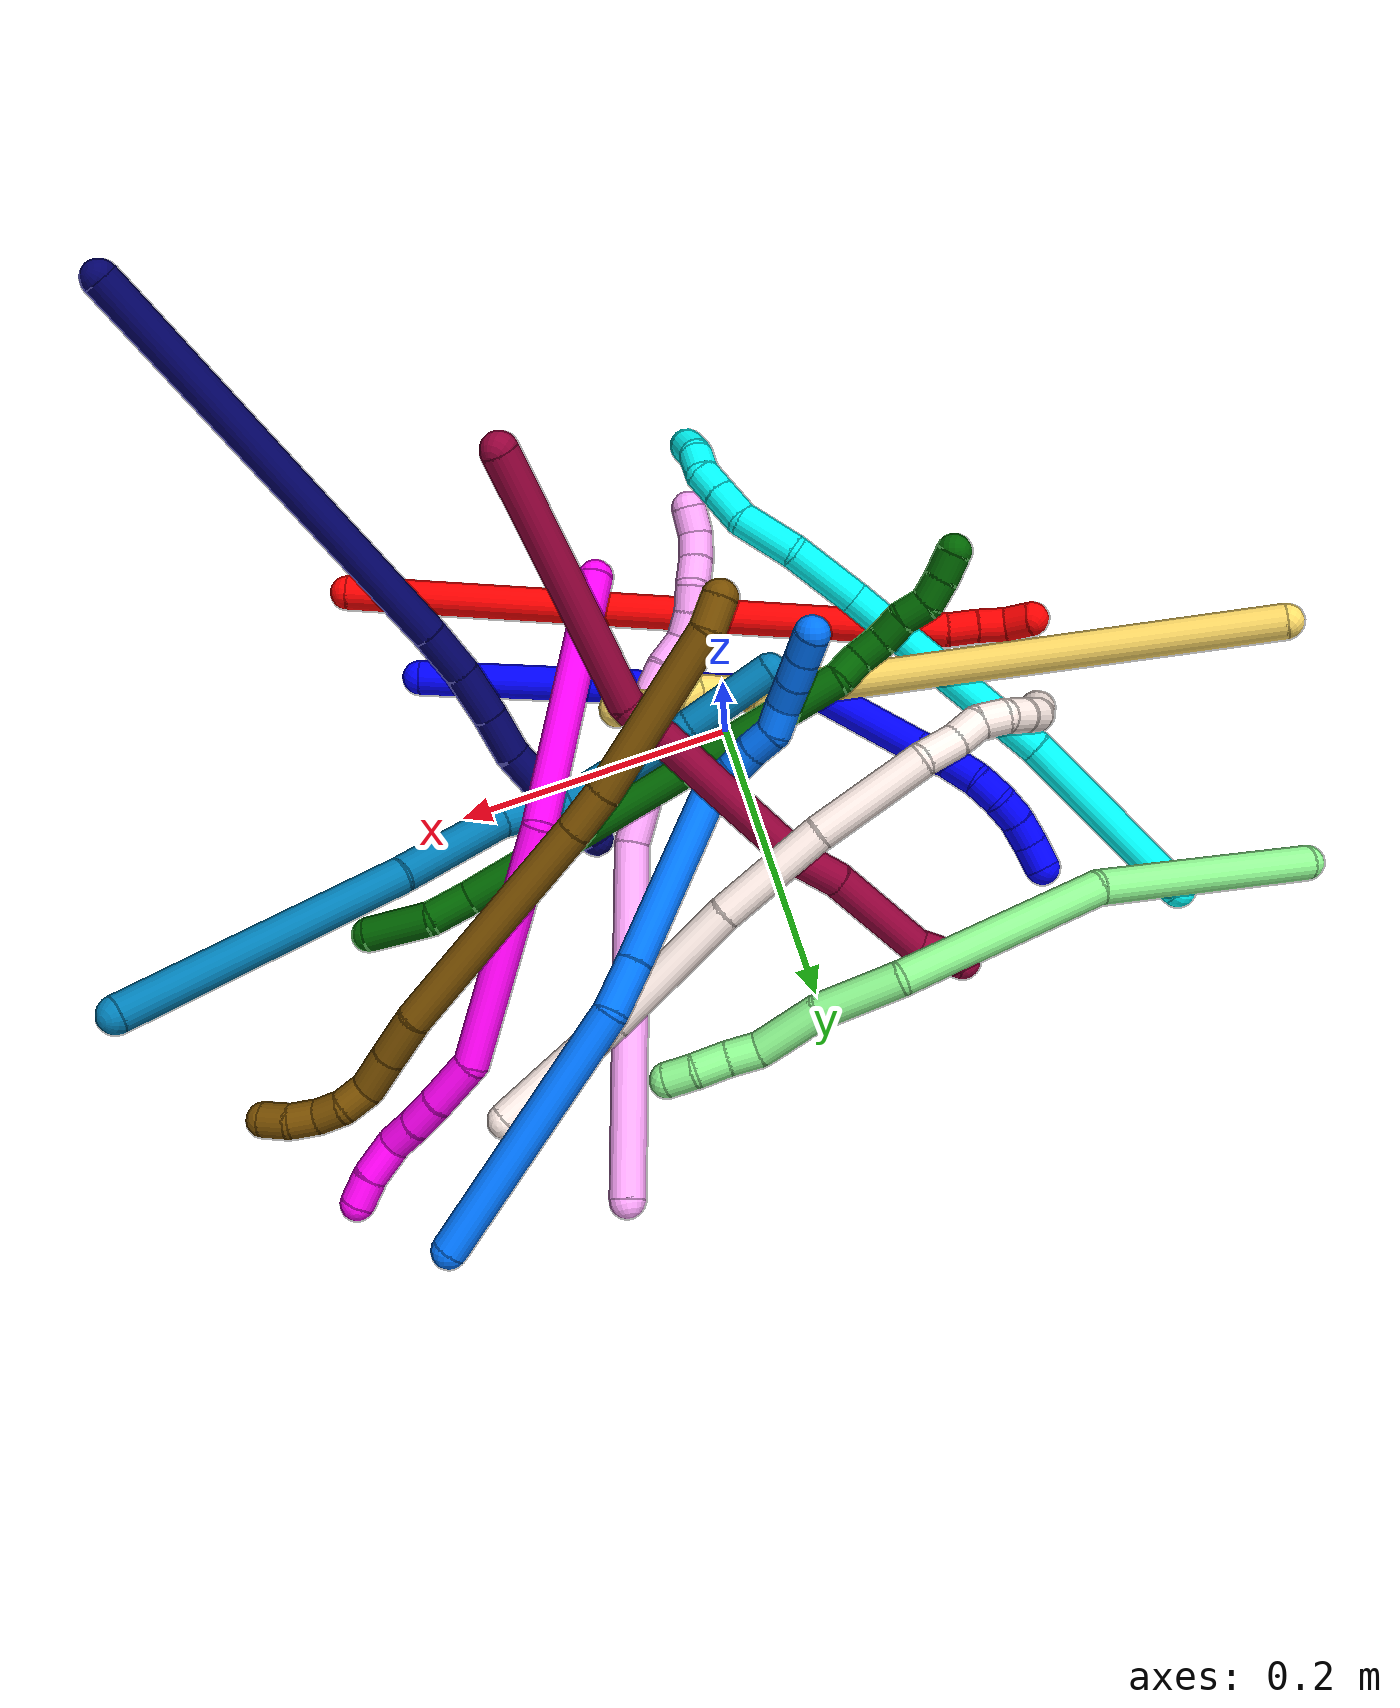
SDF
<sdf version="1.7">
 <world name="default">
  <plugin name="TubeGeneratorPlugin" filename="libtube_generator_plugin.so"/>
  <model name="photoneo_s_sensor">
   <static>1</static>
   <pose>0 0 2 1.57079 1.57079 3.14159</pose>
   <link name="link">
    <inertial><mass>0.1</mass></inertial>
    <sensor name="sensor" type="depth">
     <update_rate>30</update_rate>
     <camera>
      <horizontal_fov>1.22</horizontal_fov>
      <image><width>1920</width><height>1200</height><format>B8G8R8</format></image>
      <clip><near>0.1</near><far>4</far></clip>
      <depth_camera><output>points</output></depth_camera>
     </camera>
     <plugin name="camera_plugin" filename="libgazebo_ros_depth_camera.so">
      <baseline>0.2</baseline>
      <alwaysOn>1</alwaysOn>
      <updateRate>0.0</updateRate>
      <cameraName>camera_ir</cameraName>
      <imageTopicName>/camera/color/image_raw</imageTopicName>
      <cameraInfoTopicName>/camera/color/camera_info</cameraInfoTopicName>
      <depthImageTopicName>/camera/depth/image_raw</depthImageTopicName>
      <depthImageCameraInfoTopicName>/camera/depth/camera_info</depthImageCameraInfoTopicName>
      <pointCloudTopicName>/camera/depth/points</pointCloudTopicName>
      <frameName>fr_optical</frameName>
      <pointCloudCutoff>0.1</pointCloudCutoff>
      <pointCloudCutoffMax>2.0</pointCloudCutoffMax>
      <distortionK1>0</distortionK1>
      <distortionK2>0</distortionK2>
      <distortionK3>0</distortionK3>
      <distortionT1>0</distortionT1>
      <distortionT2>0</distortionT2>
      <CxPrime>0</CxPrime>
      <Cx>0</Cx>
      <Cy>0</Cy>
      <focalLength>0</focalLength>
      <hackBaseline>0</hackBaseline>
     </plugin>
    </sensor>
   </link>
  </model>
  <gravity>0 0 -9.8</gravity>
  <magnetic_field>6e-06 2.3e-05 -4.2e-05</magnetic_field>
  <atmosphere type="adiabatic"/>
  <physics name="default_physics" default="0" type="ode">
   <max_step_size>0.003</max_step_size>
   <real_time_factor>1</real_time_factor>
   <real_time_update_rate>1000</real_time_update_rate>
   <max_contacts>10000</max_contacts>
   <ode>
    <solver>
     <type>quick</type>
     <iters>100</iters>
     <sor>1.3</sor>
     <use_dynamic_moi_rescaling>0</use_dynamic_moi_rescaling>
    </solver>
    <constraints>
     <contact_max_correcting_vel>0</contact_max_correcting_vel>
     <contact_surface_layer>0.001</contact_surface_layer>
     <cfm>0</cfm>
     <erp>0.2</erp>
    </constraints>
   </ode>
  </physics>
  <scene><ambient>0.4 0.4 0.4 1</ambient><background>0.7 0.7 0.7 1</background><shadows>0</shadows></scene>
  <audio><device>default</device></audio>
  <spherical_coordinates>
   <surface_model>EARTH_WGS84</surface_model>
   <latitude_deg>0</latitude_deg>
   <longitude_deg>0</longitude_deg>
   <elevation>0</elevation>
   <heading_deg>0</heading_deg>
  </spherical_coordinates>
  <model name="bin">
   <static>1</static>
   <link name="bottom">
    <collision name="collision-bottom">
     <pose>0 0 -0.01 0 -0 0</pose>
     <geometry><box><size>0.8 0.6 0.02</size></box></geometry>
     <surface>
      <friction><ode><mu>100</mu><mu2>100</mu2></ode></friction>
      <contact><collide_bitmask>65535</collide_bitmask></contact>
     </surface>
    </collision>
   </link>
   <link name="west_wall">
    <collision name="collision-west_wall">
     <pose>-0.41 0 0.1 0 -0 0</pose>
     <geometry><box><size>0.02 0.6 0.2</size></box></geometry>
     <surface>
      <friction><ode><mu>100</mu><mu2>100</mu2></ode></friction>
      <contact><collide_bitmask>65535</collide_bitmask></contact>
     </surface>
    </collision>
   </link>
   <link name="east_wall">
    <collision name="collision-east_wall">
     <pose>0.41 0 0.1 0 -0 0</pose>
     <geometry><box><size>0.02 0.6 0.2</size></box></geometry>
     <surface>
      <friction><ode><mu>100</mu><mu2>100</mu2></ode></friction>
      <contact><collide_bitmask>65535</collide_bitmask></contact>
     </surface>
    </collision>
   </link>
   <link name="south_wall">
    <collision name="collision-south_wall">
     <pose>0 -0.31 0.1 0 -0 0</pose>
     <geometry><box><size>0.8 0.02 0.2</size></box></geometry>
     <surface>
      <friction><ode><mu>100</mu><mu2>100</mu2></ode></friction>
      <contact><collide_bitmask>65535</collide_bitmask></contact>
     </surface>
    </collision>
   </link>
   <link name="north_wall">
    <collision name="collision-north_wall">
     <pose>0 0.31 0.1 0 -0 0</pose>
     <geometry><box><size>0.8 0.02 0.2</size></box></geometry>
     <surface>
      <friction><ode><mu>100</mu><mu2>100</mu2></ode></friction>
      <contact><collide_bitmask>65535</collide_bitmask></contact>
     </surface>
    </collision>
   </link>
  </model>
  <model name="1">
   <static>0</static>
   <link name="1">
    <collision name="collision-cylinder-e_1_1_4">
     <pose>-0.081287 0.023662 0.118395 -0.197259 -0.592554 0.060393</pose>
     <geometry><cylinder><radius>0.0125</radius><length>0.2911</length></cylinder></geometry>
     <surface>
      <friction><ode><mu>1.16</mu><mu2>1.16</mu2><slip1>0</slip1><slip2>0</slip2></ode></friction>
      <contact><ode><kp>1e+06</kp><kd>1</kd><max_vel>0</max_vel><min_depth>0.001</min_depth></ode></contact>
     </surface>
    </collision>
    <visual name="visual-cylinder-e_1_1_4">
     <pose>-0.081287 0.023662 0.118395 -0.197259 -0.592554 0.060393</pose>
     <geometry><cylinder><radius>0.0125</radius><length>0.2911</length></cylinder></geometry>
     <material><ambient>0 0 1 1</ambient></material>
    </visual>
    <collision name="collision-cylinder-e_2_4_5">
     <pose>-0.166348 0.049323 0.276377 -0.050457 -0.094944 0.002398</pose>
     <geometry><cylinder><radius>0.0125</radius><length>0.079635</length></cylinder></geometry>
     <surface>
      <friction><ode><mu>1.16</mu><mu2>1.16</mu2><slip1>0</slip1><slip2>0</slip2></ode></friction>
      <contact><ode><kp>1e+06</kp><kd>1</kd><max_vel>0</max_vel><min_depth>0.001</min_depth></ode></contact>
     </surface>
    </collision>
    <visual name="visual-cylinder-e_2_4_5">
     <pose>-0.166348 0.049323 0.276377 -0.050457 -0.094944 0.002398</pose>
     <geometry><cylinder><radius>0.0125</radius><length>0.079635</length></cylinder></geometry>
     <material><ambient>0 0 1 1</ambient></material>
    </visual>
    <collision name="collision-cylinder-e_3_5_6">
     <pose>-0.172242 0.052486 0.327686 -0.098972 -0.177994 0.008839</pose>
     <geometry><cylinder><radius>0.0125</radius><length>0.023937</length></cylinder></geometry>
     <surface>
      <friction><ode><mu>1.16</mu><mu2>1.16</mu2><slip1>0</slip1><slip2>0</slip2></ode></friction>
      <contact><ode><kp>1e+06</kp><kd>1</kd><max_vel>0</max_vel><min_depth>0.001</min_depth></ode></contact>
     </surface>
    </collision>
    <visual name="visual-cylinder-e_3_5_6">
     <pose>-0.172242 0.052486 0.327686 -0.098972 -0.177994 0.008839</pose>
     <geometry><cylinder><radius>0.0125</radius><length>0.023937</length></cylinder></geometry>
     <material><ambient>0 0 1 1</ambient></material>
    </visual>
    <collision name="collision-cylinder-e_4_6_7">
     <pose>-0.174438 0.052934 0.351814 0.057678 -0.006146 -0.000177</pose>
     <geometry><cylinder><radius>0.0125</radius><length>0.024854</length></cylinder></geometry>
     <surface>
      <friction><ode><mu>1.16</mu><mu2>1.16</mu2><slip1>0</slip1><slip2>0</slip2></ode></friction>
      <contact><ode><kp>1e+06</kp><kd>1</kd><max_vel>0</max_vel><min_depth>0.001</min_depth></ode></contact>
     </surface>
    </collision>
    <visual name="visual-cylinder-e_4_6_7">
     <pose>-0.174438 0.052934 0.351814 0.057678 -0.006146 -0.000177</pose>
     <geometry><cylinder><radius>0.0125</radius><length>0.024854</length></cylinder></geometry>
     <material><ambient>0 0 1 1</ambient></material>
    </visual>
    <collision name="collision-cylinder-e_5_7_8">
     <pose>-0.173338 0.054342 0.37413 -0.211207 0.115551 -0.012262</pose>
     <geometry><cylinder><radius>0.0125</radius><length>0.020406</length></cylinder></geometry>
     <surface>
      <friction><ode><mu>1.16</mu><mu2>1.16</mu2><slip1>0</slip1><slip2>0</slip2></ode></friction>
      <contact><ode><kp>1e+06</kp><kd>1</kd><max_vel>0</max_vel><min_depth>0.001</min_depth></ode></contact>
     </surface>
    </collision>
    <visual name="visual-cylinder-e_5_7_8">
     <pose>-0.173338 0.054342 0.37413 -0.211207 0.115551 -0.012262</pose>
     <geometry><cylinder><radius>0.0125</radius><length>0.020406</length></cylinder></geometry>
     <material><ambient>0 0 1 1</ambient></material>
    </visual>
    <collision name="collision-cylinder-e_6_8_9">
     <pose>-0.170708 0.061879 0.392339 -0.577906 0.145696 -0.043382</pose>
     <geometry><cylinder><radius>0.0125</radius><length>0.020028</length></cylinder></geometry>
     <surface>
      <friction><ode><mu>1.16</mu><mu2>1.16</mu2><slip1>0</slip1><slip2>0</slip2></ode></friction>
      <contact><ode><kp>1e+06</kp><kd>1</kd><max_vel>0</max_vel><min_depth>0.001</min_depth></ode></contact>
     </surface>
    </collision>
    <visual name="visual-cylinder-e_6_8_9">
     <pose>-0.170708 0.061879 0.392339 -0.577906 0.145696 -0.043382</pose>
     <geometry><cylinder><radius>0.0125</radius><length>0.020028</length></cylinder></geometry>
     <material><ambient>0 0 1 1</ambient></material>
    </visual>
    <collision name="collision-cylinder-e_7_9_10">
     <pose>-0.165894 0.072308 0.408626 -0.560675 0.342161 -0.099406</pose>
     <geometry><cylinder><radius>0.0125</radius><length>0.020027</length></cylinder></geometry>
     <surface>
      <friction><ode><mu>1.16</mu><mu2>1.16</mu2><slip1>0</slip1><slip2>0</slip2></ode></friction>
      <contact><ode><kp>1e+06</kp><kd>1</kd><max_vel>0</max_vel><min_depth>0.001</min_depth></ode></contact>
     </surface>
    </collision>
    <visual name="visual-cylinder-e_7_9_10">
     <pose>-0.165894 0.072308 0.408626 -0.560675 0.342161 -0.099406</pose>
     <geometry><cylinder><radius>0.0125</radius><length>0.020027</length></cylinder></geometry>
     <material><ambient>0 0 1 1</ambient></material>
    </visual>
    <collision name="collision-cylinder-e_8_10_2">
     <pose>-0.158071 0.080128 0.425121 -0.318447 0.462318 -0.075556</pose>
     <geometry><cylinder><radius>0.0125</radius><length>0.020014</length></cylinder></geometry>
     <surface>
      <friction><ode><mu>1.16</mu><mu2>1.16</mu2><slip1>0</slip1><slip2>0</slip2></ode></friction>
      <contact><ode><kp>1e+06</kp><kd>1</kd><max_vel>0</max_vel><min_depth>0.001</min_depth></ode></contact>
     </surface>
    </collision>
    <visual name="visual-cylinder-e_8_10_2">
     <pose>-0.158071 0.080128 0.425121 -0.318447 0.462318 -0.075556</pose>
     <geometry><cylinder><radius>0.0125</radius><length>0.020014</length></cylinder></geometry>
     <material><ambient>0 0 1 1</ambient></material>
    </visual>
    <collision name="collision-sphere-2">
     <pose>-0.153608 0.082932 0.433627 0 -0 0</pose>
     <geometry><sphere><radius>0.0125</radius></sphere></geometry>
     <surface>
      <friction><ode><mu>1.16</mu><mu2>1.16</mu2><slip1>0</slip1><slip2>0</slip2></ode></friction>
      <contact><ode><kp>1e+06</kp><kd>1</kd><max_vel>0</max_vel><min_depth>0.001</min_depth></ode></contact>
     </surface>
    </collision>
    <visual name="visual-sphere-2">
     <pose>-0.153608 0.082932 0.433627 0 -0 0</pose>
     <geometry><sphere><radius>0.0125</radius></sphere></geometry>
     <material><ambient>0 0 1 1</ambient></material>
    </visual>
    <collision name="collision-sphere-10">
     <pose>-0.162534 0.077324 0.416615 0 -0 0</pose>
     <geometry><sphere><radius>0.0125</radius></sphere></geometry>
     <surface>
      <friction><ode><mu>1.16</mu><mu2>1.16</mu2><slip1>0</slip1><slip2>0</slip2></ode></friction>
      <contact><ode><kp>1e+06</kp><kd>1</kd><max_vel>0</max_vel><min_depth>0.001</min_depth></ode></contact>
     </surface>
    </collision>
    <visual name="visual-sphere-10">
     <pose>-0.162534 0.077324 0.416615 0 -0 0</pose>
     <geometry><sphere><radius>0.0125</radius></sphere></geometry>
     <material><ambient>0 0 1 1</ambient></material>
    </visual>
    <collision name="collision-sphere-9">
     <pose>-0.169254 0.067292 0.400638 0 -0 0</pose>
     <geometry><sphere><radius>0.0125</radius></sphere></geometry>
     <surface>
      <friction><ode><mu>1.16</mu><mu2>1.16</mu2><slip1>0</slip1><slip2>0</slip2></ode></friction>
      <contact><ode><kp>1e+06</kp><kd>1</kd><max_vel>0</max_vel><min_depth>0.001</min_depth></ode></contact>
     </surface>
    </collision>
    <visual name="visual-sphere-9">
     <pose>-0.169254 0.067292 0.400638 0 -0 0</pose>
     <geometry><sphere><radius>0.0125</radius></sphere></geometry>
     <material><ambient>0 0 1 1</ambient></material>
    </visual>
    <collision name="collision-sphere-4">
     <pose>-0.162574 0.047324 0.236789 0 -0 0</pose>
     <geometry><sphere><radius>0.0125</radius></sphere></geometry>
     <surface>
      <friction><ode><mu>1.16</mu><mu2>1.16</mu2><slip1>0</slip1><slip2>0</slip2></ode></friction>
      <contact><ode><kp>1e+06</kp><kd>1</kd><max_vel>0</max_vel><min_depth>0.001</min_depth></ode></contact>
     </surface>
    </collision>
    <visual name="visual-sphere-4">
     <pose>-0.162574 0.047324 0.236789 0 -0 0</pose>
     <geometry><sphere><radius>0.0125</radius></sphere></geometry>
     <material><ambient>0 0 1 1</ambient></material>
    </visual>
    <collision name="collision-sphere-1">
     <geometry><sphere><radius>0.0125</radius></sphere></geometry>
     <surface>
      <friction><ode><mu>1.16</mu><mu2>1.16</mu2><slip1>0</slip1><slip2>0</slip2></ode></friction>
      <contact><ode><kp>1e+06</kp><kd>1</kd><max_vel>0</max_vel><min_depth>0.001</min_depth></ode></contact>
     </surface>
    </collision>
    <visual name="visual-sphere-1">
     <geometry><sphere><radius>0.0125</radius></sphere></geometry>
     <material><ambient>0 0 1 1</ambient></material>
    </visual>
    <collision name="collision-sphere-8">
     <pose>-0.172161 0.056467 0.38404 0 -0 0</pose>
     <geometry><sphere><radius>0.0125</radius></sphere></geometry>
     <surface>
      <friction><ode><mu>1.16</mu><mu2>1.16</mu2><slip1>0</slip1><slip2>0</slip2></ode></friction>
      <contact><ode><kp>1e+06</kp><kd>1</kd><max_vel>0</max_vel><min_depth>0.001</min_depth></ode></contact>
     </surface>
    </collision>
    <visual name="visual-sphere-8">
     <pose>-0.172161 0.056467 0.38404 0 -0 0</pose>
     <geometry><sphere><radius>0.0125</radius></sphere></geometry>
     <material><ambient>0 0 1 1</ambient></material>
    </visual>
    <collision name="collision-sphere-5">
     <pose>-0.170123 0.051322 0.315965 0 -0 0</pose>
     <geometry><sphere><radius>0.0125</radius></sphere></geometry>
     <surface>
      <friction><ode><mu>1.16</mu><mu2>1.16</mu2><slip1>0</slip1><slip2>0</slip2></ode></friction>
      <contact><ode><kp>1e+06</kp><kd>1</kd><max_vel>0</max_vel><min_depth>0.001</min_depth></ode></contact>
     </surface>
    </collision>
    <visual name="visual-sphere-5">
     <pose>-0.170123 0.051322 0.315965 0 -0 0</pose>
     <geometry><sphere><radius>0.0125</radius></sphere></geometry>
     <material><ambient>0 0 1 1</ambient></material>
    </visual>
    <collision name="collision-sphere-6">
     <pose>-0.174361 0.05365 0.339408 0 -0 0</pose>
     <geometry><sphere><radius>0.0125</radius></sphere></geometry>
     <surface>
      <friction><ode><mu>1.16</mu><mu2>1.16</mu2><slip1>0</slip1><slip2>0</slip2></ode></friction>
      <contact><ode><kp>1e+06</kp><kd>1</kd><max_vel>0</max_vel><min_depth>0.001</min_depth></ode></contact>
     </surface>
    </collision>
    <visual name="visual-sphere-6">
     <pose>-0.174361 0.05365 0.339408 0 -0 0</pose>
     <geometry><sphere><radius>0.0125</radius></sphere></geometry>
     <material><ambient>0 0 1 1</ambient></material>
    </visual>
    <collision name="collision-sphere-7">
     <pose>-0.174514 0.052218 0.36422 0 -0 0</pose>
     <geometry><sphere><radius>0.0125</radius></sphere></geometry>
     <surface>
      <friction><ode><mu>1.16</mu><mu2>1.16</mu2><slip1>0</slip1><slip2>0</slip2></ode></friction>
      <contact><ode><kp>1e+06</kp><kd>1</kd><max_vel>0</max_vel><min_depth>0.001</min_depth></ode></contact>
     </surface>
    </collision>
    <visual name="visual-sphere-7">
     <pose>-0.174514 0.052218 0.36422 0 -0 0</pose>
     <geometry><sphere><radius>0.0125</radius></sphere></geometry>
     <material><ambient>0 0 1 1</ambient></material>
    </visual>
    <inertial>
     <pose>-0.11762 0.037576 0.210491 0 -0 0</pose>
     <mass>0.5</mass>
     <inertia>
      <ixx>0.001858</ixx>
      <ixy>0</ixy>
      <ixz>0</ixz>
      <iyy>0.002201</iyy>
      <iyz>0</iyz>
      <izz>0.000851</izz>
     </inertia>
    </inertial>
   </link>
   <pose>0.197904 -0.106471 0.012396 -1.35878 -0.027525 0.609387</pose>
  </model>
  <model name="2">
   <static>0</static>
   <link name="2">
    <collision name="collision-cylinder-e_1_1_4">
     <pose>-0.184795 0.07664 0.041832 -1.07117 -1.1294 0.719219</pose>
     <geometry><cylinder><radius>0.0125</radius><length>0.408769</length></cylinder></geometry>
     <surface>
      <friction><ode><mu>1.16</mu><mu2>1.16</mu2><slip1>0</slip1><slip2>0</slip2></ode></friction>
      <contact><ode><kp>1e+06</kp><kd>1</kd><max_vel>0</max_vel><min_depth>0.001</min_depth></ode></contact>
     </surface>
    </collision>
    <visual name="visual-cylinder-e_1_1_4">
     <pose>-0.184795 0.07664 0.041832 -1.07117 -1.1294 0.719219</pose>
     <geometry><cylinder><radius>0.0125</radius><length>0.408769</length></cylinder></geometry>
     <material><ambient>1 0 0 1</ambient></material>
    </visual>
    <collision name="collision-cylinder-e_2_4_5">
     <pose>-0.382358 0.158346 0.087035 -0.98356 -1.12602 0.652054</pose>
     <geometry><cylinder><radius>0.0125</radius><length>0.028286</length></cylinder></geometry>
     <surface>
      <friction><ode><mu>1.16</mu><mu2>1.16</mu2><slip1>0</slip1><slip2>0</slip2></ode></friction>
      <contact><ode><kp>1e+06</kp><kd>1</kd><max_vel>0</max_vel><min_depth>0.001</min_depth></ode></contact>
     </surface>
    </collision>
    <visual name="visual-cylinder-e_2_4_5">
     <pose>-0.382358 0.158346 0.087035 -0.98356 -1.12602 0.652054</pose>
     <geometry><cylinder><radius>0.0125</radius><length>0.028286</length></cylinder></geometry>
     <material><ambient>1 0 0 1</ambient></material>
    </visual>
    <collision name="collision-cylinder-e_3_5_6">
     <pose>-0.403976 0.168832 0.093913 -0.996542 -0.940668 0.539692</pose>
     <geometry><cylinder><radius>0.0125</radius><length>0.02191</length></cylinder></geometry>
     <surface>
      <friction><ode><mu>1.16</mu><mu2>1.16</mu2><slip1>0</slip1><slip2>0</slip2></ode></friction>
      <contact><ode><kp>1e+06</kp><kd>1</kd><max_vel>0</max_vel><min_depth>0.001</min_depth></ode></contact>
     </surface>
    </collision>
    <visual name="visual-cylinder-e_3_5_6">
     <pose>-0.403976 0.168832 0.093913 -0.996542 -0.940668 0.539692</pose>
     <geometry><cylinder><radius>0.0125</radius><length>0.02191</length></cylinder></geometry>
     <material><ambient>1 0 0 1</ambient></material>
    </visual>
    <collision name="collision-cylinder-e_4_6_7">
     <pose>-0.421755 0.178801 0.100513 -0.973558 -1.01849 0.574684</pose>
     <geometry><cylinder><radius>0.0125</radius><length>0.020974</length></cylinder></geometry>
     <surface>
      <friction><ode><mu>1.16</mu><mu2>1.16</mu2><slip1>0</slip1><slip2>0</slip2></ode></friction>
      <contact><ode><kp>1e+06</kp><kd>1</kd><max_vel>0</max_vel><min_depth>0.001</min_depth></ode></contact>
     </surface>
    </collision>
    <visual name="visual-cylinder-e_4_6_7">
     <pose>-0.421755 0.178801 0.100513 -0.973558 -1.01849 0.574684</pose>
     <geometry><cylinder><radius>0.0125</radius><length>0.020974</length></cylinder></geometry>
     <material><ambient>1 0 0 1</ambient></material>
    </visual>
    <collision name="collision-cylinder-e_5_7_2">
     <pose>-0.436879 0.191234 0.103897 -1.53405 -0.665856 0.643479</pose>
     <geometry><cylinder><radius>0.0125</radius><length>0.020062</length></cylinder></geometry>
     <surface>
      <friction><ode><mu>1.16</mu><mu2>1.16</mu2><slip1>0</slip1><slip2>0</slip2></ode></friction>
      <contact><ode><kp>1e+06</kp><kd>1</kd><max_vel>0</max_vel><min_depth>0.001</min_depth></ode></contact>
     </surface>
    </collision>
    <visual name="visual-cylinder-e_5_7_2">
     <pose>-0.436879 0.191234 0.103897 -1.53405 -0.665856 0.643479</pose>
     <geometry><cylinder><radius>0.0125</radius><length>0.020062</length></cylinder></geometry>
     <material><ambient>1 0 0 1</ambient></material>
    </visual>
    <collision name="collision-sphere-2">
     <pose>-0.443075 0.199116 0.104187 0 -0 0</pose>
     <geometry><sphere><radius>0.0125</radius></sphere></geometry>
     <surface>
      <friction><ode><mu>1.16</mu><mu2>1.16</mu2><slip1>0</slip1><slip2>0</slip2></ode></friction>
      <contact><ode><kp>1e+06</kp><kd>1</kd><max_vel>0</max_vel><min_depth>0.001</min_depth></ode></contact>
     </surface>
    </collision>
    <visual name="visual-sphere-2">
     <pose>-0.443075 0.199116 0.104187 0 -0 0</pose>
     <geometry><sphere><radius>0.0125</radius></sphere></geometry>
     <material><ambient>1 0 0 1</ambient></material>
    </visual>
    <collision name="collision-sphere-7">
     <pose>-0.430682 0.183351 0.103607 0 -0 0</pose>
     <geometry><sphere><radius>0.0125</radius></sphere></geometry>
     <surface>
      <friction><ode><mu>1.16</mu><mu2>1.16</mu2><slip1>0</slip1><slip2>0</slip2></ode></friction>
      <contact><ode><kp>1e+06</kp><kd>1</kd><max_vel>0</max_vel><min_depth>0.001</min_depth></ode></contact>
     </surface>
    </collision>
    <visual name="visual-sphere-7">
     <pose>-0.430682 0.183351 0.103607 0 -0 0</pose>
     <geometry><sphere><radius>0.0125</radius></sphere></geometry>
     <material><ambient>1 0 0 1</ambient></material>
    </visual>
    <collision name="collision-sphere-6">
     <pose>-0.412827 0.174252 0.097419 0 -0 0</pose>
     <geometry><sphere><radius>0.0125</radius></sphere></geometry>
     <surface>
      <friction><ode><mu>1.16</mu><mu2>1.16</mu2><slip1>0</slip1><slip2>0</slip2></ode></friction>
      <contact><ode><kp>1e+06</kp><kd>1</kd><max_vel>0</max_vel><min_depth>0.001</min_depth></ode></contact>
     </surface>
    </collision>
    <visual name="visual-sphere-6">
     <pose>-0.412827 0.174252 0.097419 0 -0 0</pose>
     <geometry><sphere><radius>0.0125</radius></sphere></geometry>
     <material><ambient>1 0 0 1</ambient></material>
    </visual>
    <collision name="collision-sphere-5">
     <pose>-0.395125 0.163412 0.090406 0 -0 0</pose>
     <geometry><sphere><radius>0.0125</radius></sphere></geometry>
     <surface>
      <friction><ode><mu>1.16</mu><mu2>1.16</mu2><slip1>0</slip1><slip2>0</slip2></ode></friction>
      <contact><ode><kp>1e+06</kp><kd>1</kd><max_vel>0</max_vel><min_depth>0.001</min_depth></ode></contact>
     </surface>
    </collision>
    <visual name="visual-sphere-5">
     <pose>-0.395125 0.163412 0.090406 0 -0 0</pose>
     <geometry><sphere><radius>0.0125</radius></sphere></geometry>
     <material><ambient>1 0 0 1</ambient></material>
    </visual>
    <collision name="collision-sphere-1">
     <geometry><sphere><radius>0.0125</radius></sphere></geometry>
     <surface>
      <friction><ode><mu>1.16</mu><mu2>1.16</mu2><slip1>0</slip1><slip2>0</slip2></ode></friction>
      <contact><ode><kp>1e+06</kp><kd>1</kd><max_vel>0</max_vel><min_depth>0.001</min_depth></ode></contact>
     </surface>
    </collision>
    <visual name="visual-sphere-1">
     <geometry><sphere><radius>0.0125</radius></sphere></geometry>
     <material><ambient>1 0 0 1</ambient></material>
    </visual>
    <collision name="collision-sphere-4">
     <pose>-0.369591 0.153281 0.083663 0 -0 0</pose>
     <geometry><sphere><radius>0.0125</radius></sphere></geometry>
     <surface>
      <friction><ode><mu>1.16</mu><mu2>1.16</mu2><slip1>0</slip1><slip2>0</slip2></ode></friction>
      <contact><ode><kp>1e+06</kp><kd>1</kd><max_vel>0</max_vel><min_depth>0.001</min_depth></ode></contact>
     </surface>
    </collision>
    <visual name="visual-sphere-4">
     <pose>-0.369591 0.153281 0.083663 0 -0 0</pose>
     <geometry><sphere><radius>0.0125</radius></sphere></geometry>
     <material><ambient>1 0 0 1</ambient></material>
    </visual>
    <inertial>
     <pose>-0.225631 0.094186 0.051623 0 -0 0</pose>
     <mass>0.5</mass>
     <inertia>
      <ixx>0.003412</ixx>
      <ixy>0</ixy>
      <ixz>0</ixz>
      <iyy>0.006672</iyy>
      <iyz>0</iyz>
      <izz>0.003031</izz>
     </inertia>
    </inertial>
   </link>
   <pose>0.2292 -0.183602 0.011498 2.18178 -0.202121 -0.783777</pose>
  </model>
  <model name="3">
   <static>0</static>
   <link name="3">
    <collision name="collision-cylinder-e_1_1_4">
     <pose>0.029293 -0.052501 -0.03943 2.21495 0.419638 0.805866</pose>
     <geometry><cylinder><radius>0.0125</radius><length>0.143794</length></cylinder></geometry>
     <surface>
      <friction><ode><mu>1.16</mu><mu2>1.16</mu2><slip1>0</slip1><slip2>0</slip2></ode></friction>
      <contact><ode><kp>1e+06</kp><kd>1</kd><max_vel>0</max_vel><min_depth>0.001</min_depth></ode></contact>
     </surface>
    </collision>
    <visual name="visual-cylinder-e_1_1_4">
     <pose>0.029293 -0.052501 -0.03943 2.21495 0.419638 0.805866</pose>
     <geometry><cylinder><radius>0.0125</radius><length>0.143794</length></cylinder></geometry>
     <material><ambient>0.003922 1 0.996078 1</ambient></material>
    </visual>
    <collision name="collision-cylinder-e_2_4_5">
     <pose>0.084116 -0.169724 -0.125956 2.19986 0.308747 0.59333</pose>
     <geometry><cylinder><radius>0.0125</radius><length>0.168033</length></cylinder></geometry>
     <surface>
      <friction><ode><mu>1.16</mu><mu2>1.16</mu2><slip1>0</slip1><slip2>0</slip2></ode></friction>
      <contact><ode><kp>1e+06</kp><kd>1</kd><max_vel>0</max_vel><min_depth>0.001</min_depth></ode></contact>
     </surface>
    </collision>
    <visual name="visual-cylinder-e_2_4_5">
     <pose>0.084116 -0.169724 -0.125956 2.19986 0.308747 0.59333</pose>
     <geometry><cylinder><radius>0.0125</radius><length>0.168033</length></cylinder></geometry>
     <material><ambient>0.003922 1 0.996078 1</ambient></material>
    </visual>
    <collision name="collision-cylinder-e_3_5_6">
     <pose>0.119012 -0.250527 -0.193002 2.46314 0.350461 0.930069</pose>
     <geometry><cylinder><radius>0.0125</radius><length>0.054565</length></cylinder></geometry>
     <surface>
      <friction><ode><mu>1.16</mu><mu2>1.16</mu2><slip1>0</slip1><slip2>0</slip2></ode></friction>
      <contact><ode><kp>1e+06</kp><kd>1</kd><max_vel>0</max_vel><min_depth>0.001</min_depth></ode></contact>
     </surface>
    </collision>
    <visual name="visual-cylinder-e_3_5_6">
     <pose>0.119012 -0.250527 -0.193002 2.46314 0.350461 0.930069</pose>
     <geometry><cylinder><radius>0.0125</radius><length>0.054565</length></cylinder></geometry>
     <material><ambient>0.003922 1 0.996078 1</ambient></material>
    </visual>
    <collision name="collision-cylinder-e_4_6_7">
     <pose>0.131897 -0.284765 -0.225082 2.1598 0.159736 0.297257</pose>
     <geometry><cylinder><radius>0.0125</radius><length>0.044234</length></cylinder></geometry>
     <surface>
      <friction><ode><mu>1.16</mu><mu2>1.16</mu2><slip1>0</slip1><slip2>0</slip2></ode></friction>
      <contact><ode><kp>1e+06</kp><kd>1</kd><max_vel>0</max_vel><min_depth>0.001</min_depth></ode></contact>
     </surface>
    </collision>
    <visual name="visual-cylinder-e_4_6_7">
     <pose>0.131897 -0.284765 -0.225082 2.1598 0.159736 0.297257</pose>
     <geometry><cylinder><radius>0.0125</radius><length>0.044234</length></cylinder></geometry>
     <material><ambient>0.003922 1 0.996078 1</ambient></material>
    </visual>
    <collision name="collision-cylinder-e_5_7_8">
     <pose>0.139739 -0.314891 -0.24067 1.85205 0.334028 0.441077</pose>
     <geometry><cylinder><radius>0.0125</radius><length>0.026378</length></cylinder></geometry>
     <surface>
      <friction><ode><mu>1.16</mu><mu2>1.16</mu2><slip1>0</slip1><slip2>0</slip2></ode></friction>
      <contact><ode><kp>1e+06</kp><kd>1</kd><max_vel>0</max_vel><min_depth>0.001</min_depth></ode></contact>
     </surface>
    </collision>
    <visual name="visual-cylinder-e_5_7_8">
     <pose>0.139739 -0.314891 -0.24067 1.85205 0.334028 0.441077</pose>
     <geometry><cylinder><radius>0.0125</radius><length>0.026378</length></cylinder></geometry>
     <material><ambient>0.003922 1 0.996078 1</ambient></material>
    </visual>
    <collision name="collision-cylinder-e_6_8_9">
     <pose>0.147428 -0.336113 -0.246798 1.85176 0.336269 0.443868</pose>
     <geometry><cylinder><radius>0.0125</radius><length>0.0204</length></cylinder></geometry>
     <surface>
      <friction><ode><mu>1.16</mu><mu2>1.16</mu2><slip1>0</slip1><slip2>0</slip2></ode></friction>
      <contact><ode><kp>1e+06</kp><kd>1</kd><max_vel>0</max_vel><min_depth>0.001</min_depth></ode></contact>
     </surface>
    </collision>
    <visual name="visual-cylinder-e_6_8_9">
     <pose>0.147428 -0.336113 -0.246798 1.85176 0.336269 0.443868</pose>
     <geometry><cylinder><radius>0.0125</radius><length>0.0204</length></cylinder></geometry>
     <material><ambient>0.003922 1 0.996078 1</ambient></material>
    </visual>
    <collision name="collision-cylinder-e_7_9_10">
     <pose>0.154352 -0.354648 -0.247384 1.34998 0.357817 0.287499</pose>
     <geometry><cylinder><radius>0.0125</radius><length>0.020318</length></cylinder></geometry>
     <surface>
      <friction><ode><mu>1.16</mu><mu2>1.16</mu2><slip1>0</slip1><slip2>0</slip2></ode></friction>
      <contact><ode><kp>1e+06</kp><kd>1</kd><max_vel>0</max_vel><min_depth>0.001</min_depth></ode></contact>
     </surface>
    </collision>
    <visual name="visual-cylinder-e_7_9_10">
     <pose>0.154352 -0.354648 -0.247384 1.34998 0.357817 0.287499</pose>
     <geometry><cylinder><radius>0.0125</radius><length>0.020318</length></cylinder></geometry>
     <material><ambient>0.003922 1 0.996078 1</ambient></material>
    </visual>
    <collision name="collision-cylinder-e_8_10_2">
     <pose>0.157429 -0.374529 -0.241897 1.26001 -0.04319 -0.031493</pose>
     <geometry><cylinder><radius>0.0125</radius><length>0.022279</length></cylinder></geometry>
     <surface>
      <friction><ode><mu>1.16</mu><mu2>1.16</mu2><slip1>0</slip1><slip2>0</slip2></ode></friction>
      <contact><ode><kp>1e+06</kp><kd>1</kd><max_vel>0</max_vel><min_depth>0.001</min_depth></ode></contact>
     </surface>
    </collision>
    <visual name="visual-cylinder-e_8_10_2">
     <pose>0.157429 -0.374529 -0.241897 1.26001 -0.04319 -0.031493</pose>
     <geometry><cylinder><radius>0.0125</radius><length>0.022279</length></cylinder></geometry>
     <material><ambient>0.003922 1 0.996078 1</ambient></material>
    </visual>
    <collision name="collision-sphere-2">
     <pose>0.156948 -0.385125 -0.238493 0 -0 0</pose>
     <geometry><sphere><radius>0.0125</radius></sphere></geometry>
     <surface>
      <friction><ode><mu>1.16</mu><mu2>1.16</mu2><slip1>0</slip1><slip2>0</slip2></ode></friction>
      <contact><ode><kp>1e+06</kp><kd>1</kd><max_vel>0</max_vel><min_depth>0.001</min_depth></ode></contact>
     </surface>
    </collision>
    <visual name="visual-sphere-2">
     <pose>0.156948 -0.385125 -0.238493 0 -0 0</pose>
     <geometry><sphere><radius>0.0125</radius></sphere></geometry>
     <material><ambient>0.003922 1 0.996078 1</ambient></material>
    </visual>
    <collision name="collision-sphere-10">
     <pose>0.15791 -0.363933 -0.2453 0 -0 0</pose>
     <geometry><sphere><radius>0.0125</radius></sphere></geometry>
     <surface>
      <friction><ode><mu>1.16</mu><mu2>1.16</mu2><slip1>0</slip1><slip2>0</slip2></ode></friction>
      <contact><ode><kp>1e+06</kp><kd>1</kd><max_vel>0</max_vel><min_depth>0.001</min_depth></ode></contact>
     </surface>
    </collision>
    <visual name="visual-sphere-10">
     <pose>0.15791 -0.363933 -0.2453 0 -0 0</pose>
     <geometry><sphere><radius>0.0125</radius></sphere></geometry>
     <material><ambient>0.003922 1 0.996078 1</ambient></material>
    </visual>
    <collision name="collision-sphere-9">
     <pose>0.150794 -0.345364 -0.249468 0 -0 0</pose>
     <geometry><sphere><radius>0.0125</radius></sphere></geometry>
     <surface>
      <friction><ode><mu>1.16</mu><mu2>1.16</mu2><slip1>0</slip1><slip2>0</slip2></ode></friction>
      <contact><ode><kp>1e+06</kp><kd>1</kd><max_vel>0</max_vel><min_depth>0.001</min_depth></ode></contact>
     </surface>
    </collision>
    <visual name="visual-sphere-9">
     <pose>0.150794 -0.345364 -0.249468 0 -0 0</pose>
     <geometry><sphere><radius>0.0125</radius></sphere></geometry>
     <material><ambient>0.003922 1 0.996078 1</ambient></material>
    </visual>
    <collision name="collision-sphere-4">
     <pose>0.058586 -0.105003 -0.078859 0 -0 0</pose>
     <geometry><sphere><radius>0.0125</radius></sphere></geometry>
     <surface>
      <friction><ode><mu>1.16</mu><mu2>1.16</mu2><slip1>0</slip1><slip2>0</slip2></ode></friction>
      <contact><ode><kp>1e+06</kp><kd>1</kd><max_vel>0</max_vel><min_depth>0.001</min_depth></ode></contact>
     </surface>
    </collision>
    <visual name="visual-sphere-4">
     <pose>0.058586 -0.105003 -0.078859 0 -0 0</pose>
     <geometry><sphere><radius>0.0125</radius></sphere></geometry>
     <material><ambient>0.003922 1 0.996078 1</ambient></material>
    </visual>
    <collision name="collision-sphere-1">
     <geometry><sphere><radius>0.0125</radius></sphere></geometry>
     <surface>
      <friction><ode><mu>1.16</mu><mu2>1.16</mu2><slip1>0</slip1><slip2>0</slip2></ode></friction>
      <contact><ode><kp>1e+06</kp><kd>1</kd><max_vel>0</max_vel><min_depth>0.001</min_depth></ode></contact>
     </surface>
    </collision>
    <visual name="visual-sphere-1">
     <geometry><sphere><radius>0.0125</radius></sphere></geometry>
     <material><ambient>0.003922 1 0.996078 1</ambient></material>
    </visual>
    <collision name="collision-sphere-8">
     <pose>0.144063 -0.326862 -0.244129 0 -0 0</pose>
     <geometry><sphere><radius>0.0125</radius></sphere></geometry>
     <surface>
      <friction><ode><mu>1.16</mu><mu2>1.16</mu2><slip1>0</slip1><slip2>0</slip2></ode></friction>
      <contact><ode><kp>1e+06</kp><kd>1</kd><max_vel>0</max_vel><min_depth>0.001</min_depth></ode></contact>
     </surface>
    </collision>
    <visual name="visual-sphere-8">
     <pose>0.144063 -0.326862 -0.244129 0 -0 0</pose>
     <geometry><sphere><radius>0.0125</radius></sphere></geometry>
     <material><ambient>0.003922 1 0.996078 1</ambient></material>
    </visual>
    <collision name="collision-sphere-5">
     <pose>0.109645 -0.234446 -0.173053 0 -0 0</pose>
     <geometry><sphere><radius>0.0125</radius></sphere></geometry>
     <surface>
      <friction><ode><mu>1.16</mu><mu2>1.16</mu2><slip1>0</slip1><slip2>0</slip2></ode></friction>
      <contact><ode><kp>1e+06</kp><kd>1</kd><max_vel>0</max_vel><min_depth>0.001</min_depth></ode></contact>
     </surface>
    </collision>
    <visual name="visual-sphere-5">
     <pose>0.109645 -0.234446 -0.173053 0 -0 0</pose>
     <geometry><sphere><radius>0.0125</radius></sphere></geometry>
     <material><ambient>0.003922 1 0.996078 1</ambient></material>
    </visual>
    <collision name="collision-sphere-6">
     <pose>0.128379 -0.266609 -0.212951 0 -0 0</pose>
     <geometry><sphere><radius>0.0125</radius></sphere></geometry>
     <surface>
      <friction><ode><mu>1.16</mu><mu2>1.16</mu2><slip1>0</slip1><slip2>0</slip2></ode></friction>
      <contact><ode><kp>1e+06</kp><kd>1</kd><max_vel>0</max_vel><min_depth>0.001</min_depth></ode></contact>
     </surface>
    </collision>
    <visual name="visual-sphere-6">
     <pose>0.128379 -0.266609 -0.212951 0 -0 0</pose>
     <geometry><sphere><radius>0.0125</radius></sphere></geometry>
     <material><ambient>0.003922 1 0.996078 1</ambient></material>
    </visual>
    <collision name="collision-sphere-7">
     <pose>0.135415 -0.302921 -0.237212 0 -0 0</pose>
     <geometry><sphere><radius>0.0125</radius></sphere></geometry>
     <surface>
      <friction><ode><mu>1.16</mu><mu2>1.16</mu2><slip1>0</slip1><slip2>0</slip2></ode></friction>
      <contact><ode><kp>1e+06</kp><kd>1</kd><max_vel>0</max_vel><min_depth>0.001</min_depth></ode></contact>
     </surface>
    </collision>
    <visual name="visual-sphere-7">
     <pose>0.135415 -0.302921 -0.237212 0 -0 0</pose>
     <geometry><sphere><radius>0.0125</radius></sphere></geometry>
     <material><ambient>0.003922 1 0.996078 1</ambient></material>
    </visual>
    <inertial>
     <pose>0.088023 -0.186095 -0.138241 0 -0 0</pose>
     <mass>0.5</mass>
     <inertia>
      <ixx>0.000911</ixx>
      <ixy>0</ixy>
      <ixz>0</ixz>
      <iyy>0.000172</iyy>
      <iyz>0</iyz>
      <izz>0.000265</izz>
     </inertia>
    </inertial>
   </link>
   <pose>-0.268062 0.213175 0.011609 2.39024 -0.535032 -2.25979</pose>
  </model>
  <model name="4">
   <static>0</static>
   <link name="4">
    <collision name="collision-cylinder-e_1_1_4">
     <pose>-0.011661 -0.017821 -0.121189 2.99559 -0.094911 -1.15187</pose>
     <geometry><cylinder><radius>0.0125</radius><length>0.246092</length></cylinder></geometry>
     <surface>
      <friction><ode><mu>1.16</mu><mu2>1.16</mu2><slip1>0</slip1><slip2>0</slip2></ode></friction>
      <contact><ode><kp>1e+06</kp><kd>1</kd><max_vel>0</max_vel><min_depth>0.001</min_depth></ode></contact>
     </surface>
    </collision>
    <visual name="visual-cylinder-e_1_1_4">
     <pose>-0.011661 -0.017821 -0.121189 2.99559 -0.094911 -1.15187</pose>
     <geometry><cylinder><radius>0.0125</radius><length>0.246092</length></cylinder></geometry>
     <material><ambient>1 0.65098 0.996078 1</ambient></material>
    </visual>
    <collision name="collision-cylinder-e_2_4_5">
     <pose>-0.024443 -0.04676 -0.261564 2.61641 -0.050507 -0.187391</pose>
     <geometry><cylinder><radius>0.0125</radius><length>0.044406</length></cylinder></geometry>
     <surface>
      <friction><ode><mu>1.16</mu><mu2>1.16</mu2><slip1>0</slip1><slip2>0</slip2></ode></friction>
      <contact><ode><kp>1e+06</kp><kd>1</kd><max_vel>0</max_vel><min_depth>0.001</min_depth></ode></contact>
     </surface>
    </collision>
    <visual name="visual-cylinder-e_2_4_5">
     <pose>-0.024443 -0.04676 -0.261564 2.61641 -0.050507 -0.187391</pose>
     <geometry><cylinder><radius>0.0125</radius><length>0.044406</length></cylinder></geometry>
     <material><ambient>1 0.65098 0.996078 1</ambient></material>
    </visual>
    <collision name="collision-cylinder-e_3_5_6">
     <pose>-0.022263 -0.066869 -0.309384 2.83734 0.109538 0.68685</pose>
     <geometry><cylinder><radius>0.0125</radius><length>0.060387</length></cylinder></geometry>
     <surface>
      <friction><ode><mu>1.16</mu><mu2>1.16</mu2><slip1>0</slip1><slip2>0</slip2></ode></friction>
      <contact><ode><kp>1e+06</kp><kd>1</kd><max_vel>0</max_vel><min_depth>0.001</min_depth></ode></contact>
     </surface>
    </collision>
    <visual name="visual-cylinder-e_3_5_6">
     <pose>-0.022263 -0.066869 -0.309384 2.83734 0.109538 0.68685</pose>
     <geometry><cylinder><radius>0.0125</radius><length>0.060387</length></cylinder></geometry>
     <material><ambient>1 0.65098 0.996078 1</ambient></material>
    </visual>
    <collision name="collision-cylinder-e_4_6_7">
     <pose>-0.021193 -0.082836 -0.347954 2.52954 -0.181739 -0.56156</pose>
     <geometry><cylinder><radius>0.0125</radius><length>0.024687</length></cylinder></geometry>
     <surface>
      <friction><ode><mu>1.16</mu><mu2>1.16</mu2><slip1>0</slip1><slip2>0</slip2></ode></friction>
      <contact><ode><kp>1e+06</kp><kd>1</kd><max_vel>0</max_vel><min_depth>0.001</min_depth></ode></contact>
     </surface>
    </collision>
    <visual name="visual-cylinder-e_4_6_7">
     <pose>-0.021193 -0.082836 -0.347954 2.52954 -0.181739 -0.56156</pose>
     <geometry><cylinder><radius>0.0125</radius><length>0.024687</length></cylinder></geometry>
     <material><ambient>1 0.65098 0.996078 1</ambient></material>
    </visual>
    <collision name="collision-cylinder-e_5_7_8">
     <pose>-0.027912 -0.097386 -0.366355 2.41157 -0.37627 -0.924443</pose>
     <geometry><cylinder><radius>0.0125</radius><length>0.024427</length></cylinder></geometry>
     <surface>
      <friction><ode><mu>1.16</mu><mu2>1.16</mu2><slip1>0</slip1><slip2>0</slip2></ode></friction>
      <contact><ode><kp>1e+06</kp><kd>1</kd><max_vel>0</max_vel><min_depth>0.001</min_depth></ode></contact>
     </surface>
    </collision>
    <visual name="visual-cylinder-e_5_7_8">
     <pose>-0.027912 -0.097386 -0.366355 2.41157 -0.37627 -0.924443</pose>
     <geometry><cylinder><radius>0.0125</radius><length>0.024427</length></cylinder></geometry>
     <material><ambient>1 0.65098 0.996078 1</ambient></material>
    </visual>
    <collision name="collision-cylinder-e_6_8_9">
     <pose>-0.032231 -0.110406 -0.383206 2.56575 0.016931 0.057156</pose>
     <geometry><cylinder><radius>0.0125</radius><length>0.020001</length></cylinder></geometry>
     <surface>
      <friction><ode><mu>1.16</mu><mu2>1.16</mu2><slip1>0</slip1><slip2>0</slip2></ode></friction>
      <contact><ode><kp>1e+06</kp><kd>1</kd><max_vel>0</max_vel><min_depth>0.001</min_depth></ode></contact>
     </surface>
    </collision>
    <visual name="visual-cylinder-e_6_8_9">
     <pose>-0.032231 -0.110406 -0.383206 2.56575 0.016931 0.057156</pose>
     <geometry><cylinder><radius>0.0125</radius><length>0.020001</length></cylinder></geometry>
     <material><ambient>1 0.65098 0.996078 1</ambient></material>
    </visual>
    <collision name="collision-cylinder-e_7_9_10">
     <pose>-0.03045 -0.119923 -0.400583 2.71627 0.161839 0.718546</pose>
     <geometry><cylinder><radius>0.0125</radius><length>0.020001</length></cylinder></geometry>
     <surface>
      <friction><ode><mu>1.16</mu><mu2>1.16</mu2><slip1>0</slip1><slip2>0</slip2></ode></friction>
      <contact><ode><kp>1e+06</kp><kd>1</kd><max_vel>0</max_vel><min_depth>0.001</min_depth></ode></contact>
     </surface>
    </collision>
    <visual name="visual-cylinder-e_7_9_10">
     <pose>-0.03045 -0.119923 -0.400583 2.71627 0.161839 0.718546</pose>
     <geometry><cylinder><radius>0.0125</radius><length>0.020001</length></cylinder></geometry>
     <material><ambient>1 0.65098 0.996078 1</ambient></material>
    </visual>
    <collision name="collision-cylinder-e_8_10_11">
     <pose>-0.031013 -0.12581 -0.419164 2.95464 -0.219201 -1.73034</pose>
     <geometry><cylinder><radius>0.0125</radius><length>0.02</length></cylinder></geometry>
     <surface>
      <friction><ode><mu>1.16</mu><mu2>1.16</mu2><slip1>0</slip1><slip2>0</slip2></ode></friction>
      <contact><ode><kp>1e+06</kp><kd>1</kd><max_vel>0</max_vel><min_depth>0.001</min_depth></ode></contact>
     </surface>
    </collision>
    <visual name="visual-cylinder-e_8_10_11">
     <pose>-0.031013 -0.12581 -0.419164 2.95464 -0.219201 -1.73034</pose>
     <geometry><cylinder><radius>0.0125</radius><length>0.02</length></cylinder></geometry>
     <material><ambient>1 0.65098 0.996078 1</ambient></material>
    </visual>
    <collision name="collision-cylinder-e_9_11_12">
     <pose>-0.033527 -0.129374 -0.438594 2.9656 -0.033984 -0.380571</pose>
     <geometry><cylinder><radius>0.0125</radius><length>0.02</length></cylinder></geometry>
     <surface>
      <friction><ode><mu>1.16</mu><mu2>1.16</mu2><slip1>0</slip1><slip2>0</slip2></ode></friction>
      <contact><ode><kp>1e+06</kp><kd>1</kd><max_vel>0</max_vel><min_depth>0.001</min_depth></ode></contact>
     </surface>
    </collision>
    <visual name="visual-cylinder-e_9_11_12">
     <pose>-0.033527 -0.129374 -0.438594 2.9656 -0.033984 -0.380571</pose>
     <geometry><cylinder><radius>0.0125</radius><length>0.02</length></cylinder></geometry>
     <material><ambient>1 0.65098 0.996078 1</ambient></material>
    </visual>
    <collision name="collision-cylinder-e_10_12_2">
     <pose>-0.030937 -0.132455 -0.457902 3.0019 0.297339 2.26765</pose>
     <geometry><cylinder><radius>0.0125</radius><length>0.02</length></cylinder></geometry>
     <surface>
      <friction><ode><mu>1.16</mu><mu2>1.16</mu2><slip1>0</slip1><slip2>0</slip2></ode></friction>
      <contact><ode><kp>1e+06</kp><kd>1</kd><max_vel>0</max_vel><min_depth>0.001</min_depth></ode></contact>
     </surface>
    </collision>
    <visual name="visual-cylinder-e_10_12_2">
     <pose>-0.030937 -0.132455 -0.457902 3.0019 0.297339 2.26765</pose>
     <geometry><cylinder><radius>0.0125</radius><length>0.02</length></cylinder></geometry>
     <material><ambient>1 0.65098 0.996078 1</ambient></material>
    </visual>
    <collision name="collision-sphere-2">
     <pose>-0.028008 -0.133786 -0.46737 0 -0 0</pose>
     <geometry><sphere><radius>0.0125</radius></sphere></geometry>
     <surface>
      <friction><ode><mu>1.16</mu><mu2>1.16</mu2><slip1>0</slip1><slip2>0</slip2></ode></friction>
      <contact><ode><kp>1e+06</kp><kd>1</kd><max_vel>0</max_vel><min_depth>0.001</min_depth></ode></contact>
     </surface>
    </collision>
    <visual name="visual-sphere-2">
     <pose>-0.028008 -0.133786 -0.46737 0 -0 0</pose>
     <geometry><sphere><radius>0.0125</radius></sphere></geometry>
     <material><ambient>1 0.65098 0.996078 1</ambient></material>
    </visual>
    <collision name="collision-sphere-12">
     <pose>-0.033867 -0.131124 -0.448434 0 -0 0</pose>
     <geometry><sphere><radius>0.0125</radius></sphere></geometry>
     <surface>
      <friction><ode><mu>1.16</mu><mu2>1.16</mu2><slip1>0</slip1><slip2>0</slip2></ode></friction>
      <contact><ode><kp>1e+06</kp><kd>1</kd><max_vel>0</max_vel><min_depth>0.001</min_depth></ode></contact>
     </surface>
    </collision>
    <visual name="visual-sphere-12">
     <pose>-0.033867 -0.131124 -0.448434 0 -0 0</pose>
     <geometry><sphere><radius>0.0125</radius></sphere></geometry>
     <material><ambient>1 0.65098 0.996078 1</ambient></material>
    </visual>
    <collision name="collision-sphere-11">
     <pose>-0.033188 -0.127624 -0.428754 0 -0 0</pose>
     <geometry><sphere><radius>0.0125</radius></sphere></geometry>
     <surface>
      <friction><ode><mu>1.16</mu><mu2>1.16</mu2><slip1>0</slip1><slip2>0</slip2></ode></friction>
      <contact><ode><kp>1e+06</kp><kd>1</kd><max_vel>0</max_vel><min_depth>0.001</min_depth></ode></contact>
     </surface>
    </collision>
    <visual name="visual-sphere-11">
     <pose>-0.033188 -0.127624 -0.428754 0 -0 0</pose>
     <geometry><sphere><radius>0.0125</radius></sphere></geometry>
     <material><ambient>1 0.65098 0.996078 1</ambient></material>
    </visual>
    <collision name="collision-sphere-10">
     <pose>-0.028839 -0.123995 -0.409573 0 -0 0</pose>
     <geometry><sphere><radius>0.0125</radius></sphere></geometry>
     <surface>
      <friction><ode><mu>1.16</mu><mu2>1.16</mu2><slip1>0</slip1><slip2>0</slip2></ode></friction>
      <contact><ode><kp>1e+06</kp><kd>1</kd><max_vel>0</max_vel><min_depth>0.001</min_depth></ode></contact>
     </surface>
    </collision>
    <visual name="visual-sphere-10">
     <pose>-0.028839 -0.123995 -0.409573 0 -0 0</pose>
     <geometry><sphere><radius>0.0125</radius></sphere></geometry>
     <material><ambient>1 0.65098 0.996078 1</ambient></material>
    </visual>
    <collision name="collision-sphere-9">
     <pose>-0.032061 -0.115851 -0.391592 0 -0 0</pose>
     <geometry><sphere><radius>0.0125</radius></sphere></geometry>
     <surface>
      <friction><ode><mu>1.16</mu><mu2>1.16</mu2><slip1>0</slip1><slip2>0</slip2></ode></friction>
      <contact><ode><kp>1e+06</kp><kd>1</kd><max_vel>0</max_vel><min_depth>0.001</min_depth></ode></contact>
     </surface>
    </collision>
    <visual name="visual-sphere-9">
     <pose>-0.032061 -0.115851 -0.391592 0 -0 0</pose>
     <geometry><sphere><radius>0.0125</radius></sphere></geometry>
     <material><ambient>1 0.65098 0.996078 1</ambient></material>
    </visual>
    <collision name="collision-sphere-4">
     <pose>-0.023322 -0.035643 -0.242378 0 -0 0</pose>
     <geometry><sphere><radius>0.0125</radius></sphere></geometry>
     <surface>
      <friction><ode><mu>1.16</mu><mu2>1.16</mu2><slip1>0</slip1><slip2>0</slip2></ode></friction>
      <contact><ode><kp>1e+06</kp><kd>1</kd><max_vel>0</max_vel><min_depth>0.001</min_depth></ode></contact>
     </surface>
    </collision>
    <visual name="visual-sphere-4">
     <pose>-0.023322 -0.035643 -0.242378 0 -0 0</pose>
     <geometry><sphere><radius>0.0125</radius></sphere></geometry>
     <material><ambient>1 0.65098 0.996078 1</ambient></material>
    </visual>
    <collision name="collision-sphere-1">
     <geometry><sphere><radius>0.0125</radius></sphere></geometry>
     <surface>
      <friction><ode><mu>1.16</mu><mu2>1.16</mu2><slip1>0</slip1><slip2>0</slip2></ode></friction>
      <contact><ode><kp>1e+06</kp><kd>1</kd><max_vel>0</max_vel><min_depth>0.001</min_depth></ode></contact>
     </surface>
    </collision>
    <visual name="visual-sphere-1">
     <geometry><sphere><radius>0.0125</radius></sphere></geometry>
     <material><ambient>1 0.65098 0.996078 1</ambient></material>
    </visual>
    <collision name="collision-sphere-8">
     <pose>-0.0324 -0.104961 -0.37482 0 -0 0</pose>
     <geometry><sphere><radius>0.0125</radius></sphere></geometry>
     <surface>
      <friction><ode><mu>1.16</mu><mu2>1.16</mu2><slip1>0</slip1><slip2>0</slip2></ode></friction>
      <contact><ode><kp>1e+06</kp><kd>1</kd><max_vel>0</max_vel><min_depth>0.001</min_depth></ode></contact>
     </surface>
    </collision>
    <visual name="visual-sphere-8">
     <pose>-0.0324 -0.104961 -0.37482 0 -0 0</pose>
     <geometry><sphere><radius>0.0125</radius></sphere></geometry>
     <material><ambient>1 0.65098 0.996078 1</ambient></material>
    </visual>
    <collision name="collision-sphere-5">
     <pose>-0.025564 -0.057878 -0.280751 0 -0 0</pose>
     <geometry><sphere><radius>0.0125</radius></sphere></geometry>
     <surface>
      <friction><ode><mu>1.16</mu><mu2>1.16</mu2><slip1>0</slip1><slip2>0</slip2></ode></friction>
      <contact><ode><kp>1e+06</kp><kd>1</kd><max_vel>0</max_vel><min_depth>0.001</min_depth></ode></contact>
     </surface>
    </collision>
    <visual name="visual-sphere-5">
     <pose>-0.025564 -0.057878 -0.280751 0 -0 0</pose>
     <geometry><sphere><radius>0.0125</radius></sphere></geometry>
     <material><ambient>1 0.65098 0.996078 1</ambient></material>
    </visual>
    <collision name="collision-sphere-6">
     <pose>-0.018962 -0.075861 -0.338018 0 -0 0</pose>
     <geometry><sphere><radius>0.0125</radius></sphere></geometry>
     <surface>
      <friction><ode><mu>1.16</mu><mu2>1.16</mu2><slip1>0</slip1><slip2>0</slip2></ode></friction>
      <contact><ode><kp>1e+06</kp><kd>1</kd><max_vel>0</max_vel><min_depth>0.001</min_depth></ode></contact>
     </surface>
    </collision>
    <visual name="visual-sphere-6">
     <pose>-0.018962 -0.075861 -0.338018 0 -0 0</pose>
     <geometry><sphere><radius>0.0125</radius></sphere></geometry>
     <material><ambient>1 0.65098 0.996078 1</ambient></material>
    </visual>
    <collision name="collision-sphere-7">
     <pose>-0.023424 -0.089811 -0.357891 0 -0 0</pose>
     <geometry><sphere><radius>0.0125</radius></sphere></geometry>
     <surface>
      <friction><ode><mu>1.16</mu><mu2>1.16</mu2><slip1>0</slip1><slip2>0</slip2></ode></friction>
      <contact><ode><kp>1e+06</kp><kd>1</kd><max_vel>0</max_vel><min_depth>0.001</min_depth></ode></contact>
     </surface>
    </collision>
    <visual name="visual-sphere-7">
     <pose>-0.023424 -0.089811 -0.357891 0 -0 0</pose>
     <geometry><sphere><radius>0.0125</radius></sphere></geometry>
     <material><ambient>1 0.65098 0.996078 1</ambient></material>
    </visual>
    <inertial>
     <pose>-0.019335 -0.054567 -0.239299 0 -0 0</pose>
     <mass>0.5</mass>
     <inertia>
      <ixx>-0.000594</ixx>
      <ixy>0</ixy>
      <ixz>0</ixz>
      <iyy>-0.001655</iyy>
      <iyz>0</iyz>
      <izz>0.000278</izz>
     </inertia>
    </inertial>
   </link>
   <pose>0.165122 0.288507 0.076947 -1.22355 -0.934334 -0.423183</pose>
  </model>
  <model name="5">
   <static>0</static>
   <link name="5">
    <collision name="collision-cylinder-e_1_1_4">
     <pose>0.171902 0.005794 0.068855 -0.083945 1.1886 -0.056748</pose>
     <geometry><cylinder><radius>0.0125</radius><length>0.37054</length></cylinder></geometry>
     <surface>
      <friction><ode><mu>1.16</mu><mu2>1.16</mu2><slip1>0</slip1><slip2>0</slip2></ode></friction>
      <contact><ode><kp>1e+06</kp><kd>1</kd><max_vel>0</max_vel><min_depth>0.001</min_depth></ode></contact>
     </surface>
    </collision>
    <visual name="visual-cylinder-e_1_1_4">
     <pose>0.171902 0.005794 0.068855 -0.083945 1.1886 -0.056748</pose>
     <geometry><cylinder><radius>0.0125</radius><length>0.37054</length></cylinder></geometry>
     <material><ambient>1 0.858824 0.4 1</ambient></material>
    </visual>
    <collision name="collision-cylinder-e_2_4_5">
     <pose>0.359313 0.002841 0.148162 0.696792 0.849824 0.325778</pose>
     <geometry><cylinder><radius>0.0125</radius><length>0.041292</length></cylinder></geometry>
     <surface>
      <friction><ode><mu>1.16</mu><mu2>1.16</mu2><slip1>0</slip1><slip2>0</slip2></ode></friction>
      <contact><ode><kp>1e+06</kp><kd>1</kd><max_vel>0</max_vel><min_depth>0.001</min_depth></ode></contact>
     </surface>
    </collision>
    <visual name="visual-cylinder-e_2_4_5">
     <pose>0.359313 0.002841 0.148162 0.696792 0.849824 0.325778</pose>
     <geometry><cylinder><radius>0.0125</radius><length>0.041292</length></cylinder></geometry>
     <material><ambient>1 0.858824 0.4 1</ambient></material>
    </visual>
    <collision name="collision-cylinder-e_3_5_6">
     <pose>0.379373 -0.00891 0.16788 0.313547 0.437092 0.070184</pose>
     <geometry><cylinder><radius>0.0125</radius><length>0.021504</length></cylinder></geometry>
     <surface>
      <friction><ode><mu>1.16</mu><mu2>1.16</mu2><slip1>0</slip1><slip2>0</slip2></ode></friction>
      <contact><ode><kp>1e+06</kp><kd>1</kd><max_vel>0</max_vel><min_depth>0.001</min_depth></ode></contact>
     </surface>
    </collision>
    <visual name="visual-cylinder-e_3_5_6">
     <pose>0.379373 -0.00891 0.16788 0.313547 0.437092 0.070184</pose>
     <geometry><cylinder><radius>0.0125</radius><length>0.021504</length></cylinder></geometry>
     <material><ambient>1 0.858824 0.4 1</ambient></material>
    </visual>
    <collision name="collision-cylinder-e_4_6_7">
     <pose>0.388449 -0.018464 0.187512 0.563523 0.353482 0.103307</pose>
     <geometry><cylinder><radius>0.0125</radius><length>0.026141</length></cylinder></geometry>
     <surface>
      <friction><ode><mu>1.16</mu><mu2>1.16</mu2><slip1>0</slip1><slip2>0</slip2></ode></friction>
      <contact><ode><kp>1e+06</kp><kd>1</kd><max_vel>0</max_vel><min_depth>0.001</min_depth></ode></contact>
     </surface>
    </collision>
    <visual name="visual-cylinder-e_4_6_7">
     <pose>0.388449 -0.018464 0.187512 0.563523 0.353482 0.103307</pose>
     <geometry><cylinder><radius>0.0125</radius><length>0.026141</length></cylinder></geometry>
     <material><ambient>1 0.858824 0.4 1</ambient></material>
    </visual>
    <collision name="collision-cylinder-e_5_7_8">
     <pose>0.39461 -0.032951 0.204028 0.911549 0.161622 0.079358</pose>
     <geometry><cylinder><radius>0.0125</radius><length>0.020346</length></cylinder></geometry>
     <surface>
      <friction><ode><mu>1.16</mu><mu2>1.16</mu2><slip1>0</slip1><slip2>0</slip2></ode></friction>
      <contact><ode><kp>1e+06</kp><kd>1</kd><max_vel>0</max_vel><min_depth>0.001</min_depth></ode></contact>
     </surface>
    </collision>
    <visual name="visual-cylinder-e_5_7_8">
     <pose>0.39461 -0.032951 0.204028 0.911549 0.161622 0.079358</pose>
     <geometry><cylinder><radius>0.0125</radius><length>0.020346</length></cylinder></geometry>
     <material><ambient>1 0.858824 0.4 1</ambient></material>
    </visual>
    <collision name="collision-cylinder-e_6_8_2">
     <pose>0.394908 -0.047287 0.217862 0.694524 -0.133123 -0.048243</pose>
     <geometry><cylinder><radius>0.0125</radius><length>0.020178</length></cylinder></geometry>
     <surface>
      <friction><ode><mu>1.16</mu><mu2>1.16</mu2><slip1>0</slip1><slip2>0</slip2></ode></friction>
      <contact><ode><kp>1e+06</kp><kd>1</kd><max_vel>0</max_vel><min_depth>0.001</min_depth></ode></contact>
     </surface>
    </collision>
    <visual name="visual-cylinder-e_6_8_2">
     <pose>0.394908 -0.047287 0.217862 0.694524 -0.133123 -0.048243</pose>
     <geometry><cylinder><radius>0.0125</radius><length>0.020178</length></cylinder></geometry>
     <material><ambient>1 0.858824 0.4 1</ambient></material>
    </visual>
    <collision name="collision-sphere-2">
     <pose>0.393569 -0.053687 0.225545 0 -0 0</pose>
     <geometry><sphere><radius>0.0125</radius></sphere></geometry>
     <surface>
      <friction><ode><mu>1.16</mu><mu2>1.16</mu2><slip1>0</slip1><slip2>0</slip2></ode></friction>
      <contact><ode><kp>1e+06</kp><kd>1</kd><max_vel>0</max_vel><min_depth>0.001</min_depth></ode></contact>
     </surface>
    </collision>
    <visual name="visual-sphere-2">
     <pose>0.393569 -0.053687 0.225545 0 -0 0</pose>
     <geometry><sphere><radius>0.0125</radius></sphere></geometry>
     <material><ambient>1 0.858824 0.4 1</ambient></material>
    </visual>
    <collision name="collision-sphere-4">
     <pose>0.343805 0.011587 0.13771 0 -0 0</pose>
     <geometry><sphere><radius>0.0125</radius></sphere></geometry>
     <surface>
      <friction><ode><mu>1.16</mu><mu2>1.16</mu2><slip1>0</slip1><slip2>0</slip2></ode></friction>
      <contact><ode><kp>1e+06</kp><kd>1</kd><max_vel>0</max_vel><min_depth>0.001</min_depth></ode></contact>
     </surface>
    </collision>
    <visual name="visual-sphere-4">
     <pose>0.343805 0.011587 0.13771 0 -0 0</pose>
     <geometry><sphere><radius>0.0125</radius></sphere></geometry>
     <material><ambient>1 0.858824 0.4 1</ambient></material>
    </visual>
    <collision name="collision-sphere-1">
     <geometry><sphere><radius>0.0125</radius></sphere></geometry>
     <surface>
      <friction><ode><mu>1.16</mu><mu2>1.16</mu2><slip1>0</slip1><slip2>0</slip2></ode></friction>
      <contact><ode><kp>1e+06</kp><kd>1</kd><max_vel>0</max_vel><min_depth>0.001</min_depth></ode></contact>
     </surface>
    </collision>
    <visual name="visual-sphere-1">
     <geometry><sphere><radius>0.0125</radius></sphere></geometry>
     <material><ambient>1 0.858824 0.4 1</ambient></material>
    </visual>
    <collision name="collision-sphere-8">
     <pose>0.396247 -0.040887 0.210178 0 -0 0</pose>
     <geometry><sphere><radius>0.0125</radius></sphere></geometry>
     <surface>
      <friction><ode><mu>1.16</mu><mu2>1.16</mu2><slip1>0</slip1><slip2>0</slip2></ode></friction>
      <contact><ode><kp>1e+06</kp><kd>1</kd><max_vel>0</max_vel><min_depth>0.001</min_depth></ode></contact>
     </surface>
    </collision>
    <visual name="visual-sphere-8">
     <pose>0.396247 -0.040887 0.210178 0 -0 0</pose>
     <geometry><sphere><radius>0.0125</radius></sphere></geometry>
     <material><ambient>1 0.858824 0.4 1</ambient></material>
    </visual>
    <collision name="collision-sphere-5">
     <pose>0.374822 -0.005905 0.158614 0 -0 0</pose>
     <geometry><sphere><radius>0.0125</radius></sphere></geometry>
     <surface>
      <friction><ode><mu>1.16</mu><mu2>1.16</mu2><slip1>0</slip1><slip2>0</slip2></ode></friction>
      <contact><ode><kp>1e+06</kp><kd>1</kd><max_vel>0</max_vel><min_depth>0.001</min_depth></ode></contact>
     </surface>
    </collision>
    <visual name="visual-sphere-5">
     <pose>0.374822 -0.005905 0.158614 0 -0 0</pose>
     <geometry><sphere><radius>0.0125</radius></sphere></geometry>
     <material><ambient>1 0.858824 0.4 1</ambient></material>
    </visual>
    <collision name="collision-sphere-6">
     <pose>0.383924 -0.011914 0.177146 0 -0 0</pose>
     <geometry><sphere><radius>0.0125</radius></sphere></geometry>
     <surface>
      <friction><ode><mu>1.16</mu><mu2>1.16</mu2><slip1>0</slip1><slip2>0</slip2></ode></friction>
      <contact><ode><kp>1e+06</kp><kd>1</kd><max_vel>0</max_vel><min_depth>0.001</min_depth></ode></contact>
     </surface>
    </collision>
    <visual name="visual-sphere-6">
     <pose>0.383924 -0.011914 0.177146 0 -0 0</pose>
     <geometry><sphere><radius>0.0125</radius></sphere></geometry>
     <material><ambient>1 0.858824 0.4 1</ambient></material>
    </visual>
    <collision name="collision-sphere-7">
     <pose>0.392973 -0.025014 0.197879 0 -0 0</pose>
     <geometry><sphere><radius>0.0125</radius></sphere></geometry>
     <surface>
      <friction><ode><mu>1.16</mu><mu2>1.16</mu2><slip1>0</slip1><slip2>0</slip2></ode></friction>
      <contact><ode><kp>1e+06</kp><kd>1</kd><max_vel>0</max_vel><min_depth>0.001</min_depth></ode></contact>
     </surface>
    </collision>
    <visual name="visual-sphere-7">
     <pose>0.392973 -0.025014 0.197879 0 -0 0</pose>
     <geometry><sphere><radius>0.0125</radius></sphere></geometry>
     <material><ambient>1 0.858824 0.4 1</ambient></material>
    </visual>
    <inertial>
     <pose>0.225685 -6.9e-05 0.097381 0 -0 0</pose>
     <mass>0.5</mass>
     <inertia>
      <ixx>0.001538</ixx>
      <ixy>0</ixy>
      <ixz>0</ixz>
      <iyy>0.004171</iyy>
      <iyz>0</iyz>
      <izz>-0.004063</izz>
     </inertia>
    </inertial>
   </link>
   <pose>-0.380001 0.065043 0.101833 -1.05404 0.360237 -0.570574</pose>
  </model>
  <model name="6">
   <static>0</static>
   <link name="6">
    <collision name="collision-cylinder-e_1_1_4">
     <pose>-0.007956 -0.006962 -0.022029 2.83551 -0.331653 -1.65232</pose>
     <geometry><cylinder><radius>0.0125</radius><length>0.048869</length></cylinder></geometry>
     <surface>
      <friction><ode><mu>1.16</mu><mu2>1.16</mu2><slip1>0</slip1><slip2>0</slip2></ode></friction>
      <contact><ode><kp>1e+06</kp><kd>1</kd><max_vel>0</max_vel><min_depth>0.001</min_depth></ode></contact>
     </surface>
    </collision>
    <visual name="visual-cylinder-e_1_1_4">
     <pose>-0.007956 -0.006962 -0.022029 2.83551 -0.331653 -1.65232</pose>
     <geometry><cylinder><radius>0.0125</radius><length>0.048869</length></cylinder></geometry>
     <material><ambient>0 0.392157 0.003922 1</ambient></material>
    </visual>
    <collision name="collision-cylinder-e_2_4_5">
     <pose>-0.025505 -0.020257 -0.053821 2.56609 -0.689411 -1.7628</pose>
     <geometry><cylinder><radius>0.0125</radius><length>0.030163</length></cylinder></geometry>
     <surface>
      <friction><ode><mu>1.16</mu><mu2>1.16</mu2><slip1>0</slip1><slip2>0</slip2></ode></friction>
      <contact><ode><kp>1e+06</kp><kd>1</kd><max_vel>0</max_vel><min_depth>0.001</min_depth></ode></contact>
     </surface>
    </collision>
    <visual name="visual-cylinder-e_2_4_5">
     <pose>-0.025505 -0.020257 -0.053821 2.56609 -0.689411 -1.7628</pose>
     <geometry><cylinder><radius>0.0125</radius><length>0.030163</length></cylinder></geometry>
     <material><ambient>0 0.392157 0.003922 1</ambient></material>
    </visual>
    <collision name="collision-cylinder-e_3_5_6">
     <pose>-0.12699 -0.069117 -0.173027 2.77097 -0.664054 -2.14562</pose>
     <geometry><cylinder><radius>0.0125</radius><length>0.298196</length></cylinder></geometry>
     <surface>
      <friction><ode><mu>1.16</mu><mu2>1.16</mu2><slip1>0</slip1><slip2>0</slip2></ode></friction>
      <contact><ode><kp>1e+06</kp><kd>1</kd><max_vel>0</max_vel><min_depth>0.001</min_depth></ode></contact>
     </surface>
    </collision>
    <visual name="visual-cylinder-e_3_5_6">
     <pose>-0.12699 -0.069117 -0.173027 2.77097 -0.664054 -2.14562</pose>
     <geometry><cylinder><radius>0.0125</radius><length>0.298196</length></cylinder></geometry>
     <material><ambient>0 0.392157 0.003922 1</ambient></material>
    </visual>
    <collision name="collision-cylinder-e_4_6_7">
     <pose>-0.227756 -0.115028 -0.286768 2.47472 -1.01844 -2.03109</pose>
     <geometry><cylinder><radius>0.0125</radius><length>0.020851</length></cylinder></geometry>
     <surface>
      <friction><ode><mu>1.16</mu><mu2>1.16</mu2><slip1>0</slip1><slip2>0</slip2></ode></friction>
      <contact><ode><kp>1e+06</kp><kd>1</kd><max_vel>0</max_vel><min_depth>0.001</min_depth></ode></contact>
     </surface>
    </collision>
    <visual name="visual-cylinder-e_4_6_7">
     <pose>-0.227756 -0.115028 -0.286768 2.47472 -1.01844 -2.03109</pose>
     <geometry><cylinder><radius>0.0125</radius><length>0.020851</length></cylinder></geometry>
     <material><ambient>0 0.392157 0.003922 1</ambient></material>
    </visual>
    <collision name="collision-cylinder-e_5_7_8">
     <pose>-0.244044 -0.120319 -0.298674 2.89588 -0.757128 -2.53958</pose>
     <geometry><cylinder><radius>0.0125</radius><length>0.021584</length></cylinder></geometry>
     <surface>
      <friction><ode><mu>1.16</mu><mu2>1.16</mu2><slip1>0</slip1><slip2>0</slip2></ode></friction>
      <contact><ode><kp>1e+06</kp><kd>1</kd><max_vel>0</max_vel><min_depth>0.001</min_depth></ode></contact>
     </surface>
    </collision>
    <visual name="visual-cylinder-e_5_7_8">
     <pose>-0.244044 -0.120319 -0.298674 2.89588 -0.757128 -2.53958</pose>
     <geometry><cylinder><radius>0.0125</radius><length>0.021584</length></cylinder></geometry>
     <material><ambient>0 0.392157 0.003922 1</ambient></material>
    </visual>
    <collision name="collision-cylinder-e_6_8_9">
     <pose>-0.258343 -0.121336 -0.313609 -3.02051 -0.750737 2.83634</pose>
     <geometry><cylinder><radius>0.0125</radius><length>0.020188</length></cylinder></geometry>
     <surface>
      <friction><ode><mu>1.16</mu><mu2>1.16</mu2><slip1>0</slip1><slip2>0</slip2></ode></friction>
      <contact><ode><kp>1e+06</kp><kd>1</kd><max_vel>0</max_vel><min_depth>0.001</min_depth></ode></contact>
     </surface>
    </collision>
    <visual name="visual-cylinder-e_6_8_9">
     <pose>-0.258343 -0.121336 -0.313609 -3.02051 -0.750737 2.83634</pose>
     <geometry><cylinder><radius>0.0125</radius><length>0.020188</length></cylinder></geometry>
     <material><ambient>0 0.392157 0.003922 1</ambient></material>
    </visual>
    <collision name="collision-cylinder-e_7_9_10">
     <pose>-0.270669 -0.121885 -0.329235 2.96975 -0.573501 -2.5732</pose>
     <geometry><cylinder><radius>0.0125</radius><length>0.020055</length></cylinder></geometry>
     <surface>
      <friction><ode><mu>1.16</mu><mu2>1.16</mu2><slip1>0</slip1><slip2>0</slip2></ode></friction>
      <contact><ode><kp>1e+06</kp><kd>1</kd><max_vel>0</max_vel><min_depth>0.001</min_depth></ode></contact>
     </surface>
    </collision>
    <visual name="visual-cylinder-e_7_9_10">
     <pose>-0.270669 -0.121885 -0.329235 2.96975 -0.573501 -2.5732</pose>
     <geometry><cylinder><radius>0.0125</radius><length>0.020055</length></cylinder></geometry>
     <material><ambient>0 0.392157 0.003922 1</ambient></material>
    </visual>
    <collision name="collision-cylinder-e_8_10_11">
     <pose>-0.28403 -0.12126 -0.343321 -2.79888 -0.910987 2.4624</pose>
     <geometry><cylinder><radius>0.0125</radius><length>0.020048</length></cylinder></geometry>
     <surface>
      <friction><ode><mu>1.16</mu><mu2>1.16</mu2><slip1>0</slip1><slip2>0</slip2></ode></friction>
      <contact><ode><kp>1e+06</kp><kd>1</kd><max_vel>0</max_vel><min_depth>0.001</min_depth></ode></contact>
     </surface>
    </collision>
    <visual name="visual-cylinder-e_8_10_11">
     <pose>-0.28403 -0.12126 -0.343321 -2.79888 -0.910987 2.4624</pose>
     <geometry><cylinder><radius>0.0125</radius><length>0.020048</length></cylinder></geometry>
     <material><ambient>0 0.392157 0.003922 1</ambient></material>
    </visual>
    <collision name="collision-cylinder-e_9_11_2">
     <pose>-0.299956 -0.116271 -0.354381 -2.63515 -0.925283 2.18435</pose>
     <geometry><cylinder><radius>0.0125</radius><length>0.020045</length></cylinder></geometry>
     <surface>
      <friction><ode><mu>1.16</mu><mu2>1.16</mu2><slip1>0</slip1><slip2>0</slip2></ode></friction>
      <contact><ode><kp>1e+06</kp><kd>1</kd><max_vel>0</max_vel><min_depth>0.001</min_depth></ode></contact>
     </surface>
    </collision>
    <visual name="visual-cylinder-e_9_11_2">
     <pose>-0.299956 -0.116271 -0.354381 -2.63515 -0.925283 2.18435</pose>
     <geometry><cylinder><radius>0.0125</radius><length>0.020045</length></cylinder></geometry>
     <material><ambient>0 0.392157 0.003922 1</ambient></material>
    </visual>
    <collision name="collision-sphere-2">
     <pose>-0.307961 -0.113346 -0.359653 0 -0 0</pose>
     <geometry><sphere><radius>0.0125</radius></sphere></geometry>
     <surface>
      <friction><ode><mu>1.16</mu><mu2>1.16</mu2><slip1>0</slip1><slip2>0</slip2></ode></friction>
      <contact><ode><kp>1e+06</kp><kd>1</kd><max_vel>0</max_vel><min_depth>0.001</min_depth></ode></contact>
     </surface>
    </collision>
    <visual name="visual-sphere-2">
     <pose>-0.307961 -0.113346 -0.359653 0 -0 0</pose>
     <geometry><sphere><radius>0.0125</radius></sphere></geometry>
     <material><ambient>0 0.392157 0.003922 1</ambient></material>
    </visual>
    <collision name="collision-sphere-11">
     <pose>-0.29195 -0.119195 -0.349108 0 -0 0</pose>
     <geometry><sphere><radius>0.0125</radius></sphere></geometry>
     <surface>
      <friction><ode><mu>1.16</mu><mu2>1.16</mu2><slip1>0</slip1><slip2>0</slip2></ode></friction>
      <contact><ode><kp>1e+06</kp><kd>1</kd><max_vel>0</max_vel><min_depth>0.001</min_depth></ode></contact>
     </surface>
    </collision>
    <visual name="visual-sphere-11">
     <pose>-0.29195 -0.119195 -0.349108 0 -0 0</pose>
     <geometry><sphere><radius>0.0125</radius></sphere></geometry>
     <material><ambient>0 0.392157 0.003922 1</ambient></material>
    </visual>
    <collision name="collision-sphere-10">
     <pose>-0.27611 -0.123325 -0.337534 0 -0 0</pose>
     <geometry><sphere><radius>0.0125</radius></sphere></geometry>
     <surface>
      <friction><ode><mu>1.16</mu><mu2>1.16</mu2><slip1>0</slip1><slip2>0</slip2></ode></friction>
      <contact><ode><kp>1e+06</kp><kd>1</kd><max_vel>0</max_vel><min_depth>0.001</min_depth></ode></contact>
     </surface>
    </collision>
    <visual name="visual-sphere-10">
     <pose>-0.27611 -0.123325 -0.337534 0 -0 0</pose>
     <geometry><sphere><radius>0.0125</radius></sphere></geometry>
     <material><ambient>0 0.392157 0.003922 1</ambient></material>
    </visual>
    <collision name="collision-sphere-9">
     <pose>-0.265229 -0.120444 -0.320936 0 -0 0</pose>
     <geometry><sphere><radius>0.0125</radius></sphere></geometry>
     <surface>
      <friction><ode><mu>1.16</mu><mu2>1.16</mu2><slip1>0</slip1><slip2>0</slip2></ode></friction>
      <contact><ode><kp>1e+06</kp><kd>1</kd><max_vel>0</max_vel><min_depth>0.001</min_depth></ode></contact>
     </surface>
    </collision>
    <visual name="visual-sphere-9">
     <pose>-0.265229 -0.120444 -0.320936 0 -0 0</pose>
     <geometry><sphere><radius>0.0125</radius></sphere></geometry>
     <material><ambient>0 0.392157 0.003922 1</ambient></material>
    </visual>
    <collision name="collision-sphere-4">
     <pose>-0.015912 -0.013923 -0.044058 0 -0 0</pose>
     <geometry><sphere><radius>0.0125</radius></sphere></geometry>
     <surface>
      <friction><ode><mu>1.16</mu><mu2>1.16</mu2><slip1>0</slip1><slip2>0</slip2></ode></friction>
      <contact><ode><kp>1e+06</kp><kd>1</kd><max_vel>0</max_vel><min_depth>0.001</min_depth></ode></contact>
     </surface>
    </collision>
    <visual name="visual-sphere-4">
     <pose>-0.015912 -0.013923 -0.044058 0 -0 0</pose>
     <geometry><sphere><radius>0.0125</radius></sphere></geometry>
     <material><ambient>0 0.392157 0.003922 1</ambient></material>
    </visual>
    <collision name="collision-sphere-1">
     <geometry><sphere><radius>0.0125</radius></sphere></geometry>
     <surface>
      <friction><ode><mu>1.16</mu><mu2>1.16</mu2><slip1>0</slip1><slip2>0</slip2></ode></friction>
      <contact><ode><kp>1e+06</kp><kd>1</kd><max_vel>0</max_vel><min_depth>0.001</min_depth></ode></contact>
     </surface>
    </collision>
    <visual name="visual-sphere-1">
     <geometry><sphere><radius>0.0125</radius></sphere></geometry>
     <material><ambient>0 0.392157 0.003922 1</ambient></material>
    </visual>
    <collision name="collision-sphere-8">
     <pose>-0.251457 -0.122227 -0.306283 0 -0 0</pose>
     <geometry><sphere><radius>0.0125</radius></sphere></geometry>
     <surface>
      <friction><ode><mu>1.16</mu><mu2>1.16</mu2><slip1>0</slip1><slip2>0</slip2></ode></friction>
      <contact><ode><kp>1e+06</kp><kd>1</kd><max_vel>0</max_vel><min_depth>0.001</min_depth></ode></contact>
     </surface>
    </collision>
    <visual name="visual-sphere-8">
     <pose>-0.251457 -0.122227 -0.306283 0 -0 0</pose>
     <geometry><sphere><radius>0.0125</radius></sphere></geometry>
     <material><ambient>0 0.392157 0.003922 1</ambient></material>
    </visual>
    <collision name="collision-sphere-5">
     <pose>-0.035098 -0.02659 -0.063584 0 -0 0</pose>
     <geometry><sphere><radius>0.0125</radius></sphere></geometry>
     <surface>
      <friction><ode><mu>1.16</mu><mu2>1.16</mu2><slip1>0</slip1><slip2>0</slip2></ode></friction>
      <contact><ode><kp>1e+06</kp><kd>1</kd><max_vel>0</max_vel><min_depth>0.001</min_depth></ode></contact>
     </surface>
    </collision>
    <visual name="visual-sphere-5">
     <pose>-0.035098 -0.02659 -0.063584 0 -0 0</pose>
     <geometry><sphere><radius>0.0125</radius></sphere></geometry>
     <material><ambient>0 0.392157 0.003922 1</ambient></material>
    </visual>
    <collision name="collision-sphere-6">
     <pose>-0.218881 -0.111644 -0.282469 0 -0 0</pose>
     <geometry><sphere><radius>0.0125</radius></sphere></geometry>
     <surface>
      <friction><ode><mu>1.16</mu><mu2>1.16</mu2><slip1>0</slip1><slip2>0</slip2></ode></friction>
      <contact><ode><kp>1e+06</kp><kd>1</kd><max_vel>0</max_vel><min_depth>0.001</min_depth></ode></contact>
     </surface>
    </collision>
    <visual name="visual-sphere-6">
     <pose>-0.218881 -0.111644 -0.282469 0 -0 0</pose>
     <geometry><sphere><radius>0.0125</radius></sphere></geometry>
     <material><ambient>0 0.392157 0.003922 1</ambient></material>
    </visual>
    <collision name="collision-sphere-7">
     <pose>-0.236632 -0.118411 -0.291066 0 -0 0</pose>
     <geometry><sphere><radius>0.0125</radius></sphere></geometry>
     <surface>
      <friction><ode><mu>1.16</mu><mu2>1.16</mu2><slip1>0</slip1><slip2>0</slip2></ode></friction>
      <contact><ode><kp>1e+06</kp><kd>1</kd><max_vel>0</max_vel><min_depth>0.001</min_depth></ode></contact>
     </surface>
    </collision>
    <visual name="visual-sphere-7">
     <pose>-0.236632 -0.118411 -0.291066 0 -0 0</pose>
     <geometry><sphere><radius>0.0125</radius></sphere></geometry>
     <material><ambient>0 0.392157 0.003922 1</ambient></material>
    </visual>
    <inertial>
     <pose>-0.142786 -0.072425 -0.187285 0 -0 0</pose>
     <mass>0.5</mass>
     <inertia>
      <ixx>-0.002463</ixx>
      <ixy>0</ixy>
      <ixz>0</ixz>
      <iyy>6.3e-05</iyy>
      <iyz>0</iyz>
      <izz>0.001992</izz>
     </inertia>
    </inertial>
   </link>
   <pose>0.284796 0.060248 0.02546 2.25658 -0.19129 1.05299</pose>
  </model>
  <model name="7">
   <static>0</static>
   <link name="7">
    <collision name="collision-cylinder-e_1_1_4">
     <pose>-0.020594 0.080681 -0.127728 -2.57821 -0.135479 0.460563</pose>
     <geometry><cylinder><radius>0.0125</radius><length>0.304946</length></cylinder></geometry>
     <surface>
      <friction><ode><mu>1.16</mu><mu2>1.16</mu2><slip1>0</slip1><slip2>0</slip2></ode></friction>
      <contact><ode><kp>1e+06</kp><kd>1</kd><max_vel>0</max_vel><min_depth>0.001</min_depth></ode></contact>
     </surface>
    </collision>
    <visual name="visual-cylinder-e_1_1_4">
     <pose>-0.020594 0.080681 -0.127728 -2.57821 -0.135479 0.460563</pose>
     <geometry><cylinder><radius>0.0125</radius><length>0.304946</length></cylinder></geometry>
     <material><ambient>0.003922 0 0.403922 1</ambient></material>
    </visual>
    <collision name="collision-cylinder-e_2_4_5">
     <pose>-0.042528 0.17124 -0.270757 -2.56837 -0.07349 0.248179</pose>
     <geometry><cylinder><radius>0.0125</radius><length>0.036523</length></cylinder></geometry>
     <surface>
      <friction><ode><mu>1.16</mu><mu2>1.16</mu2><slip1>0</slip1><slip2>0</slip2></ode></friction>
      <contact><ode><kp>1e+06</kp><kd>1</kd><max_vel>0</max_vel><min_depth>0.001</min_depth></ode></contact>
     </surface>
    </collision>
    <visual name="visual-cylinder-e_2_4_5">
     <pose>-0.042528 0.17124 -0.270757 -2.56837 -0.07349 0.248179</pose>
     <geometry><cylinder><radius>0.0125</radius><length>0.036523</length></cylinder></geometry>
     <material><ambient>0.003922 0 0.403922 1</ambient></material>
    </visual>
    <collision name="collision-cylinder-e_3_5_6">
     <pose>-0.044622 0.192937 -0.300058 -2.44043 -0.041086 0.112252</pose>
     <geometry><cylinder><radius>0.0125</radius><length>0.036676</length></cylinder></geometry>
     <surface>
      <friction><ode><mu>1.16</mu><mu2>1.16</mu2><slip1>0</slip1><slip2>0</slip2></ode></friction>
      <contact><ode><kp>1e+06</kp><kd>1</kd><max_vel>0</max_vel><min_depth>0.001</min_depth></ode></contact>
     </surface>
    </collision>
    <visual name="visual-cylinder-e_3_5_6">
     <pose>-0.044622 0.192937 -0.300058 -2.44043 -0.041086 0.112252</pose>
     <geometry><cylinder><radius>0.0125</radius><length>0.036676</length></cylinder></geometry>
     <material><ambient>0.003922 0 0.403922 1</ambient></material>
    </visual>
    <collision name="collision-cylinder-e_4_6_7">
     <pose>-0.045301 0.215775 -0.326441 -2.41447 0.004475 -0.011763</pose>
     <geometry><cylinder><radius>0.0125</radius><length>0.033151</length></cylinder></geometry>
     <surface>
      <friction><ode><mu>1.16</mu><mu2>1.16</mu2><slip1>0</slip1><slip2>0</slip2></ode></friction>
      <contact><ode><kp>1e+06</kp><kd>1</kd><max_vel>0</max_vel><min_depth>0.001</min_depth></ode></contact>
     </surface>
    </collision>
    <visual name="visual-cylinder-e_4_6_7">
     <pose>-0.045301 0.215775 -0.326441 -2.41447 0.004475 -0.011763</pose>
     <geometry><cylinder><radius>0.0125</radius><length>0.033151</length></cylinder></geometry>
     <material><ambient>0.003922 0 0.403922 1</ambient></material>
    </visual>
    <collision name="collision-cylinder-e_5_7_8">
     <pose>-0.047446 0.234922 -0.350405 -2.52956 -0.155569 0.483736</pose>
     <geometry><cylinder><radius>0.0125</radius><length>0.028642</length></cylinder></geometry>
     <surface>
      <friction><ode><mu>1.16</mu><mu2>1.16</mu2><slip1>0</slip1><slip2>0</slip2></ode></friction>
      <contact><ode><kp>1e+06</kp><kd>1</kd><max_vel>0</max_vel><min_depth>0.001</min_depth></ode></contact>
     </surface>
    </collision>
    <visual name="visual-cylinder-e_5_7_8">
     <pose>-0.047446 0.234922 -0.350405 -2.52956 -0.155569 0.483736</pose>
     <geometry><cylinder><radius>0.0125</radius><length>0.028642</length></cylinder></geometry>
     <material><ambient>0.003922 0 0.403922 1</ambient></material>
    </visual>
    <collision name="collision-cylinder-e_6_8_9">
     <pose>-0.055113 0.248894 -0.368043 -2.37423 -0.574415 1.26336</pose>
     <geometry><cylinder><radius>0.0125</radius><length>0.020054</length></cylinder></geometry>
     <surface>
      <friction><ode><mu>1.16</mu><mu2>1.16</mu2><slip1>0</slip1><slip2>0</slip2></ode></friction>
      <contact><ode><kp>1e+06</kp><kd>1</kd><max_vel>0</max_vel><min_depth>0.001</min_depth></ode></contact>
     </surface>
    </collision>
    <visual name="visual-cylinder-e_6_8_9">
     <pose>-0.055113 0.248894 -0.368043 -2.37423 -0.574415 1.26336</pose>
     <geometry><cylinder><radius>0.0125</radius><length>0.020054</length></cylinder></geometry>
     <material><ambient>0.003922 0 0.403922 1</ambient></material>
    </visual>
    <collision name="collision-cylinder-e_7_9_10">
     <pose>-0.065666 0.260226 -0.380726 -2.44977 -0.535546 1.30135</pose>
     <geometry><cylinder><radius>0.0125</radius><length>0.020004</length></cylinder></geometry>
     <surface>
      <friction><ode><mu>1.16</mu><mu2>1.16</mu2><slip1>0</slip1><slip2>0</slip2></ode></friction>
      <contact><ode><kp>1e+06</kp><kd>1</kd><max_vel>0</max_vel><min_depth>0.001</min_depth></ode></contact>
     </surface>
    </collision>
    <visual name="visual-cylinder-e_7_9_10">
     <pose>-0.065666 0.260226 -0.380726 -2.44977 -0.535546 1.30135</pose>
     <geometry><cylinder><radius>0.0125</radius><length>0.020004</length></cylinder></geometry>
     <material><ambient>0.003922 0 0.403922 1</ambient></material>
    </visual>
    <collision name="collision-cylinder-e_8_10_2">
     <pose>-0.071106 0.272837 -0.394363 -2.34831 -0.033586 0.080152</pose>
     <geometry><cylinder><radius>0.0125</radius><length>0.020003</length></cylinder></geometry>
     <surface>
      <friction><ode><mu>1.16</mu><mu2>1.16</mu2><slip1>0</slip1><slip2>0</slip2></ode></friction>
      <contact><ode><kp>1e+06</kp><kd>1</kd><max_vel>0</max_vel><min_depth>0.001</min_depth></ode></contact>
     </surface>
    </collision>
    <visual name="visual-cylinder-e_8_10_2">
     <pose>-0.071106 0.272837 -0.394363 -2.34831 -0.033586 0.080152</pose>
     <geometry><cylinder><radius>0.0125</radius><length>0.020003</length></cylinder></geometry>
     <material><ambient>0.003922 0 0.403922 1</ambient></material>
    </visual>
    <collision name="collision-sphere-2">
     <pose>-0.071442 0.279961 -0.401375 0 -0 0</pose>
     <geometry><sphere><radius>0.0125</radius></sphere></geometry>
     <surface>
      <friction><ode><mu>1.16</mu><mu2>1.16</mu2><slip1>0</slip1><slip2>0</slip2></ode></friction>
      <contact><ode><kp>1e+06</kp><kd>1</kd><max_vel>0</max_vel><min_depth>0.001</min_depth></ode></contact>
     </surface>
    </collision>
    <visual name="visual-sphere-2">
     <pose>-0.071442 0.279961 -0.401375 0 -0 0</pose>
     <geometry><sphere><radius>0.0125</radius></sphere></geometry>
     <material><ambient>0.003922 0 0.403922 1</ambient></material>
    </visual>
    <collision name="collision-sphere-10">
     <pose>-0.07077 0.265713 -0.38735 0 -0 0</pose>
     <geometry><sphere><radius>0.0125</radius></sphere></geometry>
     <surface>
      <friction><ode><mu>1.16</mu><mu2>1.16</mu2><slip1>0</slip1><slip2>0</slip2></ode></friction>
      <contact><ode><kp>1e+06</kp><kd>1</kd><max_vel>0</max_vel><min_depth>0.001</min_depth></ode></contact>
     </surface>
    </collision>
    <visual name="visual-sphere-10">
     <pose>-0.07077 0.265713 -0.38735 0 -0 0</pose>
     <geometry><sphere><radius>0.0125</radius></sphere></geometry>
     <material><ambient>0.003922 0 0.403922 1</ambient></material>
    </visual>
    <collision name="collision-sphere-9">
     <pose>-0.060561 0.254738 -0.374102 0 -0 0</pose>
     <geometry><sphere><radius>0.0125</radius></sphere></geometry>
     <surface>
      <friction><ode><mu>1.16</mu><mu2>1.16</mu2><slip1>0</slip1><slip2>0</slip2></ode></friction>
      <contact><ode><kp>1e+06</kp><kd>1</kd><max_vel>0</max_vel><min_depth>0.001</min_depth></ode></contact>
     </surface>
    </collision>
    <visual name="visual-sphere-9">
     <pose>-0.060561 0.254738 -0.374102 0 -0 0</pose>
     <geometry><sphere><radius>0.0125</radius></sphere></geometry>
     <material><ambient>0.003922 0 0.403922 1</ambient></material>
    </visual>
    <collision name="collision-sphere-4">
     <pose>-0.041188 0.161363 -0.255456 0 -0 0</pose>
     <geometry><sphere><radius>0.0125</radius></sphere></geometry>
     <surface>
      <friction><ode><mu>1.16</mu><mu2>1.16</mu2><slip1>0</slip1><slip2>0</slip2></ode></friction>
      <contact><ode><kp>1e+06</kp><kd>1</kd><max_vel>0</max_vel><min_depth>0.001</min_depth></ode></contact>
     </surface>
    </collision>
    <visual name="visual-sphere-4">
     <pose>-0.041188 0.161363 -0.255456 0 -0 0</pose>
     <geometry><sphere><radius>0.0125</radius></sphere></geometry>
     <material><ambient>0.003922 0 0.403922 1</ambient></material>
    </visual>
    <collision name="collision-sphere-1">
     <geometry><sphere><radius>0.0125</radius></sphere></geometry>
     <surface>
      <friction><ode><mu>1.16</mu><mu2>1.16</mu2><slip1>0</slip1><slip2>0</slip2></ode></friction>
      <contact><ode><kp>1e+06</kp><kd>1</kd><max_vel>0</max_vel><min_depth>0.001</min_depth></ode></contact>
     </surface>
    </collision>
    <visual name="visual-sphere-1">
     <geometry><sphere><radius>0.0125</radius></sphere></geometry>
     <material><ambient>0.003922 0 0.403922 1</ambient></material>
    </visual>
    <collision name="collision-sphere-8">
     <pose>-0.049665 0.24305 -0.361984 0 -0 0</pose>
     <geometry><sphere><radius>0.0125</radius></sphere></geometry>
     <surface>
      <friction><ode><mu>1.16</mu><mu2>1.16</mu2><slip1>0</slip1><slip2>0</slip2></ode></friction>
      <contact><ode><kp>1e+06</kp><kd>1</kd><max_vel>0</max_vel><min_depth>0.001</min_depth></ode></contact>
     </surface>
    </collision>
    <visual name="visual-sphere-8">
     <pose>-0.049665 0.24305 -0.361984 0 -0 0</pose>
     <geometry><sphere><radius>0.0125</radius></sphere></geometry>
     <material><ambient>0.003922 0 0.403922 1</ambient></material>
    </visual>
    <collision name="collision-sphere-5">
     <pose>-0.043869 0.181118 -0.286058 0 -0 0</pose>
     <geometry><sphere><radius>0.0125</radius></sphere></geometry>
     <surface>
      <friction><ode><mu>1.16</mu><mu2>1.16</mu2><slip1>0</slip1><slip2>0</slip2></ode></friction>
      <contact><ode><kp>1e+06</kp><kd>1</kd><max_vel>0</max_vel><min_depth>0.001</min_depth></ode></contact>
     </surface>
    </collision>
    <visual name="visual-sphere-5">
     <pose>-0.043869 0.181118 -0.286058 0 -0 0</pose>
     <geometry><sphere><radius>0.0125</radius></sphere></geometry>
     <material><ambient>0.003922 0 0.403922 1</ambient></material>
    </visual>
    <collision name="collision-sphere-6">
     <pose>-0.045376 0.204757 -0.314058 0 -0 0</pose>
     <geometry><sphere><radius>0.0125</radius></sphere></geometry>
     <surface>
      <friction><ode><mu>1.16</mu><mu2>1.16</mu2><slip1>0</slip1><slip2>0</slip2></ode></friction>
      <contact><ode><kp>1e+06</kp><kd>1</kd><max_vel>0</max_vel><min_depth>0.001</min_depth></ode></contact>
     </surface>
    </collision>
    <visual name="visual-sphere-6">
     <pose>-0.045376 0.204757 -0.314058 0 -0 0</pose>
     <geometry><sphere><radius>0.0125</radius></sphere></geometry>
     <material><ambient>0.003922 0 0.403922 1</ambient></material>
    </visual>
    <collision name="collision-sphere-7">
     <pose>-0.045227 0.226793 -0.338825 0 -0 0</pose>
     <geometry><sphere><radius>0.0125</radius></sphere></geometry>
     <surface>
      <friction><ode><mu>1.16</mu><mu2>1.16</mu2><slip1>0</slip1><slip2>0</slip2></ode></friction>
      <contact><ode><kp>1e+06</kp><kd>1</kd><max_vel>0</max_vel><min_depth>0.001</min_depth></ode></contact>
     </surface>
    </collision>
    <visual name="visual-sphere-7">
     <pose>-0.045227 0.226793 -0.338825 0 -0 0</pose>
     <geometry><sphere><radius>0.0125</radius></sphere></geometry>
     <material><ambient>0.003922 0 0.403922 1</ambient></material>
    </visual>
    <inertial>
     <pose>-0.032344 0.134941 -0.207175 0 -0 0</pose>
     <mass>0.5</mass>
     <inertia>
      <ixx>0.003174</ixx>
      <ixy>0</ixy>
      <ixz>0</ixz>
      <iyy>-0.000664</iyy>
      <iyz>0</iyz>
      <izz>-0.000979</izz>
     </inertia>
    </inertial>
   </link>
   <pose>0.284597 -0.352816 0.249755 0.23232 0.563862 -0.165089</pose>
  </model>
  <model name="8">
   <static>0</static>
   <link name="8">
    <collision name="collision-cylinder-e_1_1_4">
     <pose>-0.038115 0.083917 -0.02004 -1.80522 -0.415994 0.522546</pose>
     <geometry><cylinder><radius>0.0125</radius><length>0.188643</length></cylinder></geometry>
     <surface>
      <friction><ode><mu>1.16</mu><mu2>1.16</mu2><slip1>0</slip1><slip2>0</slip2></ode></friction>
      <contact><ode><kp>1e+06</kp><kd>1</kd><max_vel>0</max_vel><min_depth>0.001</min_depth></ode></contact>
     </surface>
    </collision>
    <visual name="visual-cylinder-e_1_1_4">
     <pose>-0.038115 0.083917 -0.02004 -1.80522 -0.415994 0.522546</pose>
     <geometry><cylinder><radius>0.0125</radius><length>0.188643</length></cylinder></geometry>
     <material><ambient>0.584314 0 0.227451 1</ambient></material>
    </visual>
    <collision name="collision-cylinder-e_2_4_5">
     <pose>-0.082071 0.24745 -0.044423 -1.62528 -0.073122 0.077214</pose>
     <geometry><cylinder><radius>0.0125</radius><length>0.159894</length></cylinder></geometry>
     <surface>
      <friction><ode><mu>1.16</mu><mu2>1.16</mu2><slip1>0</slip1><slip2>0</slip2></ode></friction>
      <contact><ode><kp>1e+06</kp><kd>1</kd><max_vel>0</max_vel><min_depth>0.001</min_depth></ode></contact>
     </surface>
    </collision>
    <visual name="visual-cylinder-e_2_4_5">
     <pose>-0.082071 0.24745 -0.044423 -1.62528 -0.073122 0.077214</pose>
     <geometry><cylinder><radius>0.0125</radius><length>0.159894</length></cylinder></geometry>
     <material><ambient>0.584314 0 0.227451 1</ambient></material>
    </visual>
    <collision name="collision-cylinder-e_3_5_6">
     <pose>-0.087451 0.345073 -0.046073 -1.42243 0.025309 -0.021807</pose>
     <geometry><cylinder><radius>0.0125</radius><length>0.036428</length></cylinder></geometry>
     <surface>
      <friction><ode><mu>1.16</mu><mu2>1.16</mu2><slip1>0</slip1><slip2>0</slip2></ode></friction>
      <contact><ode><kp>1e+06</kp><kd>1</kd><max_vel>0</max_vel><min_depth>0.001</min_depth></ode></contact>
     </surface>
    </collision>
    <visual name="visual-cylinder-e_3_5_6">
     <pose>-0.087451 0.345073 -0.046073 -1.42243 0.025309 -0.021807</pose>
     <geometry><cylinder><radius>0.0125</radius><length>0.036428</length></cylinder></geometry>
     <material><ambient>0.584314 0 0.227451 1</ambient></material>
    </visual>
    <collision name="collision-cylinder-e_4_6_7">
     <pose>-0.089891 0.402674 -0.043722 -1.57939 -0.073149 0.07378</pose>
     <geometry><cylinder><radius>0.0125</radius><length>0.079401</length></cylinder></geometry>
     <surface>
      <friction><ode><mu>1.16</mu><mu2>1.16</mu2><slip1>0</slip1><slip2>0</slip2></ode></friction>
      <contact><ode><kp>1e+06</kp><kd>1</kd><max_vel>0</max_vel><min_depth>0.001</min_depth></ode></contact>
     </surface>
    </collision>
    <visual name="visual-cylinder-e_4_6_7">
     <pose>-0.089891 0.402674 -0.043722 -1.57939 -0.073149 0.07378</pose>
     <geometry><cylinder><radius>0.0125</radius><length>0.079401</length></cylinder></geometry>
     <material><ambient>0.584314 0 0.227451 1</ambient></material>
    </visual>
    <collision name="collision-cylinder-e_5_7_2">
     <pose>-0.086857 0.458899 -0.0417 -1.42976 0.339636 -0.295518</pose>
     <geometry><cylinder><radius>0.0125</radius><length>0.035634</length></cylinder></geometry>
     <surface>
      <friction><ode><mu>1.16</mu><mu2>1.16</mu2><slip1>0</slip1><slip2>0</slip2></ode></friction>
      <contact><ode><kp>1e+06</kp><kd>1</kd><max_vel>0</max_vel><min_depth>0.001</min_depth></ode></contact>
     </surface>
    </collision>
    <visual name="visual-cylinder-e_5_7_2">
     <pose>-0.086857 0.458899 -0.0417 -1.42976 0.339636 -0.295518</pose>
     <geometry><cylinder><radius>0.0125</radius><length>0.035634</length></cylinder></geometry>
     <material><ambient>0.584314 0 0.227451 1</ambient></material>
    </visual>
    <collision name="collision-sphere-2">
     <pose>-0.080921 0.475532 -0.039339 0 -0 0</pose>
     <geometry><sphere><radius>0.0125</radius></sphere></geometry>
     <surface>
      <friction><ode><mu>1.16</mu><mu2>1.16</mu2><slip1>0</slip1><slip2>0</slip2></ode></friction>
      <contact><ode><kp>1e+06</kp><kd>1</kd><max_vel>0</max_vel><min_depth>0.001</min_depth></ode></contact>
     </surface>
    </collision>
    <visual name="visual-sphere-2">
     <pose>-0.080921 0.475532 -0.039339 0 -0 0</pose>
     <geometry><sphere><radius>0.0125</radius></sphere></geometry>
     <material><ambient>0.584314 0 0.227451 1</ambient></material>
    </visual>
    <collision name="collision-sphere-7">
     <pose>-0.092793 0.442267 -0.044062 0 -0 0</pose>
     <geometry><sphere><radius>0.0125</radius></sphere></geometry>
     <surface>
      <friction><ode><mu>1.16</mu><mu2>1.16</mu2><slip1>0</slip1><slip2>0</slip2></ode></friction>
      <contact><ode><kp>1e+06</kp><kd>1</kd><max_vel>0</max_vel><min_depth>0.001</min_depth></ode></contact>
     </surface>
    </collision>
    <visual name="visual-sphere-7">
     <pose>-0.092793 0.442267 -0.044062 0 -0 0</pose>
     <geometry><sphere><radius>0.0125</radius></sphere></geometry>
     <material><ambient>0.584314 0 0.227451 1</ambient></material>
    </visual>
    <collision name="collision-sphere-6">
     <pose>-0.08699 0.363081 -0.043381 0 -0 0</pose>
     <geometry><sphere><radius>0.0125</radius></sphere></geometry>
     <surface>
      <friction><ode><mu>1.16</mu><mu2>1.16</mu2><slip1>0</slip1><slip2>0</slip2></ode></friction>
      <contact><ode><kp>1e+06</kp><kd>1</kd><max_vel>0</max_vel><min_depth>0.001</min_depth></ode></contact>
     </surface>
    </collision>
    <visual name="visual-sphere-6">
     <pose>-0.08699 0.363081 -0.043381 0 -0 0</pose>
     <geometry><sphere><radius>0.0125</radius></sphere></geometry>
     <material><ambient>0.584314 0 0.227451 1</ambient></material>
    </visual>
    <collision name="collision-sphere-5">
     <pose>-0.087912 0.327065 -0.048765 0 -0 0</pose>
     <geometry><sphere><radius>0.0125</radius></sphere></geometry>
     <surface>
      <friction><ode><mu>1.16</mu><mu2>1.16</mu2><slip1>0</slip1><slip2>0</slip2></ode></friction>
      <contact><ode><kp>1e+06</kp><kd>1</kd><max_vel>0</max_vel><min_depth>0.001</min_depth></ode></contact>
     </surface>
    </collision>
    <visual name="visual-sphere-5">
     <pose>-0.087912 0.327065 -0.048765 0 -0 0</pose>
     <geometry><sphere><radius>0.0125</radius></sphere></geometry>
     <material><ambient>0.584314 0 0.227451 1</ambient></material>
    </visual>
    <collision name="collision-sphere-1">
     <geometry><sphere><radius>0.0125</radius></sphere></geometry>
     <surface>
      <friction><ode><mu>1.16</mu><mu2>1.16</mu2><slip1>0</slip1><slip2>0</slip2></ode></friction>
      <contact><ode><kp>1e+06</kp><kd>1</kd><max_vel>0</max_vel><min_depth>0.001</min_depth></ode></contact>
     </surface>
    </collision>
    <visual name="visual-sphere-1">
     <geometry><sphere><radius>0.0125</radius></sphere></geometry>
     <material><ambient>0.584314 0 0.227451 1</ambient></material>
    </visual>
    <collision name="collision-sphere-4">
     <pose>-0.07623 0.167835 -0.040081 0 -0 0</pose>
     <geometry><sphere><radius>0.0125</radius></sphere></geometry>
     <surface>
      <friction><ode><mu>1.16</mu><mu2>1.16</mu2><slip1>0</slip1><slip2>0</slip2></ode></friction>
      <contact><ode><kp>1e+06</kp><kd>1</kd><max_vel>0</max_vel><min_depth>0.001</min_depth></ode></contact>
     </surface>
    </collision>
    <visual name="visual-sphere-4">
     <pose>-0.07623 0.167835 -0.040081 0 -0 0</pose>
     <geometry><sphere><radius>0.0125</radius></sphere></geometry>
     <material><ambient>0.584314 0 0.227451 1</ambient></material>
    </visual>
    <inertial>
     <pose>-0.067462 0.232584 -0.035038 0 -0 0</pose>
     <mass>0.5</mass>
     <inertia>
      <ixx>0.00113</ixx>
      <ixy>0</ixy>
      <ixz>0</ixz>
      <iyy>0.000306</iyy>
      <iyz>0</iyz>
      <izz>-0.000652</izz>
     </inertia>
    </inertial>
   </link>
   <pose>0.085378 -0.173245 0.240446 -2.46974 -0.934872 -3.07722</pose>
  </model>
  <model name="9">
   <static>0</static>
   <link name="9">
    <collision name="collision-cylinder-e_1_1_4">
     <pose>-0.0438 -0.008042 -0.087636 3.05008 -0.461812 -2.75688</pose>
     <geometry><cylinder><radius>0.0125</radius><length>0.196603</length></cylinder></geometry>
     <surface>
      <friction><ode><mu>1.16</mu><mu2>1.16</mu2><slip1>0</slip1><slip2>0</slip2></ode></friction>
      <contact><ode><kp>1e+06</kp><kd>1</kd><max_vel>0</max_vel><min_depth>0.001</min_depth></ode></contact>
     </surface>
    </collision>
    <visual name="visual-cylinder-e_1_1_4">
     <pose>-0.0438 -0.008042 -0.087636 3.05008 -0.461812 -2.75688</pose>
     <geometry><cylinder><radius>0.0125</radius><length>0.196603</length></cylinder></geometry>
     <material><ambient>0 0.490196 0.709804 1</ambient></material>
    </visual>
    <collision name="collision-cylinder-e_2_4_5">
     <pose>-0.099575 -0.020233 -0.216669 3.04171 -0.280245 -2.46047</pose>
     <geometry><cylinder><radius>0.0125</radius><length>0.086586</length></cylinder></geometry>
     <surface>
      <friction><ode><mu>1.16</mu><mu2>1.16</mu2><slip1>0</slip1><slip2>0</slip2></ode></friction>
      <contact><ode><kp>1e+06</kp><kd>1</kd><max_vel>0</max_vel><min_depth>0.001</min_depth></ode></contact>
     </surface>
    </collision>
    <visual name="visual-cylinder-e_2_4_5">
     <pose>-0.099575 -0.020233 -0.216669 3.04171 -0.280245 -2.46047</pose>
     <geometry><cylinder><radius>0.0125</radius><length>0.086586</length></cylinder></geometry>
     <material><ambient>0 0.490196 0.709804 1</ambient></material>
    </visual>
    <collision name="collision-cylinder-e_3_5_6">
     <pose>-0.125716 -0.022237 -0.278908 -3.03902 -0.594512 2.80954</pose>
     <geometry><cylinder><radius>0.0125</radius><length>0.050583</length></cylinder></geometry>
     <surface>
      <friction><ode><mu>1.16</mu><mu2>1.16</mu2><slip1>0</slip1><slip2>0</slip2></ode></friction>
      <contact><ode><kp>1e+06</kp><kd>1</kd><max_vel>0</max_vel><min_depth>0.001</min_depth></ode></contact>
     </surface>
    </collision>
    <visual name="visual-cylinder-e_3_5_6">
     <pose>-0.125716 -0.022237 -0.278908 -3.03902 -0.594512 2.80954</pose>
     <geometry><cylinder><radius>0.0125</radius><length>0.050583</length></cylinder></geometry>
     <material><ambient>0 0.490196 0.709804 1</ambient></material>
    </visual>
    <collision name="collision-cylinder-e_4_6_7">
     <pose>-0.178904 -0.032387 -0.327537 2.725 -0.909188 -2.32524</pose>
     <geometry><cylinder><radius>0.0125</radius><length>0.098917</length></cylinder></geometry>
     <surface>
      <friction><ode><mu>1.16</mu><mu2>1.16</mu2><slip1>0</slip1><slip2>0</slip2></ode></friction>
      <contact><ode><kp>1e+06</kp><kd>1</kd><max_vel>0</max_vel><min_depth>0.001</min_depth></ode></contact>
     </surface>
    </collision>
    <visual name="visual-cylinder-e_4_6_7">
     <pose>-0.178904 -0.032387 -0.327537 2.725 -0.909188 -2.32524</pose>
     <geometry><cylinder><radius>0.0125</radius><length>0.098917</length></cylinder></geometry>
     <material><ambient>0 0.490196 0.709804 1</ambient></material>
    </visual>
    <collision name="collision-cylinder-e_5_7_2">
     <pose>-0.246185 -0.055152 -0.370311 2.5318 -0.996592 -2.0928</pose>
     <geometry><cylinder><radius>0.0125</radius><length>0.067311</length></cylinder></geometry>
     <surface>
      <friction><ode><mu>1.16</mu><mu2>1.16</mu2><slip1>0</slip1><slip2>0</slip2></ode></friction>
      <contact><ode><kp>1e+06</kp><kd>1</kd><max_vel>0</max_vel><min_depth>0.001</min_depth></ode></contact>
     </surface>
    </collision>
    <visual name="visual-cylinder-e_5_7_2">
     <pose>-0.246185 -0.055152 -0.370311 2.5318 -0.996592 -2.0928</pose>
     <geometry><cylinder><radius>0.0125</radius><length>0.067311</length></cylinder></geometry>
     <material><ambient>0 0.490196 0.709804 1</ambient></material>
    </visual>
    <collision name="collision-sphere-2">
     <pose>-0.274443 -0.065621 -0.385296 0 -0 0</pose>
     <geometry><sphere><radius>0.0125</radius></sphere></geometry>
     <surface>
      <friction><ode><mu>1.16</mu><mu2>1.16</mu2><slip1>0</slip1><slip2>0</slip2></ode></friction>
      <contact><ode><kp>1e+06</kp><kd>1</kd><max_vel>0</max_vel><min_depth>0.001</min_depth></ode></contact>
     </surface>
    </collision>
    <visual name="visual-sphere-2">
     <pose>-0.274443 -0.065621 -0.385296 0 -0 0</pose>
     <geometry><sphere><radius>0.0125</radius></sphere></geometry>
     <material><ambient>0 0.490196 0.709804 1</ambient></material>
    </visual>
    <collision name="collision-sphere-7">
     <pose>-0.217927 -0.044683 -0.355325 0 -0 0</pose>
     <geometry><sphere><radius>0.0125</radius></sphere></geometry>
     <surface>
      <friction><ode><mu>1.16</mu><mu2>1.16</mu2><slip1>0</slip1><slip2>0</slip2></ode></friction>
      <contact><ode><kp>1e+06</kp><kd>1</kd><max_vel>0</max_vel><min_depth>0.001</min_depth></ode></contact>
     </surface>
    </collision>
    <visual name="visual-sphere-7">
     <pose>-0.217927 -0.044683 -0.355325 0 -0 0</pose>
     <geometry><sphere><radius>0.0125</radius></sphere></geometry>
     <material><ambient>0 0.490196 0.709804 1</ambient></material>
    </visual>
    <collision name="collision-sphere-6">
     <pose>-0.139882 -0.020091 -0.29975 0 -0 0</pose>
     <geometry><sphere><radius>0.0125</radius></sphere></geometry>
     <surface>
      <friction><ode><mu>1.16</mu><mu2>1.16</mu2><slip1>0</slip1><slip2>0</slip2></ode></friction>
      <contact><ode><kp>1e+06</kp><kd>1</kd><max_vel>0</max_vel><min_depth>0.001</min_depth></ode></contact>
     </surface>
    </collision>
    <visual name="visual-sphere-6">
     <pose>-0.139882 -0.020091 -0.29975 0 -0 0</pose>
     <geometry><sphere><radius>0.0125</radius></sphere></geometry>
     <material><ambient>0 0.490196 0.709804 1</ambient></material>
    </visual>
    <collision name="collision-sphere-5">
     <pose>-0.11155 -0.024382 -0.258066 0 -0 0</pose>
     <geometry><sphere><radius>0.0125</radius></sphere></geometry>
     <surface>
      <friction><ode><mu>1.16</mu><mu2>1.16</mu2><slip1>0</slip1><slip2>0</slip2></ode></friction>
      <contact><ode><kp>1e+06</kp><kd>1</kd><max_vel>0</max_vel><min_depth>0.001</min_depth></ode></contact>
     </surface>
    </collision>
    <visual name="visual-sphere-5">
     <pose>-0.11155 -0.024382 -0.258066 0 -0 0</pose>
     <geometry><sphere><radius>0.0125</radius></sphere></geometry>
     <material><ambient>0 0.490196 0.709804 1</ambient></material>
    </visual>
    <collision name="collision-sphere-1">
     <geometry><sphere><radius>0.0125</radius></sphere></geometry>
     <surface>
      <friction><ode><mu>1.16</mu><mu2>1.16</mu2><slip1>0</slip1><slip2>0</slip2></ode></friction>
      <contact><ode><kp>1e+06</kp><kd>1</kd><max_vel>0</max_vel><min_depth>0.001</min_depth></ode></contact>
     </surface>
    </collision>
    <visual name="visual-sphere-1">
     <geometry><sphere><radius>0.0125</radius></sphere></geometry>
     <material><ambient>0 0.490196 0.709804 1</ambient></material>
    </visual>
    <collision name="collision-sphere-4">
     <pose>-0.087601 -0.016085 -0.175272 0 -0 0</pose>
     <geometry><sphere><radius>0.0125</radius></sphere></geometry>
     <surface>
      <friction><ode><mu>1.16</mu><mu2>1.16</mu2><slip1>0</slip1><slip2>0</slip2></ode></friction>
      <contact><ode><kp>1e+06</kp><kd>1</kd><max_vel>0</max_vel><min_depth>0.001</min_depth></ode></contact>
     </surface>
    </collision>
    <visual name="visual-sphere-4">
     <pose>-0.087601 -0.016085 -0.175272 0 -0 0</pose>
     <geometry><sphere><radius>0.0125</radius></sphere></geometry>
     <material><ambient>0 0.490196 0.709804 1</ambient></material>
    </visual>
    <inertial>
     <pose>-0.115719 -0.022748 -0.214846 0 -0 0</pose>
     <mass>0.5</mass>
     <inertia>
      <ixx>-0.000947</ixx>
      <ixy>0</ixy>
      <ixz>0</ixz>
      <iyy>0.000452</iyy>
      <iyz>0</iyz>
      <izz>0.000455</izz>
     </inertia>
    </inertial>
   </link>
   <pose>0.408763 0.078311 0.217217 -0.308513 0.588698 -0.189717</pose>
  </model>
  <model name="10">
   <static>0</static>
   <link name="10">
    <collision name="collision-cylinder-e_1_1_4">
     <pose>0.030665 0.030675 0.085774 -0.343452 0.324718 -0.056802</pose>
     <geometry><cylinder><radius>0.0125</radius><length>0.192234</length></cylinder></geometry>
     <surface>
      <friction><ode><mu>1.16</mu><mu2>1.16</mu2><slip1>0</slip1><slip2>0</slip2></ode></friction>
      <contact><ode><kp>1e+06</kp><kd>1</kd><max_vel>0</max_vel><min_depth>0.001</min_depth></ode></contact>
     </surface>
    </collision>
    <visual name="visual-cylinder-e_1_1_4">
     <pose>0.030665 0.030675 0.085774 -0.343452 0.324718 -0.056802</pose>
     <geometry><cylinder><radius>0.0125</radius><length>0.192234</length></cylinder></geometry>
     <material><ambient>1 0 0.964706 1</ambient></material>
    </visual>
    <collision name="collision-cylinder-e_2_4_5">
     <pose>0.103002 0.117867 0.21927 -0.869565 0.513037 -0.242439</pose>
     <geometry><cylinder><radius>0.0125</radius><length>0.1698</length></cylinder></geometry>
     <surface>
      <friction><ode><mu>1.16</mu><mu2>1.16</mu2><slip1>0</slip1><slip2>0</slip2></ode></friction>
      <contact><ode><kp>1e+06</kp><kd>1</kd><max_vel>0</max_vel><min_depth>0.001</min_depth></ode></contact>
     </surface>
    </collision>
    <visual name="visual-cylinder-e_2_4_5">
     <pose>0.103002 0.117867 0.21927 -0.869565 0.513037 -0.242439</pose>
     <geometry><cylinder><radius>0.0125</radius><length>0.1698</length></cylinder></geometry>
     <material><ambient>1 0 0.964706 1</ambient></material>
    </visual>
    <collision name="collision-cylinder-e_3_5_6">
     <pose>0.160262 0.185112 0.271595 -1.16554 0.928011 -0.637246</pose>
     <geometry><cylinder><radius>0.0125</radius><length>0.038951</length></cylinder></geometry>
     <surface>
      <friction><ode><mu>1.16</mu><mu2>1.16</mu2><slip1>0</slip1><slip2>0</slip2></ode></friction>
      <contact><ode><kp>1e+06</kp><kd>1</kd><max_vel>0</max_vel><min_depth>0.001</min_depth></ode></contact>
     </surface>
    </collision>
    <visual name="visual-cylinder-e_3_5_6">
     <pose>0.160262 0.185112 0.271595 -1.16554 0.928011 -0.637246</pose>
     <geometry><cylinder><radius>0.0125</radius><length>0.038951</length></cylinder></geometry>
     <material><ambient>1 0 0.964706 1</ambient></material>
    </visual>
    <collision name="collision-cylinder-e_4_6_7">
     <pose>0.186033 0.203055 0.278308 -1.2862 0.934874 -0.723219</pose>
     <geometry><cylinder><radius>0.0125</radius><length>0.025313</length></cylinder></geometry>
     <surface>
      <friction><ode><mu>1.16</mu><mu2>1.16</mu2><slip1>0</slip1><slip2>0</slip2></ode></friction>
      <contact><ode><kp>1e+06</kp><kd>1</kd><max_vel>0</max_vel><min_depth>0.001</min_depth></ode></contact>
     </surface>
    </collision>
    <visual name="visual-cylinder-e_4_6_7">
     <pose>0.186033 0.203055 0.278308 -1.2862 0.934874 -0.723219</pose>
     <geometry><cylinder><radius>0.0125</radius><length>0.025313</length></cylinder></geometry>
     <material><ambient>1 0 0.964706 1</ambient></material>
    </visual>
    <collision name="collision-cylinder-e_5_7_8">
     <pose>0.206234 0.216854 0.28152 -1.4052 0.982999 -0.851147</pose>
     <geometry><cylinder><radius>0.0125</radius><length>0.024079</length></cylinder></geometry>
     <surface>
      <friction><ode><mu>1.16</mu><mu2>1.16</mu2><slip1>0</slip1><slip2>0</slip2></ode></friction>
      <contact><ode><kp>1e+06</kp><kd>1</kd><max_vel>0</max_vel><min_depth>0.001</min_depth></ode></contact>
     </surface>
    </collision>
    <visual name="visual-cylinder-e_5_7_8">
     <pose>0.206234 0.216854 0.28152 -1.4052 0.982999 -0.851147</pose>
     <geometry><cylinder><radius>0.0125</radius><length>0.024079</length></cylinder></geometry>
     <material><ambient>1 0 0.964706 1</ambient></material>
    </visual>
    <collision name="collision-cylinder-e_6_8_9">
     <pose>0.226906 0.22965 0.289703 -0.719992 0.846729 -0.336023</pose>
     <geometry><cylinder><radius>0.0125</radius><length>0.028443</length></cylinder></geometry>
     <surface>
      <friction><ode><mu>1.16</mu><mu2>1.16</mu2><slip1>0</slip1><slip2>0</slip2></ode></friction>
      <contact><ode><kp>1e+06</kp><kd>1</kd><max_vel>0</max_vel><min_depth>0.001</min_depth></ode></contact>
     </surface>
    </collision>
    <visual name="visual-cylinder-e_6_8_9">
     <pose>0.226906 0.22965 0.289703 -0.719992 0.846729 -0.336023</pose>
     <geometry><cylinder><radius>0.0125</radius><length>0.028443</length></cylinder></geometry>
     <material><ambient>1 0 0.964706 1</ambient></material>
    </visual>
    <collision name="collision-cylinder-e_7_9_2">
     <pose>0.244027 0.24184 0.302667 -0.793499 0.657011 -0.283697</pose>
     <geometry><cylinder><radius>0.0125</radius><length>0.021181</length></cylinder></geometry>
     <surface>
      <friction><ode><mu>1.16</mu><mu2>1.16</mu2><slip1>0</slip1><slip2>0</slip2></ode></friction>
      <contact><ode><kp>1e+06</kp><kd>1</kd><max_vel>0</max_vel><min_depth>0.001</min_depth></ode></contact>
     </surface>
    </collision>
    <visual name="visual-cylinder-e_7_9_2">
     <pose>0.244027 0.24184 0.302667 -0.793499 0.657011 -0.283697</pose>
     <geometry><cylinder><radius>0.0125</radius><length>0.021181</length></cylinder></geometry>
     <material><ambient>1 0 0.964706 1</ambient></material>
    </visual>
    <collision name="collision-sphere-2">
     <pose>0.250495 0.247817 0.308548 0 -0 0</pose>
     <geometry><sphere><radius>0.0125</radius></sphere></geometry>
     <surface>
      <friction><ode><mu>1.16</mu><mu2>1.16</mu2><slip1>0</slip1><slip2>0</slip2></ode></friction>
      <contact><ode><kp>1e+06</kp><kd>1</kd><max_vel>0</max_vel><min_depth>0.001</min_depth></ode></contact>
     </surface>
    </collision>
    <visual name="visual-sphere-2">
     <pose>0.250495 0.247817 0.308548 0 -0 0</pose>
     <geometry><sphere><radius>0.0125</radius></sphere></geometry>
     <material><ambient>1 0 0.964706 1</ambient></material>
    </visual>
    <collision name="collision-sphere-9">
     <pose>0.237559 0.235862 0.296785 0 -0 0</pose>
     <geometry><sphere><radius>0.0125</radius></sphere></geometry>
     <surface>
      <friction><ode><mu>1.16</mu><mu2>1.16</mu2><slip1>0</slip1><slip2>0</slip2></ode></friction>
      <contact><ode><kp>1e+06</kp><kd>1</kd><max_vel>0</max_vel><min_depth>0.001</min_depth></ode></contact>
     </surface>
    </collision>
    <visual name="visual-sphere-9">
     <pose>0.237559 0.235862 0.296785 0 -0 0</pose>
     <geometry><sphere><radius>0.0125</radius></sphere></geometry>
     <material><ambient>1 0 0.964706 1</ambient></material>
    </visual>
    <collision name="collision-sphere-4">
     <pose>0.061331 0.06135 0.171548 0 -0 0</pose>
     <geometry><sphere><radius>0.0125</radius></sphere></geometry>
     <surface>
      <friction><ode><mu>1.16</mu><mu2>1.16</mu2><slip1>0</slip1><slip2>0</slip2></ode></friction>
      <contact><ode><kp>1e+06</kp><kd>1</kd><max_vel>0</max_vel><min_depth>0.001</min_depth></ode></contact>
     </surface>
    </collision>
    <visual name="visual-sphere-4">
     <pose>0.061331 0.06135 0.171548 0 -0 0</pose>
     <geometry><sphere><radius>0.0125</radius></sphere></geometry>
     <material><ambient>1 0 0.964706 1</ambient></material>
    </visual>
    <collision name="collision-sphere-1">
     <geometry><sphere><radius>0.0125</radius></sphere></geometry>
     <surface>
      <friction><ode><mu>1.16</mu><mu2>1.16</mu2><slip1>0</slip1><slip2>0</slip2></ode></friction>
      <contact><ode><kp>1e+06</kp><kd>1</kd><max_vel>0</max_vel><min_depth>0.001</min_depth></ode></contact>
     </surface>
    </collision>
    <visual name="visual-sphere-1">
     <geometry><sphere><radius>0.0125</radius></sphere></geometry>
     <material><ambient>1 0 0.964706 1</ambient></material>
    </visual>
    <collision name="collision-sphere-8">
     <pose>0.216252 0.223439 0.28262 0 -0 0</pose>
     <geometry><sphere><radius>0.0125</radius></sphere></geometry>
     <surface>
      <friction><ode><mu>1.16</mu><mu2>1.16</mu2><slip1>0</slip1><slip2>0</slip2></ode></friction>
      <contact><ode><kp>1e+06</kp><kd>1</kd><max_vel>0</max_vel><min_depth>0.001</min_depth></ode></contact>
     </surface>
    </collision>
    <visual name="visual-sphere-8">
     <pose>0.216252 0.223439 0.28262 0 -0 0</pose>
     <geometry><sphere><radius>0.0125</radius></sphere></geometry>
     <material><ambient>1 0 0.964706 1</ambient></material>
    </visual>
    <collision name="collision-sphere-5">
     <pose>0.144673 0.174383 0.266993 0 -0 0</pose>
     <geometry><sphere><radius>0.0125</radius></sphere></geometry>
     <surface>
      <friction><ode><mu>1.16</mu><mu2>1.16</mu2><slip1>0</slip1><slip2>0</slip2></ode></friction>
      <contact><ode><kp>1e+06</kp><kd>1</kd><max_vel>0</max_vel><min_depth>0.001</min_depth></ode></contact>
     </surface>
    </collision>
    <visual name="visual-sphere-5">
     <pose>0.144673 0.174383 0.266993 0 -0 0</pose>
     <geometry><sphere><radius>0.0125</radius></sphere></geometry>
     <material><ambient>1 0 0.964706 1</ambient></material>
    </visual>
    <collision name="collision-sphere-6">
     <pose>0.17585 0.19584 0.276198 0 -0 0</pose>
     <geometry><sphere><radius>0.0125</radius></sphere></geometry>
     <surface>
      <friction><ode><mu>1.16</mu><mu2>1.16</mu2><slip1>0</slip1><slip2>0</slip2></ode></friction>
      <contact><ode><kp>1e+06</kp><kd>1</kd><max_vel>0</max_vel><min_depth>0.001</min_depth></ode></contact>
     </surface>
    </collision>
    <visual name="visual-sphere-6">
     <pose>0.17585 0.19584 0.276198 0 -0 0</pose>
     <geometry><sphere><radius>0.0125</radius></sphere></geometry>
     <material><ambient>1 0 0.964706 1</ambient></material>
    </visual>
    <collision name="collision-sphere-7">
     <pose>0.196215 0.210269 0.280419 0 -0 0</pose>
     <geometry><sphere><radius>0.0125</radius></sphere></geometry>
     <surface>
      <friction><ode><mu>1.16</mu><mu2>1.16</mu2><slip1>0</slip1><slip2>0</slip2></ode></friction>
      <contact><ode><kp>1e+06</kp><kd>1</kd><max_vel>0</max_vel><min_depth>0.001</min_depth></ode></contact>
     </surface>
    </collision>
    <visual name="visual-sphere-7">
     <pose>0.196215 0.210269 0.280419 0 -0 0</pose>
     <geometry><sphere><radius>0.0125</radius></sphere></geometry>
     <material><ambient>1 0 0.964706 1</ambient></material>
    </visual>
    <inertial>
     <pose>0.101849 0.110273 0.185547 0 -0 0</pose>
     <mass>0.5</mass>
     <inertia>
      <ixx>0.000821</ixx>
      <ixy>0</ixy>
      <ixz>0</ixz>
      <iyy>0.000771</iyy>
      <iyz>0</iyz>
      <izz>-0.000858</izz>
     </inertia>
    </inertial>
   </link>
   <pose>0.054348 -0.127504 0.049042 -0.910998 0.119856 -0.123779</pose>
  </model>
  <model name="11">
   <static>0</static>
   <link name="11">
    <collision name="collision-cylinder-e_1_1_4">
     <pose>-0.042547 -0.007505 -0.022044 2.81344 -1.07003 -2.59678</pose>
     <geometry><cylinder><radius>0.0125</radius><length>0.097006</length></cylinder></geometry>
     <surface>
      <friction><ode><mu>1.16</mu><mu2>1.16</mu2><slip1>0</slip1><slip2>0</slip2></ode></friction>
      <contact><ode><kp>1e+06</kp><kd>1</kd><max_vel>0</max_vel><min_depth>0.001</min_depth></ode></contact>
     </surface>
    </collision>
    <visual name="visual-cylinder-e_1_1_4">
     <pose>-0.042547 -0.007505 -0.022044 2.81344 -1.07003 -2.59678</pose>
     <geometry><cylinder><radius>0.0125</radius><length>0.097006</length></cylinder></geometry>
     <material><ambient>1 0.933333 0.909804 1</ambient></material>
    </visual>
    <collision name="collision-cylinder-e_2_4_5">
     <pose>-0.135112 -0.025595 -0.056653 2.44154 -1.25341 -2.20764</pose>
     <geometry><cylinder><radius>0.0125</radius><length>0.105293</length></cylinder></geometry>
     <surface>
      <friction><ode><mu>1.16</mu><mu2>1.16</mu2><slip1>0</slip1><slip2>0</slip2></ode></friction>
      <contact><ode><kp>1e+06</kp><kd>1</kd><max_vel>0</max_vel><min_depth>0.001</min_depth></ode></contact>
     </surface>
    </collision>
    <visual name="visual-cylinder-e_2_4_5">
     <pose>-0.135112 -0.025595 -0.056653 2.44154 -1.25341 -2.20764</pose>
     <geometry><cylinder><radius>0.0125</radius><length>0.105293</length></cylinder></geometry>
     <material><ambient>1 0.933333 0.909804 1</ambient></material>
    </visual>
    <collision name="collision-cylinder-e_3_5_6">
     <pose>-0.223695 -0.041386 -0.082226 2.76089 -1.22235 -2.60487</pose>
     <geometry><cylinder><radius>0.0125</radius><length>0.082065</length></cylinder></geometry>
     <surface>
      <friction><ode><mu>1.16</mu><mu2>1.16</mu2><slip1>0</slip1><slip2>0</slip2></ode></friction>
      <contact><ode><kp>1e+06</kp><kd>1</kd><max_vel>0</max_vel><min_depth>0.001</min_depth></ode></contact>
     </surface>
    </collision>
    <visual name="visual-cylinder-e_3_5_6">
     <pose>-0.223695 -0.041386 -0.082226 2.76089 -1.22235 -2.60487</pose>
     <geometry><cylinder><radius>0.0125</radius><length>0.082065</length></cylinder></geometry>
     <material><ambient>1 0.933333 0.909804 1</ambient></material>
    </visual>
    <collision name="collision-cylinder-e_4_6_7">
     <pose>-0.300935 -0.048347 -0.111699 3.0354 -1.16622 -2.98079</pose>
     <geometry><cylinder><radius>0.0125</radius><length>0.084139</length></cylinder></geometry>
     <surface>
      <friction><ode><mu>1.16</mu><mu2>1.16</mu2><slip1>0</slip1><slip2>0</slip2></ode></friction>
      <contact><ode><kp>1e+06</kp><kd>1</kd><max_vel>0</max_vel><min_depth>0.001</min_depth></ode></contact>
     </surface>
    </collision>
    <visual name="visual-cylinder-e_4_6_7">
     <pose>-0.300935 -0.048347 -0.111699 3.0354 -1.16622 -2.98079</pose>
     <geometry><cylinder><radius>0.0125</radius><length>0.084139</length></cylinder></geometry>
     <material><ambient>1 0.933333 0.909804 1</ambient></material>
    </visual>
    <collision name="collision-cylinder-e_5_7_8">
     <pose>-0.34977 -0.049232 -0.138414 -3.05686 -0.779417 2.93589</pose>
     <geometry><cylinder><radius>0.0125</radius><length>0.028918</length></cylinder></geometry>
     <surface>
      <friction><ode><mu>1.16</mu><mu2>1.16</mu2><slip1>0</slip1><slip2>0</slip2></ode></friction>
      <contact><ode><kp>1e+06</kp><kd>1</kd><max_vel>0</max_vel><min_depth>0.001</min_depth></ode></contact>
     </surface>
    </collision>
    <visual name="visual-cylinder-e_5_7_8">
     <pose>-0.34977 -0.049232 -0.138414 -3.05686 -0.779417 2.93589</pose>
     <geometry><cylinder><radius>0.0125</radius><length>0.028918</length></cylinder></geometry>
     <material><ambient>1 0.933333 0.909804 1</ambient></material>
    </visual>
    <collision name="collision-cylinder-e_6_8_9">
     <pose>-0.368292 -0.049397 -0.156151 3.00414 -0.835518 -2.8339</pose>
     <geometry><cylinder><radius>0.0125</radius><length>0.022542</length></cylinder></geometry>
     <surface>
      <friction><ode><mu>1.16</mu><mu2>1.16</mu2><slip1>0</slip1><slip2>0</slip2></ode></friction>
      <contact><ode><kp>1e+06</kp><kd>1</kd><max_vel>0</max_vel><min_depth>0.001</min_depth></ode></contact>
     </surface>
    </collision>
    <visual name="visual-cylinder-e_6_8_9">
     <pose>-0.368292 -0.049397 -0.156151 3.00414 -0.835518 -2.8339</pose>
     <geometry><cylinder><radius>0.0125</radius><length>0.022542</length></cylinder></geometry>
     <material><ambient>1 0.933333 0.909804 1</ambient></material>
    </visual>
    <collision name="collision-cylinder-e_7_9_10">
     <pose>-0.384158 -0.047202 -0.169414 -2.63127 -0.84838 2.09403</pose>
     <geometry><cylinder><radius>0.0125</radius><length>0.020012</length></cylinder></geometry>
     <surface>
      <friction><ode><mu>1.16</mu><mu2>1.16</mu2><slip1>0</slip1><slip2>0</slip2></ode></friction>
      <contact><ode><kp>1e+06</kp><kd>1</kd><max_vel>0</max_vel><min_depth>0.001</min_depth></ode></contact>
     </surface>
    </collision>
    <visual name="visual-cylinder-e_7_9_10">
     <pose>-0.384158 -0.047202 -0.169414 -2.63127 -0.84838 2.09403</pose>
     <geometry><cylinder><radius>0.0125</radius><length>0.020012</length></cylinder></geometry>
     <material><ambient>1 0.933333 0.909804 1</ambient></material>
    </visual>
    <collision name="collision-cylinder-e_8_10_11">
     <pose>-0.395017 -0.040683 -0.184025 -2.78559 -0.34159 1.52864</pose>
     <geometry><cylinder><radius>0.0125</radius><length>0.020016</length></cylinder></geometry>
     <surface>
      <friction><ode><mu>1.16</mu><mu2>1.16</mu2><slip1>0</slip1><slip2>0</slip2></ode></friction>
      <contact><ode><kp>1e+06</kp><kd>1</kd><max_vel>0</max_vel><min_depth>0.001</min_depth></ode></contact>
     </surface>
    </collision>
    <visual name="visual-cylinder-e_8_10_11">
     <pose>-0.395017 -0.040683 -0.184025 -2.78559 -0.34159 1.52864</pose>
     <geometry><cylinder><radius>0.0125</radius><length>0.020016</length></cylinder></geometry>
     <material><ambient>1 0.933333 0.909804 1</ambient></material>
    </visual>
    <collision name="collision-cylinder-e_9_11_12">
     <pose>-0.400189 -0.034931 -0.202387 -2.88821 -0.182868 1.24785</pose>
     <geometry><cylinder><radius>0.0125</radius><length>0.020007</length></cylinder></geometry>
     <surface>
      <friction><ode><mu>1.16</mu><mu2>1.16</mu2><slip1>0</slip1><slip2>0</slip2></ode></friction>
      <contact><ode><kp>1e+06</kp><kd>1</kd><max_vel>0</max_vel><min_depth>0.001</min_depth></ode></contact>
     </surface>
    </collision>
    <visual name="visual-cylinder-e_9_11_12">
     <pose>-0.400189 -0.034931 -0.202387 -2.88821 -0.182868 1.24785</pose>
     <geometry><cylinder><radius>0.0125</radius><length>0.020007</length></cylinder></geometry>
     <material><ambient>1 0.933333 0.909804 1</ambient></material>
    </visual>
    <collision name="collision-cylinder-e_10_12_2">
     <pose>-0.401362 -0.034086 -0.221757 2.97842 0.064642 0.753085</pose>
     <geometry><cylinder><radius>0.0125</radius><length>0.020003</length></cylinder></geometry>
     <surface>
      <friction><ode><mu>1.16</mu><mu2>1.16</mu2><slip1>0</slip1><slip2>0</slip2></ode></friction>
      <contact><ode><kp>1e+06</kp><kd>1</kd><max_vel>0</max_vel><min_depth>0.001</min_depth></ode></contact>
     </surface>
    </collision>
    <visual name="visual-cylinder-e_10_12_2">
     <pose>-0.401362 -0.034086 -0.221757 2.97842 0.064642 0.753085</pose>
     <geometry><cylinder><radius>0.0125</radius><length>0.020003</length></cylinder></geometry>
     <material><ambient>1 0.933333 0.909804 1</ambient></material>
    </visual>
    <collision name="collision-sphere-2">
     <pose>-0.400716 -0.035708 -0.231605 0 -0 0</pose>
     <geometry><sphere><radius>0.0125</radius></sphere></geometry>
     <surface>
      <friction><ode><mu>1.16</mu><mu2>1.16</mu2><slip1>0</slip1><slip2>0</slip2></ode></friction>
      <contact><ode><kp>1e+06</kp><kd>1</kd><max_vel>0</max_vel><min_depth>0.001</min_depth></ode></contact>
     </surface>
    </collision>
    <visual name="visual-sphere-2">
     <pose>-0.400716 -0.035708 -0.231605 0 -0 0</pose>
     <geometry><sphere><radius>0.0125</radius></sphere></geometry>
     <material><ambient>1 0.933333 0.909804 1</ambient></material>
    </visual>
    <collision name="collision-sphere-12">
     <pose>-0.402008 -0.032465 -0.211909 0 -0 0</pose>
     <geometry><sphere><radius>0.0125</radius></sphere></geometry>
     <surface>
      <friction><ode><mu>1.16</mu><mu2>1.16</mu2><slip1>0</slip1><slip2>0</slip2></ode></friction>
      <contact><ode><kp>1e+06</kp><kd>1</kd><max_vel>0</max_vel><min_depth>0.001</min_depth></ode></contact>
     </surface>
    </collision>
    <visual name="visual-sphere-12">
     <pose>-0.402008 -0.032465 -0.211909 0 -0 0</pose>
     <geometry><sphere><radius>0.0125</radius></sphere></geometry>
     <material><ambient>1 0.933333 0.909804 1</ambient></material>
    </visual>
    <collision name="collision-sphere-11">
     <pose>-0.39837 -0.037397 -0.192864 0 -0 0</pose>
     <geometry><sphere><radius>0.0125</radius></sphere></geometry>
     <surface>
      <friction><ode><mu>1.16</mu><mu2>1.16</mu2><slip1>0</slip1><slip2>0</slip2></ode></friction>
      <contact><ode><kp>1e+06</kp><kd>1</kd><max_vel>0</max_vel><min_depth>0.001</min_depth></ode></contact>
     </surface>
    </collision>
    <visual name="visual-sphere-11">
     <pose>-0.39837 -0.037397 -0.192864 0 -0 0</pose>
     <geometry><sphere><radius>0.0125</radius></sphere></geometry>
     <material><ambient>1 0.933333 0.909804 1</ambient></material>
    </visual>
    <collision name="collision-sphere-10">
     <pose>-0.391665 -0.04397 -0.175187 0 -0 0</pose>
     <geometry><sphere><radius>0.0125</radius></sphere></geometry>
     <surface>
      <friction><ode><mu>1.16</mu><mu2>1.16</mu2><slip1>0</slip1><slip2>0</slip2></ode></friction>
      <contact><ode><kp>1e+06</kp><kd>1</kd><max_vel>0</max_vel><min_depth>0.001</min_depth></ode></contact>
     </surface>
    </collision>
    <visual name="visual-sphere-10">
     <pose>-0.391665 -0.04397 -0.175187 0 -0 0</pose>
     <geometry><sphere><radius>0.0125</radius></sphere></geometry>
     <material><ambient>1 0.933333 0.909804 1</ambient></material>
    </visual>
    <collision name="collision-sphere-9">
     <pose>-0.376651 -0.050433 -0.163641 0 -0 0</pose>
     <geometry><sphere><radius>0.0125</radius></sphere></geometry>
     <surface>
      <friction><ode><mu>1.16</mu><mu2>1.16</mu2><slip1>0</slip1><slip2>0</slip2></ode></friction>
      <contact><ode><kp>1e+06</kp><kd>1</kd><max_vel>0</max_vel><min_depth>0.001</min_depth></ode></contact>
     </surface>
    </collision>
    <visual name="visual-sphere-9">
     <pose>-0.376651 -0.050433 -0.163641 0 -0 0</pose>
     <geometry><sphere><radius>0.0125</radius></sphere></geometry>
     <material><ambient>1 0.933333 0.909804 1</ambient></material>
    </visual>
    <collision name="collision-sphere-4">
     <pose>-0.085095 -0.01501 -0.044087 0 -0 0</pose>
     <geometry><sphere><radius>0.0125</radius></sphere></geometry>
     <surface>
      <friction><ode><mu>1.16</mu><mu2>1.16</mu2><slip1>0</slip1><slip2>0</slip2></ode></friction>
      <contact><ode><kp>1e+06</kp><kd>1</kd><max_vel>0</max_vel><min_depth>0.001</min_depth></ode></contact>
     </surface>
    </collision>
    <visual name="visual-sphere-4">
     <pose>-0.085095 -0.01501 -0.044087 0 -0 0</pose>
     <geometry><sphere><radius>0.0125</radius></sphere></geometry>
     <material><ambient>1 0.933333 0.909804 1</ambient></material>
    </visual>
    <collision name="collision-sphere-1">
     <geometry><sphere><radius>0.0125</radius></sphere></geometry>
     <surface>
      <friction><ode><mu>1.16</mu><mu2>1.16</mu2><slip1>0</slip1><slip2>0</slip2></ode></friction>
      <contact><ode><kp>1e+06</kp><kd>1</kd><max_vel>0</max_vel><min_depth>0.001</min_depth></ode></contact>
     </surface>
    </collision>
    <visual name="visual-sphere-1">
     <geometry><sphere><radius>0.0125</radius></sphere></geometry>
     <material><ambient>1 0.933333 0.909804 1</ambient></material>
    </visual>
    <collision name="collision-sphere-8">
     <pose>-0.359933 -0.048361 -0.148662 0 -0 0</pose>
     <geometry><sphere><radius>0.0125</radius></sphere></geometry>
     <surface>
      <friction><ode><mu>1.16</mu><mu2>1.16</mu2><slip1>0</slip1><slip2>0</slip2></ode></friction>
      <contact><ode><kp>1e+06</kp><kd>1</kd><max_vel>0</max_vel><min_depth>0.001</min_depth></ode></contact>
     </surface>
    </collision>
    <visual name="visual-sphere-8">
     <pose>-0.359933 -0.048361 -0.148662 0 -0 0</pose>
     <geometry><sphere><radius>0.0125</radius></sphere></geometry>
     <material><ambient>1 0.933333 0.909804 1</ambient></material>
    </visual>
    <collision name="collision-sphere-5">
     <pose>-0.185129 -0.03618 -0.069219 0 -0 0</pose>
     <geometry><sphere><radius>0.0125</radius></sphere></geometry>
     <surface>
      <friction><ode><mu>1.16</mu><mu2>1.16</mu2><slip1>0</slip1><slip2>0</slip2></ode></friction>
      <contact><ode><kp>1e+06</kp><kd>1</kd><max_vel>0</max_vel><min_depth>0.001</min_depth></ode></contact>
     </surface>
    </collision>
    <visual name="visual-sphere-5">
     <pose>-0.185129 -0.03618 -0.069219 0 -0 0</pose>
     <geometry><sphere><radius>0.0125</radius></sphere></geometry>
     <material><ambient>1 0.933333 0.909804 1</ambient></material>
    </visual>
    <collision name="collision-sphere-6">
     <pose>-0.262262 -0.046592 -0.095233 0 -0 0</pose>
     <geometry><sphere><radius>0.0125</radius></sphere></geometry>
     <surface>
      <friction><ode><mu>1.16</mu><mu2>1.16</mu2><slip1>0</slip1><slip2>0</slip2></ode></friction>
      <contact><ode><kp>1e+06</kp><kd>1</kd><max_vel>0</max_vel><min_depth>0.001</min_depth></ode></contact>
     </surface>
    </collision>
    <visual name="visual-sphere-6">
     <pose>-0.262262 -0.046592 -0.095233 0 -0 0</pose>
     <geometry><sphere><radius>0.0125</radius></sphere></geometry>
     <material><ambient>1 0.933333 0.909804 1</ambient></material>
    </visual>
    <collision name="collision-sphere-7">
     <pose>-0.339607 -0.050102 -0.128166 0 -0 0</pose>
     <geometry><sphere><radius>0.0125</radius></sphere></geometry>
     <surface>
      <friction><ode><mu>1.16</mu><mu2>1.16</mu2><slip1>0</slip1><slip2>0</slip2></ode></friction>
      <contact><ode><kp>1e+06</kp><kd>1</kd><max_vel>0</max_vel><min_depth>0.001</min_depth></ode></contact>
     </surface>
    </collision>
    <visual name="visual-sphere-7">
     <pose>-0.339607 -0.050102 -0.128166 0 -0 0</pose>
     <geometry><sphere><radius>0.0125</radius></sphere></geometry>
     <material><ambient>1 0.933333 0.909804 1</ambient></material>
    </visual>
    <inertial>
     <pose>-0.224155 -0.033128 -0.094662 0 -0 0</pose>
     <mass>0.5</mass>
     <inertia>
      <ixx>-0.000173</ixx>
      <ixy>0</ixy>
      <ixz>0</ixz>
      <iyy>0.000223</iyy>
      <iyz>0</iyz>
      <izz>0.000289</izz>
     </inertia>
    </inertial>
   </link>
   <pose>0.225704 0.213226 0.079129 -0.087401 0.44095 0.21475</pose>
  </model>
  <model name="12">
   <static>0</static>
   <link name="12">
    <collision name="collision-cylinder-e_1_1_4">
     <pose>0.005693 0.010055 -0.002356 -1.80098 0.50383 -0.627867</pose>
     <geometry><cylinder><radius>0.0125</radius><length>0.023586</length></cylinder></geometry>
     <surface>
      <friction><ode><mu>1.16</mu><mu2>1.16</mu2><slip1>0</slip1><slip2>0</slip2></ode></friction>
      <contact><ode><kp>1e+06</kp><kd>1</kd><max_vel>0</max_vel><min_depth>0.001</min_depth></ode></contact>
     </surface>
    </collision>
    <visual name="visual-cylinder-e_1_1_4">
     <pose>0.005693 0.010055 -0.002356 -1.80098 0.50383 -0.627867</pose>
     <geometry><cylinder><radius>0.0125</radius><length>0.023586</length></cylinder></geometry>
     <material><ambient>0.466667 0.301961 0 1</ambient></material>
    </visual>
    <collision name="collision-cylinder-e_2_4_5">
     <pose>0.05344 0.059803 -0.03007 -2.13929 0.728836 -1.21654</pose>
     <geometry><cylinder><radius>0.0125</radius><length>0.126284</length></cylinder></geometry>
     <surface>
      <friction><ode><mu>1.16</mu><mu2>1.16</mu2><slip1>0</slip1><slip2>0</slip2></ode></friction>
      <contact><ode><kp>1e+06</kp><kd>1</kd><max_vel>0</max_vel><min_depth>0.001</min_depth></ode></contact>
     </surface>
    </collision>
    <visual name="visual-cylinder-e_2_4_5">
     <pose>0.05344 0.059803 -0.03007 -2.13929 0.728836 -1.21654</pose>
     <geometry><cylinder><radius>0.0125</radius><length>0.126284</length></cylinder></geometry>
     <material><ambient>0.466667 0.301961 0 1</ambient></material>
    </visual>
    <collision name="collision-cylinder-e_3_5_6">
     <pose>0.107157 0.108757 -0.061208 -2.12879 0.818454 -1.32729</pose>
     <geometry><cylinder><radius>0.0125</radius><length>0.031954</length></cylinder></geometry>
     <surface>
      <friction><ode><mu>1.16</mu><mu2>1.16</mu2><slip1>0</slip1><slip2>0</slip2></ode></friction>
      <contact><ode><kp>1e+06</kp><kd>1</kd><max_vel>0</max_vel><min_depth>0.001</min_depth></ode></contact>
     </surface>
    </collision>
    <visual name="visual-cylinder-e_3_5_6">
     <pose>0.107157 0.108757 -0.061208 -2.12879 0.818454 -1.32729</pose>
     <geometry><cylinder><radius>0.0125</radius><length>0.031954</length></cylinder></geometry>
     <material><ambient>0.466667 0.301961 0 1</ambient></material>
    </visual>
    <collision name="collision-cylinder-e_4_6_7">
     <pose>0.183915 0.16473 -0.098248 -2.16054 0.858547 -1.41719</pose>
     <geometry><cylinder><radius>0.0125</radius><length>0.172002</length></cylinder></geometry>
     <surface>
      <friction><ode><mu>1.16</mu><mu2>1.16</mu2><slip1>0</slip1><slip2>0</slip2></ode></friction>
      <contact><ode><kp>1e+06</kp><kd>1</kd><max_vel>0</max_vel><min_depth>0.001</min_depth></ode></contact>
     </surface>
    </collision>
    <visual name="visual-cylinder-e_4_6_7">
     <pose>0.183915 0.16473 -0.098248 -2.16054 0.858547 -1.41719</pose>
     <geometry><cylinder><radius>0.0125</radius><length>0.172002</length></cylinder></geometry>
     <material><ambient>0.466667 0.301961 0 1</ambient></material>
    </visual>
    <collision name="collision-cylinder-e_5_7_8">
     <pose>0.260595 0.220496 -0.138448 -2.3499 0.738531 -1.49408</pose>
     <geometry><cylinder><radius>0.0125</radius><length>0.034422</length></cylinder></geometry>
     <surface>
      <friction><ode><mu>1.16</mu><mu2>1.16</mu2><slip1>0</slip1><slip2>0</slip2></ode></friction>
      <contact><ode><kp>1e+06</kp><kd>1</kd><max_vel>0</max_vel><min_depth>0.001</min_depth></ode></contact>
     </surface>
    </collision>
    <visual name="visual-cylinder-e_5_7_8">
     <pose>0.260595 0.220496 -0.138448 -2.3499 0.738531 -1.49408</pose>
     <geometry><cylinder><radius>0.0125</radius><length>0.034422</length></cylinder></geometry>
     <material><ambient>0.466667 0.301961 0 1</ambient></material>
    </visual>
    <collision name="collision-cylinder-e_6_8_9">
     <pose>0.282537 0.237938 -0.15533 -2.32885 0.731028 -1.45381</pose>
     <geometry><cylinder><radius>0.0125</radius><length>0.031022</length></cylinder></geometry>
     <surface>
      <friction><ode><mu>1.16</mu><mu2>1.16</mu2><slip1>0</slip1><slip2>0</slip2></ode></friction>
      <contact><ode><kp>1e+06</kp><kd>1</kd><max_vel>0</max_vel><min_depth>0.001</min_depth></ode></contact>
     </surface>
    </collision>
    <visual name="visual-cylinder-e_6_8_9">
     <pose>0.282537 0.237938 -0.15533 -2.32885 0.731028 -1.45381</pose>
     <geometry><cylinder><radius>0.0125</radius><length>0.031022</length></cylinder></geometry>
     <material><ambient>0.466667 0.301961 0 1</ambient></material>
    </visual>
    <collision name="collision-cylinder-e_7_9_10">
     <pose>0.301722 0.251277 -0.163848 -1.68716 1.05662 -1.16095</pose>
     <geometry><cylinder><radius>0.0125</radius><length>0.02028</length></cylinder></geometry>
     <surface>
      <friction><ode><mu>1.16</mu><mu2>1.16</mu2><slip1>0</slip1><slip2>0</slip2></ode></friction>
      <contact><ode><kp>1e+06</kp><kd>1</kd><max_vel>0</max_vel><min_depth>0.001</min_depth></ode></contact>
     </surface>
    </collision>
    <visual name="visual-cylinder-e_7_9_10">
     <pose>0.301722 0.251277 -0.163848 -1.68716 1.05662 -1.16095</pose>
     <geometry><cylinder><radius>0.0125</radius><length>0.02028</length></cylinder></geometry>
     <material><ambient>0.466667 0.301961 0 1</ambient></material>
    </visual>
    <collision name="collision-cylinder-e_8_10_11">
     <pose>0.320109 0.257626 -0.167198 -2.67513 1.25688 -2.50973</pose>
     <geometry><cylinder><radius>0.0125</radius><length>0.020097</length></cylinder></geometry>
     <surface>
      <friction><ode><mu>1.16</mu><mu2>1.16</mu2><slip1>0</slip1><slip2>0</slip2></ode></friction>
      <contact><ode><kp>1e+06</kp><kd>1</kd><max_vel>0</max_vel><min_depth>0.001</min_depth></ode></contact>
     </surface>
    </collision>
    <visual name="visual-cylinder-e_8_10_11">
     <pose>0.320109 0.257626 -0.167198 -2.67513 1.25688 -2.50973</pose>
     <geometry><cylinder><radius>0.0125</radius><length>0.020097</length></cylinder></geometry>
     <material><ambient>0.466667 0.301961 0 1</ambient></material>
    </visual>
    <collision name="collision-cylinder-e_9_11_12">
     <pose>0.339699 0.259333 -0.169826 -1.13898 1.53659 -1.10813</pose>
     <geometry><cylinder><radius>0.0125</radius><length>0.020077</length></cylinder></geometry>
     <surface>
      <friction><ode><mu>1.16</mu><mu2>1.16</mu2><slip1>0</slip1><slip2>0</slip2></ode></friction>
      <contact><ode><kp>1e+06</kp><kd>1</kd><max_vel>0</max_vel><min_depth>0.001</min_depth></ode></contact>
     </surface>
    </collision>
    <visual name="visual-cylinder-e_9_11_12">
     <pose>0.339699 0.259333 -0.169826 -1.13898 1.53659 -1.10813</pose>
     <geometry><cylinder><radius>0.0125</radius><length>0.020077</length></cylinder></geometry>
     <material><ambient>0.466667 0.301961 0 1</ambient></material>
    </visual>
    <collision name="collision-cylinder-e_10_12_2">
     <pose>0.359438 0.25728 -0.171403 2.19991 1.2782 1.94047</pose>
     <geometry><cylinder><radius>0.0125</radius><length>0.020276</length></cylinder></geometry>
     <surface>
      <friction><ode><mu>1.16</mu><mu2>1.16</mu2><slip1>0</slip1><slip2>0</slip2></ode></friction>
      <contact><ode><kp>1e+06</kp><kd>1</kd><max_vel>0</max_vel><min_depth>0.001</min_depth></ode></contact>
     </surface>
    </collision>
    <visual name="visual-cylinder-e_10_12_2">
     <pose>0.359438 0.25728 -0.171403 2.19991 1.2782 1.94047</pose>
     <geometry><cylinder><radius>0.0125</radius><length>0.020276</length></cylinder></geometry>
     <material><ambient>0.466667 0.301961 0 1</ambient></material>
    </visual>
    <collision name="collision-sphere-2">
     <pose>0.369145 0.254916 -0.173124 0 -0 0</pose>
     <geometry><sphere><radius>0.0125</radius></sphere></geometry>
     <surface>
      <friction><ode><mu>1.16</mu><mu2>1.16</mu2><slip1>0</slip1><slip2>0</slip2></ode></friction>
      <contact><ode><kp>1e+06</kp><kd>1</kd><max_vel>0</max_vel><min_depth>0.001</min_depth></ode></contact>
     </surface>
    </collision>
    <visual name="visual-sphere-2">
     <pose>0.369145 0.254916 -0.173124 0 -0 0</pose>
     <geometry><sphere><radius>0.0125</radius></sphere></geometry>
     <material><ambient>0.466667 0.301961 0 1</ambient></material>
    </visual>
    <collision name="collision-sphere-12">
     <pose>0.349731 0.259645 -0.169682 0 -0 0</pose>
     <geometry><sphere><radius>0.0125</radius></sphere></geometry>
     <surface>
      <friction><ode><mu>1.16</mu><mu2>1.16</mu2><slip1>0</slip1><slip2>0</slip2></ode></friction>
      <contact><ode><kp>1e+06</kp><kd>1</kd><max_vel>0</max_vel><min_depth>0.001</min_depth></ode></contact>
     </surface>
    </collision>
    <visual name="visual-sphere-12">
     <pose>0.349731 0.259645 -0.169682 0 -0 0</pose>
     <geometry><sphere><radius>0.0125</radius></sphere></geometry>
     <material><ambient>0.466667 0.301961 0 1</ambient></material>
    </visual>
    <collision name="collision-sphere-11">
     <pose>0.329666 0.259021 -0.16997 0 -0 0</pose>
     <geometry><sphere><radius>0.0125</radius></sphere></geometry>
     <surface>
      <friction><ode><mu>1.16</mu><mu2>1.16</mu2><slip1>0</slip1><slip2>0</slip2></ode></friction>
      <contact><ode><kp>1e+06</kp><kd>1</kd><max_vel>0</max_vel><min_depth>0.001</min_depth></ode></contact>
     </surface>
    </collision>
    <visual name="visual-sphere-11">
     <pose>0.329666 0.259021 -0.16997 0 -0 0</pose>
     <geometry><sphere><radius>0.0125</radius></sphere></geometry>
     <material><ambient>0.466667 0.301961 0 1</ambient></material>
    </visual>
    <collision name="collision-sphere-10">
     <pose>0.310551 0.25623 -0.164427 0 -0 0</pose>
     <geometry><sphere><radius>0.0125</radius></sphere></geometry>
     <surface>
      <friction><ode><mu>1.16</mu><mu2>1.16</mu2><slip1>0</slip1><slip2>0</slip2></ode></friction>
      <contact><ode><kp>1e+06</kp><kd>1</kd><max_vel>0</max_vel><min_depth>0.001</min_depth></ode></contact>
     </surface>
    </collision>
    <visual name="visual-sphere-10">
     <pose>0.310551 0.25623 -0.164427 0 -0 0</pose>
     <geometry><sphere><radius>0.0125</radius></sphere></geometry>
     <material><ambient>0.466667 0.301961 0 1</ambient></material>
    </visual>
    <collision name="collision-sphere-9">
     <pose>0.292893 0.246323 -0.163269 0 -0 0</pose>
     <geometry><sphere><radius>0.0125</radius></sphere></geometry>
     <surface>
      <friction><ode><mu>1.16</mu><mu2>1.16</mu2><slip1>0</slip1><slip2>0</slip2></ode></friction>
      <contact><ode><kp>1e+06</kp><kd>1</kd><max_vel>0</max_vel><min_depth>0.001</min_depth></ode></contact>
     </surface>
    </collision>
    <visual name="visual-sphere-9">
     <pose>0.292893 0.246323 -0.163269 0 -0 0</pose>
     <geometry><sphere><radius>0.0125</radius></sphere></geometry>
     <material><ambient>0.466667 0.301961 0 1</ambient></material>
    </visual>
    <collision name="collision-sphere-4">
     <pose>0.011387 0.02011 -0.004713 0 -0 0</pose>
     <geometry><sphere><radius>0.0125</radius></sphere></geometry>
     <surface>
      <friction><ode><mu>1.16</mu><mu2>1.16</mu2><slip1>0</slip1><slip2>0</slip2></ode></friction>
      <contact><ode><kp>1e+06</kp><kd>1</kd><max_vel>0</max_vel><min_depth>0.001</min_depth></ode></contact>
     </surface>
    </collision>
    <visual name="visual-sphere-4">
     <pose>0.011387 0.02011 -0.004713 0 -0 0</pose>
     <geometry><sphere><radius>0.0125</radius></sphere></geometry>
     <material><ambient>0.466667 0.301961 0 1</ambient></material>
    </visual>
    <collision name="collision-sphere-1">
     <geometry><sphere><radius>0.0125</radius></sphere></geometry>
     <surface>
      <friction><ode><mu>1.16</mu><mu2>1.16</mu2><slip1>0</slip1><slip2>0</slip2></ode></friction>
      <contact><ode><kp>1e+06</kp><kd>1</kd><max_vel>0</max_vel><min_depth>0.001</min_depth></ode></contact>
     </surface>
    </collision>
    <visual name="visual-sphere-1">
     <geometry><sphere><radius>0.0125</radius></sphere></geometry>
     <material><ambient>0.466667 0.301961 0 1</ambient></material>
    </visual>
    <collision name="collision-sphere-8">
     <pose>0.272182 0.229552 -0.14739 0 -0 0</pose>
     <geometry><sphere><radius>0.0125</radius></sphere></geometry>
     <surface>
      <friction><ode><mu>1.16</mu><mu2>1.16</mu2><slip1>0</slip1><slip2>0</slip2></ode></friction>
      <contact><ode><kp>1e+06</kp><kd>1</kd><max_vel>0</max_vel><min_depth>0.001</min_depth></ode></contact>
     </surface>
    </collision>
    <visual name="visual-sphere-8">
     <pose>0.272182 0.229552 -0.14739 0 -0 0</pose>
     <geometry><sphere><radius>0.0125</radius></sphere></geometry>
     <material><ambient>0.466667 0.301961 0 1</ambient></material>
    </visual>
    <collision name="collision-sphere-5">
     <pose>0.095492 0.099495 -0.055427 0 -0 0</pose>
     <geometry><sphere><radius>0.0125</radius></sphere></geometry>
     <surface>
      <friction><ode><mu>1.16</mu><mu2>1.16</mu2><slip1>0</slip1><slip2>0</slip2></ode></friction>
      <contact><ode><kp>1e+06</kp><kd>1</kd><max_vel>0</max_vel><min_depth>0.001</min_depth></ode></contact>
     </surface>
    </collision>
    <visual name="visual-sphere-5">
     <pose>0.095492 0.099495 -0.055427 0 -0 0</pose>
     <geometry><sphere><radius>0.0125</radius></sphere></geometry>
     <material><ambient>0.466667 0.301961 0 1</ambient></material>
    </visual>
    <collision name="collision-sphere-6">
     <pose>0.118821 0.118019 -0.066989 0 -0 0</pose>
     <geometry><sphere><radius>0.0125</radius></sphere></geometry>
     <surface>
      <friction><ode><mu>1.16</mu><mu2>1.16</mu2><slip1>0</slip1><slip2>0</slip2></ode></friction>
      <contact><ode><kp>1e+06</kp><kd>1</kd><max_vel>0</max_vel><min_depth>0.001</min_depth></ode></contact>
     </surface>
    </collision>
    <visual name="visual-sphere-6">
     <pose>0.118821 0.118019 -0.066989 0 -0 0</pose>
     <geometry><sphere><radius>0.0125</radius></sphere></geometry>
     <material><ambient>0.466667 0.301961 0 1</ambient></material>
    </visual>
    <collision name="collision-sphere-7">
     <pose>0.249009 0.211441 -0.129506 0 -0 0</pose>
     <geometry><sphere><radius>0.0125</radius></sphere></geometry>
     <surface>
      <friction><ode><mu>1.16</mu><mu2>1.16</mu2><slip1>0</slip1><slip2>0</slip2></ode></friction>
      <contact><ode><kp>1e+06</kp><kd>1</kd><max_vel>0</max_vel><min_depth>0.001</min_depth></ode></contact>
     </surface>
    </collision>
    <visual name="visual-sphere-7">
     <pose>0.249009 0.211441 -0.129506 0 -0 0</pose>
     <geometry><sphere><radius>0.0125</radius></sphere></geometry>
     <material><ambient>0.466667 0.301961 0 1</ambient></material>
    </visual>
    <inertial>
     <pose>0.172672 0.150532 -0.09172 0 -0 0</pose>
     <mass>0.5</mass>
     <inertia>
      <ixx>-0.00029</ixx>
      <ixy>0</ixy>
      <ixz>0</ixz>
      <iyy>-8.9e-05</iyy>
      <iyz>0</iyz>
      <izz>-0.000821</izz>
     </inertia>
    </inertial>
   </link>
   <pose>-0.016896 -0.056928 0.177914 0.207544 0.066009 -0.177907</pose>
  </model>
  <model name="13">
   <static>0</static>
   <link name="13">
    <collision name="collision-cylinder-e_1_1_4">
     <pose>0.072967 0.042751 0.009371 -1.35502 1.03052 -0.855007</pose>
     <geometry><cylinder><radius>0.0125</radius><length>0.170172</length></cylinder></geometry>
     <surface>
      <friction><ode><mu>1.16</mu><mu2>1.16</mu2><slip1>0</slip1><slip2>0</slip2></ode></friction>
      <contact><ode><kp>1e+06</kp><kd>1</kd><max_vel>0</max_vel><min_depth>0.001</min_depth></ode></contact>
     </surface>
    </collision>
    <visual name="visual-cylinder-e_1_1_4">
     <pose>0.072967 0.042751 0.009371 -1.35502 1.03052 -0.855007</pose>
     <geometry><cylinder><radius>0.0125</radius><length>0.170172</length></cylinder></geometry>
     <material><ambient>0.564706 0.984314 0.572549 1</ambient></material>
    </visual>
    <collision name="collision-cylinder-e_2_4_5">
     <pose>0.206825 0.119051 0.051148 -0.8027 0.917117 -0.413026</pose>
     <geometry><cylinder><radius>0.0125</radius><length>0.153407</length></cylinder></geometry>
     <surface>
      <friction><ode><mu>1.16</mu><mu2>1.16</mu2><slip1>0</slip1><slip2>0</slip2></ode></friction>
      <contact><ode><kp>1e+06</kp><kd>1</kd><max_vel>0</max_vel><min_depth>0.001</min_depth></ode></contact>
     </surface>
    </collision>
    <visual name="visual-cylinder-e_2_4_5">
     <pose>0.206825 0.119051 0.051148 -0.8027 0.917117 -0.413026</pose>
     <geometry><cylinder><radius>0.0125</radius><length>0.153407</length></cylinder></geometry>
     <material><ambient>0.564706 0.984314 0.572549 1</ambient></material>
    </visual>
    <collision name="collision-cylinder-e_3_5_6">
     <pose>0.282351 0.172415 0.100735 -0.856552 0.508956 -0.236399</pose>
     <geometry><cylinder><radius>0.0125</radius><length>0.060066</length></cylinder></geometry>
     <surface>
      <friction><ode><mu>1.16</mu><mu2>1.16</mu2><slip1>0</slip1><slip2>0</slip2></ode></friction>
      <contact><ode><kp>1e+06</kp><kd>1</kd><max_vel>0</max_vel><min_depth>0.001</min_depth></ode></contact>
     </surface>
    </collision>
    <visual name="visual-cylinder-e_3_5_6">
     <pose>0.282351 0.172415 0.100735 -0.856552 0.508956 -0.236399</pose>
     <geometry><cylinder><radius>0.0125</radius><length>0.060066</length></cylinder></geometry>
     <material><ambient>0.564706 0.984314 0.572549 1</ambient></material>
    </visual>
    <collision name="collision-cylinder-e_4_6_7">
     <pose>0.307297 0.20584 0.135745 -0.651876 0.430936 -0.147681</pose>
     <geometry><cylinder><radius>0.0125</radius><length>0.049374</length></cylinder></geometry>
     <surface>
      <friction><ode><mu>1.16</mu><mu2>1.16</mu2><slip1>0</slip1><slip2>0</slip2></ode></friction>
      <contact><ode><kp>1e+06</kp><kd>1</kd><max_vel>0</max_vel><min_depth>0.001</min_depth></ode></contact>
     </surface>
    </collision>
    <visual name="visual-cylinder-e_4_6_7">
     <pose>0.307297 0.20584 0.135745 -0.651876 0.430936 -0.147681</pose>
     <geometry><cylinder><radius>0.0125</radius><length>0.049374</length></cylinder></geometry>
     <material><ambient>0.564706 0.984314 0.572549 1</ambient></material>
    </visual>
    <collision name="collision-cylinder-e_5_7_8">
     <pose>0.324401 0.226879 0.158438 -0.991492 0.652896 -0.36217</pose>
     <geometry><cylinder><radius>0.0125</radius><length>0.02236</length></cylinder></geometry>
     <surface>
      <friction><ode><mu>1.16</mu><mu2>1.16</mu2><slip1>0</slip1><slip2>0</slip2></ode></friction>
      <contact><ode><kp>1e+06</kp><kd>1</kd><max_vel>0</max_vel><min_depth>0.001</min_depth></ode></contact>
     </surface>
    </collision>
    <visual name="visual-cylinder-e_5_7_8">
     <pose>0.324401 0.226879 0.158438 -0.991492 0.652896 -0.36217</pose>
     <geometry><cylinder><radius>0.0125</radius><length>0.02236</length></cylinder></geometry>
     <material><ambient>0.564706 0.984314 0.572549 1</ambient></material>
    </visual>
    <collision name="collision-cylinder-e_6_8_9">
     <pose>0.339379 0.241 0.168635 -0.897459 0.763232 -0.381727</pose>
     <geometry><cylinder><radius>0.0125</radius><length>0.023684</length></cylinder></geometry>
     <surface>
      <friction><ode><mu>1.16</mu><mu2>1.16</mu2><slip1>0</slip1><slip2>0</slip2></ode></friction>
      <contact><ode><kp>1e+06</kp><kd>1</kd><max_vel>0</max_vel><min_depth>0.001</min_depth></ode></contact>
     </surface>
    </collision>
    <visual name="visual-cylinder-e_6_8_9">
     <pose>0.339379 0.241 0.168635 -0.897459 0.763232 -0.381727</pose>
     <geometry><cylinder><radius>0.0125</radius><length>0.023684</length></cylinder></geometry>
     <material><ambient>0.564706 0.984314 0.572549 1</ambient></material>
    </visual>
    <collision name="collision-cylinder-e_7_9_2">
     <pose>0.352411 0.255154 0.179483 -0.934756 0.481383 -0.246487</pose>
     <geometry><cylinder><radius>0.0125</radius><length>0.020936</length></cylinder></geometry>
     <surface>
      <friction><ode><mu>1.16</mu><mu2>1.16</mu2><slip1>0</slip1><slip2>0</slip2></ode></friction>
      <contact><ode><kp>1e+06</kp><kd>1</kd><max_vel>0</max_vel><min_depth>0.001</min_depth></ode></contact>
     </surface>
    </collision>
    <visual name="visual-cylinder-e_7_9_2">
     <pose>0.352411 0.255154 0.179483 -0.934756 0.481383 -0.246487</pose>
     <geometry><cylinder><radius>0.0125</radius><length>0.020936</length></cylinder></geometry>
     <material><ambient>0.564706 0.984314 0.572549 1</ambient></material>
    </visual>
    <collision name="collision-sphere-2">
     <pose>0.357258 0.262618 0.184995 0 -0 0</pose>
     <geometry><sphere><radius>0.0125</radius></sphere></geometry>
     <surface>
      <friction><ode><mu>1.16</mu><mu2>1.16</mu2><slip1>0</slip1><slip2>0</slip2></ode></friction>
      <contact><ode><kp>1e+06</kp><kd>1</kd><max_vel>0</max_vel><min_depth>0.001</min_depth></ode></contact>
     </surface>
    </collision>
    <visual name="visual-sphere-2">
     <pose>0.357258 0.262618 0.184995 0 -0 0</pose>
     <geometry><sphere><radius>0.0125</radius></sphere></geometry>
     <material><ambient>0.564706 0.984314 0.572549 1</ambient></material>
    </visual>
    <collision name="collision-sphere-9">
     <pose>0.347565 0.24769 0.173972 0 -0 0</pose>
     <geometry><sphere><radius>0.0125</radius></sphere></geometry>
     <surface>
      <friction><ode><mu>1.16</mu><mu2>1.16</mu2><slip1>0</slip1><slip2>0</slip2></ode></friction>
      <contact><ode><kp>1e+06</kp><kd>1</kd><max_vel>0</max_vel><min_depth>0.001</min_depth></ode></contact>
     </surface>
    </collision>
    <visual name="visual-sphere-9">
     <pose>0.347565 0.24769 0.173972 0 -0 0</pose>
     <geometry><sphere><radius>0.0125</radius></sphere></geometry>
     <material><ambient>0.564706 0.984314 0.572549 1</ambient></material>
    </visual>
    <collision name="collision-sphere-4">
     <pose>0.145934 0.085502 0.018741 0 -0 0</pose>
     <geometry><sphere><radius>0.0125</radius></sphere></geometry>
     <surface>
      <friction><ode><mu>1.16</mu><mu2>1.16</mu2><slip1>0</slip1><slip2>0</slip2></ode></friction>
      <contact><ode><kp>1e+06</kp><kd>1</kd><max_vel>0</max_vel><min_depth>0.001</min_depth></ode></contact>
     </surface>
    </collision>
    <visual name="visual-sphere-4">
     <pose>0.145934 0.085502 0.018741 0 -0 0</pose>
     <geometry><sphere><radius>0.0125</radius></sphere></geometry>
     <material><ambient>0.564706 0.984314 0.572549 1</ambient></material>
    </visual>
    <collision name="collision-sphere-1">
     <geometry><sphere><radius>0.0125</radius></sphere></geometry>
     <surface>
      <friction><ode><mu>1.16</mu><mu2>1.16</mu2><slip1>0</slip1><slip2>0</slip2></ode></friction>
      <contact><ode><kp>1e+06</kp><kd>1</kd><max_vel>0</max_vel><min_depth>0.001</min_depth></ode></contact>
     </surface>
    </collision>
    <visual name="visual-sphere-1">
     <geometry><sphere><radius>0.0125</radius></sphere></geometry>
     <material><ambient>0.564706 0.984314 0.572549 1</ambient></material>
    </visual>
    <collision name="collision-sphere-8">
     <pose>0.331193 0.234311 0.163299 0 -0 0</pose>
     <geometry><sphere><radius>0.0125</radius></sphere></geometry>
     <surface>
      <friction><ode><mu>1.16</mu><mu2>1.16</mu2><slip1>0</slip1><slip2>0</slip2></ode></friction>
      <contact><ode><kp>1e+06</kp><kd>1</kd><max_vel>0</max_vel><min_depth>0.001</min_depth></ode></contact>
     </surface>
    </collision>
    <visual name="visual-sphere-8">
     <pose>0.331193 0.234311 0.163299 0 -0 0</pose>
     <geometry><sphere><radius>0.0125</radius></sphere></geometry>
     <material><ambient>0.564706 0.984314 0.572549 1</ambient></material>
    </visual>
    <collision name="collision-sphere-5">
     <pose>0.267716 0.152599 0.083555 0 -0 0</pose>
     <geometry><sphere><radius>0.0125</radius></sphere></geometry>
     <surface>
      <friction><ode><mu>1.16</mu><mu2>1.16</mu2><slip1>0</slip1><slip2>0</slip2></ode></friction>
      <contact><ode><kp>1e+06</kp><kd>1</kd><max_vel>0</max_vel><min_depth>0.001</min_depth></ode></contact>
     </surface>
    </collision>
    <visual name="visual-sphere-5">
     <pose>0.267716 0.152599 0.083555 0 -0 0</pose>
     <geometry><sphere><radius>0.0125</radius></sphere></geometry>
     <material><ambient>0.564706 0.984314 0.572549 1</ambient></material>
    </visual>
    <collision name="collision-sphere-6">
     <pose>0.296985 0.192232 0.117915 0 -0 0</pose>
     <geometry><sphere><radius>0.0125</radius></sphere></geometry>
     <surface>
      <friction><ode><mu>1.16</mu><mu2>1.16</mu2><slip1>0</slip1><slip2>0</slip2></ode></friction>
      <contact><ode><kp>1e+06</kp><kd>1</kd><max_vel>0</max_vel><min_depth>0.001</min_depth></ode></contact>
     </surface>
    </collision>
    <visual name="visual-sphere-6">
     <pose>0.296985 0.192232 0.117915 0 -0 0</pose>
     <geometry><sphere><radius>0.0125</radius></sphere></geometry>
     <material><ambient>0.564706 0.984314 0.572549 1</ambient></material>
    </visual>
    <collision name="collision-sphere-7">
     <pose>0.317609 0.219448 0.153576 0 -0 0</pose>
     <geometry><sphere><radius>0.0125</radius></sphere></geometry>
     <surface>
      <friction><ode><mu>1.16</mu><mu2>1.16</mu2><slip1>0</slip1><slip2>0</slip2></ode></friction>
      <contact><ode><kp>1e+06</kp><kd>1</kd><max_vel>0</max_vel><min_depth>0.001</min_depth></ode></contact>
     </surface>
    </collision>
    <visual name="visual-sphere-7">
     <pose>0.317609 0.219448 0.153576 0 -0 0</pose>
     <geometry><sphere><radius>0.0125</radius></sphere></geometry>
     <material><ambient>0.564706 0.984314 0.572549 1</ambient></material>
    </visual>
    <inertial>
     <pose>0.197895 0.124361 0.066977 0 -0 0</pose>
     <mass>0.5</mass>
     <inertia>
      <ixx>0.000128</ixx>
      <ixy>0</ixy>
      <ixz>0</ixz>
      <iyy>0.000393</iyy>
      <iyz>0</iyz>
      <izz>-0.000973</izz>
     </inertia>
    </inertial>
   </link>
   <pose>-0.361852 0.224104 0.011749 -2.33508 -0.822001 0.098109</pose>
  </model>
  <model name="14">
   <static>0</static>
   <link name="14">
    <collision name="collision-cylinder-e_1_1_4">
     <pose>-0.037129 -0.047945 -0.073278 2.56221 -0.401019 -1.19686</pose>
     <geometry><cylinder><radius>0.0125</radius><length>0.190232</length></cylinder></geometry>
     <surface>
      <friction><ode><mu>1.16</mu><mu2>1.16</mu2><slip1>0</slip1><slip2>0</slip2></ode></friction>
      <contact><ode><kp>1e+06</kp><kd>1</kd><max_vel>0</max_vel><min_depth>0.001</min_depth></ode></contact>
     </surface>
    </collision>
    <visual name="visual-cylinder-e_1_1_4">
     <pose>-0.037129 -0.047945 -0.073278 2.56221 -0.401019 -1.19686</pose>
     <geometry><cylinder><radius>0.0125</radius><length>0.190232</length></cylinder></geometry>
     <material><ambient>0 0.462745 1 1</ambient></material>
    </visual>
    <collision name="collision-cylinder-e_2_4_5">
     <pose>-0.086729 -0.101442 -0.158587 2.7093 -0.75512 -2.13029</pose>
     <geometry><cylinder><radius>0.0125</radius><length>0.036391</length></cylinder></geometry>
     <surface>
      <friction><ode><mu>1.16</mu><mu2>1.16</mu2><slip1>0</slip1><slip2>0</slip2></ode></friction>
      <contact><ode><kp>1e+06</kp><kd>1</kd><max_vel>0</max_vel><min_depth>0.001</min_depth></ode></contact>
     </surface>
    </collision>
    <visual name="visual-cylinder-e_2_4_5">
     <pose>-0.086729 -0.101442 -0.158587 2.7093 -0.75512 -2.13029</pose>
     <geometry><cylinder><radius>0.0125</radius><length>0.036391</length></cylinder></geometry>
     <material><ambient>0 0.462745 1 1</ambient></material>
    </visual>
    <collision name="collision-cylinder-e_3_5_6">
     <pose>-0.146172 -0.125028 -0.212777 2.73735 -0.79744 -2.23615</pose>
     <geometry><cylinder><radius>0.0125</radius><length>0.131287</length></cylinder></geometry>
     <surface>
      <friction><ode><mu>1.16</mu><mu2>1.16</mu2><slip1>0</slip1><slip2>0</slip2></ode></friction>
      <contact><ode><kp>1e+06</kp><kd>1</kd><max_vel>0</max_vel><min_depth>0.001</min_depth></ode></contact>
     </surface>
    </collision>
    <visual name="visual-cylinder-e_3_5_6">
     <pose>-0.146172 -0.125028 -0.212777 2.73735 -0.79744 -2.23615</pose>
     <geometry><cylinder><radius>0.0125</radius><length>0.131287</length></cylinder></geometry>
     <material><ambient>0 0.462745 1 1</ambient></material>
    </visual>
    <collision name="collision-cylinder-e_4_6_7">
     <pose>-0.197154 -0.149875 -0.261203 2.31461 -0.408803 -0.882693</pose>
     <geometry><cylinder><radius>0.0125</radius><length>0.020175</length></cylinder></geometry>
     <surface>
      <friction><ode><mu>1.16</mu><mu2>1.16</mu2><slip1>0</slip1><slip2>0</slip2></ode></friction>
      <contact><ode><kp>1e+06</kp><kd>1</kd><max_vel>0</max_vel><min_depth>0.001</min_depth></ode></contact>
     </surface>
    </collision>
    <visual name="visual-cylinder-e_4_6_7">
     <pose>-0.197154 -0.149875 -0.261203 2.31461 -0.408803 -0.882693</pose>
     <geometry><cylinder><radius>0.0125</radius><length>0.020175</length></cylinder></geometry>
     <material><ambient>0 0.462745 1 1</ambient></material>
    </visual>
    <collision name="collision-cylinder-e_5_7_8">
     <pose>-0.201712 -0.163415 -0.275397 2.43785 -0.052608 -0.143074</pose>
     <geometry><cylinder><radius>0.0125</radius><length>0.020823</length></cylinder></geometry>
     <surface>
      <friction><ode><mu>1.16</mu><mu2>1.16</mu2><slip1>0</slip1><slip2>0</slip2></ode></friction>
      <contact><ode><kp>1e+06</kp><kd>1</kd><max_vel>0</max_vel><min_depth>0.001</min_depth></ode></contact>
     </surface>
    </collision>
    <visual name="visual-cylinder-e_5_7_8">
     <pose>-0.201712 -0.163415 -0.275397 2.43785 -0.052608 -0.143074</pose>
     <geometry><cylinder><radius>0.0125</radius><length>0.020823</length></cylinder></geometry>
     <material><ambient>0 0.462745 1 1</ambient></material>
    </visual>
    <collision name="collision-cylinder-e_6_8_9">
     <pose>-0.202055 -0.177344 -0.29038 2.34596 0.020267 0.048222</pose>
     <geometry><cylinder><radius>0.0125</radius><length>0.020167</length></cylinder></geometry>
     <surface>
      <friction><ode><mu>1.16</mu><mu2>1.16</mu2><slip1>0</slip1><slip2>0</slip2></ode></friction>
      <contact><ode><kp>1e+06</kp><kd>1</kd><max_vel>0</max_vel><min_depth>0.001</min_depth></ode></contact>
     </surface>
    </collision>
    <visual name="visual-cylinder-e_6_8_9">
     <pose>-0.202055 -0.177344 -0.29038 2.34596 0.020267 0.048222</pose>
     <geometry><cylinder><radius>0.0125</radius><length>0.020167</length></cylinder></geometry>
     <material><ambient>0 0.462745 1 1</ambient></material>
    </visual>
    <collision name="collision-cylinder-e_7_9_10">
     <pose>-0.203506 -0.187612 -0.307 2.83133 -0.163301 -0.964167</pose>
     <geometry><cylinder><radius>0.0125</radius><length>0.02036</length></cylinder></geometry>
     <surface>
      <friction><ode><mu>1.16</mu><mu2>1.16</mu2><slip1>0</slip1><slip2>0</slip2></ode></friction>
      <contact><ode><kp>1e+06</kp><kd>1</kd><max_vel>0</max_vel><min_depth>0.001</min_depth></ode></contact>
     </surface>
    </collision>
    <visual name="visual-cylinder-e_7_9_10">
     <pose>-0.203506 -0.187612 -0.307 2.83133 -0.163301 -0.964167</pose>
     <geometry><cylinder><radius>0.0125</radius><length>0.02036</length></cylinder></geometry>
     <material><ambient>0 0.462745 1 1</ambient></material>
    </visual>
    <collision name="collision-cylinder-e_8_10_11">
     <pose>-0.203389 -0.194022 -0.325982 2.80043 0.175494 0.944351</pose>
     <geometry><cylinder><radius>0.0125</radius><length>0.020298</length></cylinder></geometry>
     <surface>
      <friction><ode><mu>1.16</mu><mu2>1.16</mu2><slip1>0</slip1><slip2>0</slip2></ode></friction>
      <contact><ode><kp>1e+06</kp><kd>1</kd><max_vel>0</max_vel><min_depth>0.001</min_depth></ode></contact>
     </surface>
    </collision>
    <visual name="visual-cylinder-e_8_10_11">
     <pose>-0.203389 -0.194022 -0.325982 2.80043 0.175494 0.944351</pose>
     <geometry><cylinder><radius>0.0125</radius><length>0.020298</length></cylinder></geometry>
     <material><ambient>0 0.462745 1 1</ambient></material>
    </visual>
    <collision name="collision-cylinder-e_9_11_12">
     <pose>-0.200109 -0.200544 -0.344866 2.81773 0.149816 0.861289</pose>
     <geometry><cylinder><radius>0.0125</radius><length>0.020198</length></cylinder></geometry>
     <surface>
      <friction><ode><mu>1.16</mu><mu2>1.16</mu2><slip1>0</slip1><slip2>0</slip2></ode></friction>
      <contact><ode><kp>1e+06</kp><kd>1</kd><max_vel>0</max_vel><min_depth>0.001</min_depth></ode></contact>
     </surface>
    </collision>
    <visual name="visual-cylinder-e_9_11_12">
     <pose>-0.200109 -0.200544 -0.344866 2.81773 0.149816 0.861289</pose>
     <geometry><cylinder><radius>0.0125</radius><length>0.020198</length></cylinder></geometry>
     <material><ambient>0 0.462745 1 1</ambient></material>
    </visual>
    <collision name="collision-cylinder-e_10_12_2">
     <pose>-0.196642 -0.206873 -0.363656 2.8156 0.196557 1.08016</pose>
     <geometry><cylinder><radius>0.0125</radius><length>0.020069</length></cylinder></geometry>
     <surface>
      <friction><ode><mu>1.16</mu><mu2>1.16</mu2><slip1>0</slip1><slip2>0</slip2></ode></friction>
      <contact><ode><kp>1e+06</kp><kd>1</kd><max_vel>0</max_vel><min_depth>0.001</min_depth></ode></contact>
     </surface>
    </collision>
    <visual name="visual-cylinder-e_10_12_2">
     <pose>-0.196642 -0.206873 -0.363656 2.8156 0.196557 1.08016</pose>
     <geometry><cylinder><radius>0.0125</radius><length>0.020069</length></cylinder></geometry>
     <material><ambient>0 0.462745 1 1</ambient></material>
    </visual>
    <collision name="collision-sphere-2">
     <pose>-0.194682 -0.210025 -0.372979 0 -0 0</pose>
     <geometry><sphere><radius>0.0125</radius></sphere></geometry>
     <surface>
      <friction><ode><mu>1.16</mu><mu2>1.16</mu2><slip1>0</slip1><slip2>0</slip2></ode></friction>
      <contact><ode><kp>1e+06</kp><kd>1</kd><max_vel>0</max_vel><min_depth>0.001</min_depth></ode></contact>
     </surface>
    </collision>
    <visual name="visual-sphere-2">
     <pose>-0.194682 -0.210025 -0.372979 0 -0 0</pose>
     <geometry><sphere><radius>0.0125</radius></sphere></geometry>
     <material><ambient>0 0.462745 1 1</ambient></material>
    </visual>
    <collision name="collision-sphere-12">
     <pose>-0.198602 -0.203721 -0.354333 0 -0 0</pose>
     <geometry><sphere><radius>0.0125</radius></sphere></geometry>
     <surface>
      <friction><ode><mu>1.16</mu><mu2>1.16</mu2><slip1>0</slip1><slip2>0</slip2></ode></friction>
      <contact><ode><kp>1e+06</kp><kd>1</kd><max_vel>0</max_vel><min_depth>0.001</min_depth></ode></contact>
     </surface>
    </collision>
    <visual name="visual-sphere-12">
     <pose>-0.198602 -0.203721 -0.354333 0 -0 0</pose>
     <geometry><sphere><radius>0.0125</radius></sphere></geometry>
     <material><ambient>0 0.462745 1 1</ambient></material>
    </visual>
    <collision name="collision-sphere-11">
     <pose>-0.201617 -0.197366 -0.335399 0 -0 0</pose>
     <geometry><sphere><radius>0.0125</radius></sphere></geometry>
     <surface>
      <friction><ode><mu>1.16</mu><mu2>1.16</mu2><slip1>0</slip1><slip2>0</slip2></ode></friction>
      <contact><ode><kp>1e+06</kp><kd>1</kd><max_vel>0</max_vel><min_depth>0.001</min_depth></ode></contact>
     </surface>
    </collision>
    <visual name="visual-sphere-11">
     <pose>-0.201617 -0.197366 -0.335399 0 -0 0</pose>
     <geometry><sphere><radius>0.0125</radius></sphere></geometry>
     <material><ambient>0 0.462745 1 1</ambient></material>
    </visual>
    <collision name="collision-sphere-10">
     <pose>-0.205161 -0.190679 -0.316565 0 -0 0</pose>
     <geometry><sphere><radius>0.0125</radius></sphere></geometry>
     <surface>
      <friction><ode><mu>1.16</mu><mu2>1.16</mu2><slip1>0</slip1><slip2>0</slip2></ode></friction>
      <contact><ode><kp>1e+06</kp><kd>1</kd><max_vel>0</max_vel><min_depth>0.001</min_depth></ode></contact>
     </surface>
    </collision>
    <visual name="visual-sphere-10">
     <pose>-0.205161 -0.190679 -0.316565 0 -0 0</pose>
     <geometry><sphere><radius>0.0125</radius></sphere></geometry>
     <material><ambient>0 0.462745 1 1</ambient></material>
    </visual>
    <collision name="collision-sphere-9">
     <pose>-0.201851 -0.184545 -0.297435 0 -0 0</pose>
     <geometry><sphere><radius>0.0125</radius></sphere></geometry>
     <surface>
      <friction><ode><mu>1.16</mu><mu2>1.16</mu2><slip1>0</slip1><slip2>0</slip2></ode></friction>
      <contact><ode><kp>1e+06</kp><kd>1</kd><max_vel>0</max_vel><min_depth>0.001</min_depth></ode></contact>
     </surface>
    </collision>
    <visual name="visual-sphere-9">
     <pose>-0.201851 -0.184545 -0.297435 0 -0 0</pose>
     <geometry><sphere><radius>0.0125</radius></sphere></geometry>
     <material><ambient>0 0.462745 1 1</ambient></material>
    </visual>
    <collision name="collision-sphere-4">
     <pose>-0.074258 -0.095891 -0.146557 0 -0 0</pose>
     <geometry><sphere><radius>0.0125</radius></sphere></geometry>
     <surface>
      <friction><ode><mu>1.16</mu><mu2>1.16</mu2><slip1>0</slip1><slip2>0</slip2></ode></friction>
      <contact><ode><kp>1e+06</kp><kd>1</kd><max_vel>0</max_vel><min_depth>0.001</min_depth></ode></contact>
     </surface>
    </collision>
    <visual name="visual-sphere-4">
     <pose>-0.074258 -0.095891 -0.146557 0 -0 0</pose>
     <geometry><sphere><radius>0.0125</radius></sphere></geometry>
     <material><ambient>0 0.462745 1 1</ambient></material>
    </visual>
    <collision name="collision-sphere-1">
     <geometry><sphere><radius>0.0125</radius></sphere></geometry>
     <surface>
      <friction><ode><mu>1.16</mu><mu2>1.16</mu2><slip1>0</slip1><slip2>0</slip2></ode></friction>
      <contact><ode><kp>1e+06</kp><kd>1</kd><max_vel>0</max_vel><min_depth>0.001</min_depth></ode></contact>
     </surface>
    </collision>
    <visual name="visual-sphere-1">
     <geometry><sphere><radius>0.0125</radius></sphere></geometry>
     <material><ambient>0 0.462745 1 1</ambient></material>
    </visual>
    <collision name="collision-sphere-8">
     <pose>-0.202259 -0.170142 -0.283324 0 -0 0</pose>
     <geometry><sphere><radius>0.0125</radius></sphere></geometry>
     <surface>
      <friction><ode><mu>1.16</mu><mu2>1.16</mu2><slip1>0</slip1><slip2>0</slip2></ode></friction>
      <contact><ode><kp>1e+06</kp><kd>1</kd><max_vel>0</max_vel><min_depth>0.001</min_depth></ode></contact>
     </surface>
    </collision>
    <visual name="visual-sphere-8">
     <pose>-0.202259 -0.170142 -0.283324 0 -0 0</pose>
     <geometry><sphere><radius>0.0125</radius></sphere></geometry>
     <material><ambient>0 0.462745 1 1</ambient></material>
    </visual>
    <collision name="collision-sphere-5">
     <pose>-0.0992 -0.106993 -0.170618 0 -0 0</pose>
     <geometry><sphere><radius>0.0125</radius></sphere></geometry>
     <surface>
      <friction><ode><mu>1.16</mu><mu2>1.16</mu2><slip1>0</slip1><slip2>0</slip2></ode></friction>
      <contact><ode><kp>1e+06</kp><kd>1</kd><max_vel>0</max_vel><min_depth>0.001</min_depth></ode></contact>
     </surface>
    </collision>
    <visual name="visual-sphere-5">
     <pose>-0.0992 -0.106993 -0.170618 0 -0 0</pose>
     <geometry><sphere><radius>0.0125</radius></sphere></geometry>
     <material><ambient>0 0.462745 1 1</ambient></material>
    </visual>
    <collision name="collision-sphere-6">
     <pose>-0.193145 -0.143064 -0.254936 0 -0 0</pose>
     <geometry><sphere><radius>0.0125</radius></sphere></geometry>
     <surface>
      <friction><ode><mu>1.16</mu><mu2>1.16</mu2><slip1>0</slip1><slip2>0</slip2></ode></friction>
      <contact><ode><kp>1e+06</kp><kd>1</kd><max_vel>0</max_vel><min_depth>0.001</min_depth></ode></contact>
     </surface>
    </collision>
    <visual name="visual-sphere-6">
     <pose>-0.193145 -0.143064 -0.254936 0 -0 0</pose>
     <geometry><sphere><radius>0.0125</radius></sphere></geometry>
     <material><ambient>0 0.462745 1 1</ambient></material>
    </visual>
    <collision name="collision-sphere-7">
     <pose>-0.201164 -0.156687 -0.26747 0 -0 0</pose>
     <geometry><sphere><radius>0.0125</radius></sphere></geometry>
     <surface>
      <friction><ode><mu>1.16</mu><mu2>1.16</mu2><slip1>0</slip1><slip2>0</slip2></ode></friction>
      <contact><ode><kp>1e+06</kp><kd>1</kd><max_vel>0</max_vel><min_depth>0.001</min_depth></ode></contact>
     </surface>
    </collision>
    <visual name="visual-sphere-7">
     <pose>-0.201164 -0.156687 -0.26747 0 -0 0</pose>
     <geometry><sphere><radius>0.0125</radius></sphere></geometry>
     <material><ambient>0 0.462745 1 1</ambient></material>
    </visual>
    <inertial>
     <pose>-0.115845 -0.110381 -0.183275 0 -0 0</pose>
     <mass>0.5</mass>
     <inertia>
      <ixx>-0.000505</ixx>
      <ixy>0</ixy>
      <ixz>0</ixz>
      <iyy>-0.000534</iyy>
      <iyz>0</iyz>
      <izz>0.000693</izz>
     </inertia>
    </inertial>
   </link>
   <pose>0.285645 0.281507 0.082534 -2.92707 -0.984123 0.981368</pose>
  </model>
 </world>
</sdf>
